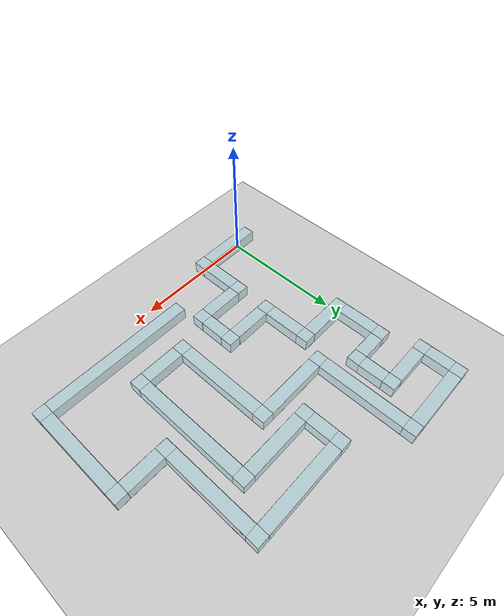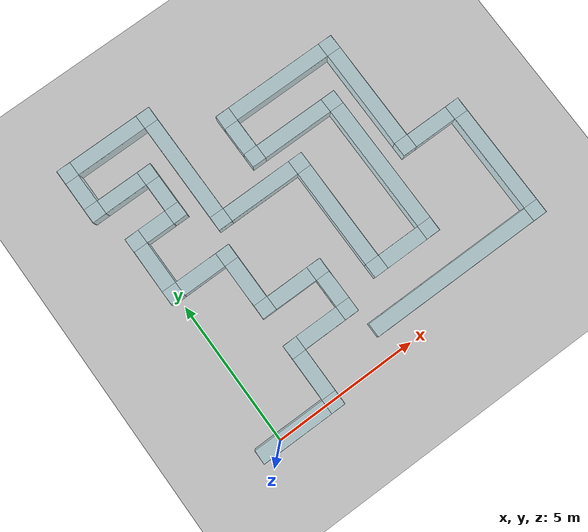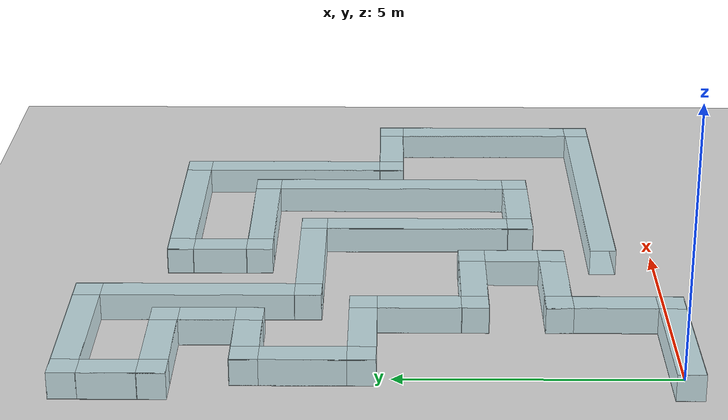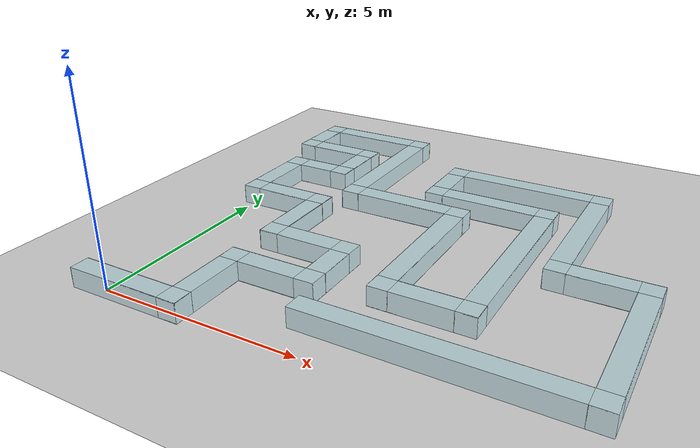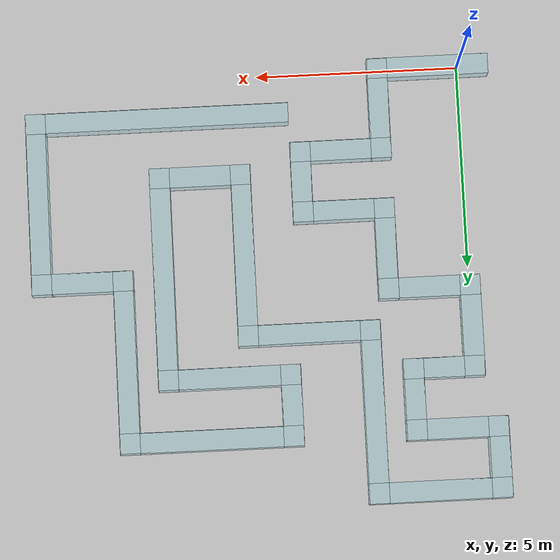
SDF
<sdf version="1.8">
 <world name="demo">
  <plugin filename="gz-sim-physics-system" name="gz::sim::systems::Physics"/>
  <plugin filename="gz-sim-sensors-system" name="gz::sim::systems::Sensors">
   <render_engine>ogre2</render_engine>
  </plugin>
  <plugin filename="gz-sim-scene-broadcaster-system" name="gz::sim::systems::SceneBroadcaster"/>
  <plugin filename="gz-sim-user-commands-system" name="gz::sim::systems::UserCommands"/>
  <light name="sun" type="directional">
   <pose>0 0 10 0 0 0</pose>
   <diffuse>0.8 0.8 0.8 1</diffuse>
   <specular>0.2 0.2 0.2 1</specular>
   <attenuation>
    <range>1000</range>
    <constant>0.9</constant>
    <linear>0.01</linear>
    <quadratic>0.001</quadratic>
   </attenuation>
   <direction>-0.5 0.1 -0.9</direction>
  </light>
  <model name="ground_plane">
   <static>true</static>
   <link name="link">
    <collision name="collision">
     <geometry><plane><normal>0 0 1</normal><size>100 100</size></plane></geometry>
    </collision>
    <visual name="visual">
     <geometry><plane><normal>0 0 1</normal><size>100 100</size></plane></geometry>
     <material>
      <ambient>0.8 0.8 0.8 1</ambient>
      <diffuse>0.8 0.8 0.8 1</diffuse>
      <specular>0.8 0.8 0.8 1</specular>
     </material>
    </visual>
   </link>
  </model>
  <model name="ground_plane">
   <static>true</static>
   <link name="link">
    <collision name="collision">
     <geometry><plane><normal>0 0 1</normal><size>100 100</size></plane></geometry>
    </collision>
    <visual name="visual">
     <geometry><plane><normal>0 0 1</normal><size>100 100</size></plane></geometry>
     <material>
      <ambient>0.6 0.85 0.9 0.4</ambient>
      <diffuse>0.6 0.85 0.9 0.4</diffuse>
      <specular>0.1 0.1 0.1 1</specular>
      <emissive>0 0 0 1</emissive>
     </material>
    </visual>
   </link>
  </model>
  <model name="T1">
   <pose>0.500000 0.000000 0.250000 0.000000 0.000000 0.000000</pose>
   <static>true</static>
   <link name="link">
    <collision name="col_side_posY">
     <pose>0.000000 0.245000 0.000000 0.000000 0.000000 0.000000</pose>
     <geometry><box><size>2.500000 0.010000 0.500000</size></box></geometry>
    </collision>
    <visual name="vis_col_side_posY">
     <pose>0.000000 0.245000 0.000000 0.000000 0.000000 0.000000</pose>
     <geometry><box><size>2.500000 0.010000 0.500000</size></box></geometry>
     <material>
      <ambient>0.6 0.85 0.9 0.4</ambient>
      <diffuse>0.6 0.85 0.9 0.4</diffuse>
      <specular>0.1 0.1 0.1 1</specular>
      <emissive>0 0 0 1</emissive>
     </material>
    </visual>
    <collision name="col_side_negY">
     <pose>0.000000 -0.245000 0.000000 0.000000 0.000000 0.000000</pose>
     <geometry><box><size>2.500000 0.010000 0.500000</size></box></geometry>
    </collision>
    <visual name="vis_col_side_negY">
     <pose>0.000000 -0.245000 0.000000 0.000000 0.000000 0.000000</pose>
     <geometry><box><size>2.500000 0.010000 0.500000</size></box></geometry>
     <material>
      <ambient>0.6 0.85 0.9 0.4</ambient>
      <diffuse>0.6 0.85 0.9 0.4</diffuse>
      <specular>0.1 0.1 0.1 1</specular>
      <emissive>0 0 0 1</emissive>
     </material>
    </visual>
    <collision name="col_top">
     <pose>0.000000 0.000000 0.245000 0.000000 0.000000 0.000000</pose>
     <geometry><box><size>2.500000 0.500000 0.010000</size></box></geometry>
    </collision>
    <visual name="vis_col_top">
     <pose>0.000000 0.000000 0.245000 0.000000 0.000000 0.000000</pose>
     <geometry><box><size>2.500000 0.500000 0.010000</size></box></geometry>
     <material>
      <ambient>0.6 0.85 0.9 0.4</ambient>
      <diffuse>0.6 0.85 0.9 0.4</diffuse>
      <specular>0.1 0.1 0.1 1</specular>
      <emissive>0 0 0 1</emissive>
     </material>
    </visual>
    <collision name="col_bottom">
     <pose>0.000000 0.000000 -0.245000 0.000000 0.000000 0.000000</pose>
     <geometry><box><size>2.500000 0.500000 0.010000</size></box></geometry>
    </collision>
    <visual name="vis_col_bottom">
     <pose>0.000000 0.000000 -0.245000 0.000000 0.000000 0.000000</pose>
     <geometry><box><size>2.500000 0.500000 0.010000</size></box></geometry>
     <material>
      <ambient>0.6 0.85 0.9 0.4</ambient>
      <diffuse>0.6 0.85 0.9 0.4</diffuse>
      <specular>0.1 0.1 0.1 1</specular>
      <emissive>0 0 0 1</emissive>
     </material>
    </visual>
    <collision name="col_end_negX">
     <pose>-1.245000 0.000000 0.000000 0.000000 0.000000 0.000000</pose>
     <geometry><box><size>0.010000 0.500000 0.500000</size></box></geometry>
    </collision>
    <visual name="vis_col_end_negX">
     <pose>-1.245000 0.000000 0.000000 0.000000 0.000000 0.000000</pose>
     <geometry><box><size>0.010000 0.500000 0.500000</size></box></geometry>
     <material>
      <ambient>0.6 0.85 0.9 0.4</ambient>
      <diffuse>0.6 0.85 0.9 0.4</diffuse>
      <specular>0.1 0.1 0.1 1</specular>
      <emissive>0 0 0 1</emissive>
     </material>
    </visual>
   </link>
  </model>
  <model name="T2">
   <pose>2.000000 1.000000 0.250000 0.000000 0.000000 0.000000</pose>
   <static>true</static>
   <link name="link">
    <collision name="col_side_posX">
     <pose>0.245000 0.000000 0.000000 0.000000 0.000000 0.000000</pose>
     <geometry><box><size>0.010000 1.500000 0.500000</size></box></geometry>
    </collision>
    <visual name="vis_col_side_posX">
     <pose>0.245000 0.000000 0.000000 0.000000 0.000000 0.000000</pose>
     <geometry><box><size>0.010000 1.500000 0.500000</size></box></geometry>
     <material>
      <ambient>0.6 0.85 0.9 0.4</ambient>
      <diffuse>0.6 0.85 0.9 0.4</diffuse>
      <specular>0.1 0.1 0.1 1</specular>
      <emissive>0 0 0 1</emissive>
     </material>
    </visual>
    <collision name="col_side_negX">
     <pose>-0.245000 0.000000 0.000000 0.000000 0.000000 0.000000</pose>
     <geometry><box><size>0.010000 1.500000 0.500000</size></box></geometry>
    </collision>
    <visual name="vis_col_side_negX">
     <pose>-0.245000 0.000000 0.000000 0.000000 0.000000 0.000000</pose>
     <geometry><box><size>0.010000 1.500000 0.500000</size></box></geometry>
     <material>
      <ambient>0.6 0.85 0.9 0.4</ambient>
      <diffuse>0.6 0.85 0.9 0.4</diffuse>
      <specular>0.1 0.1 0.1 1</specular>
      <emissive>0 0 0 1</emissive>
     </material>
    </visual>
    <collision name="col_top">
     <pose>0.000000 0.000000 0.245000 0.000000 0.000000 0.000000</pose>
     <geometry><box><size>0.500000 1.500000 0.010000</size></box></geometry>
    </collision>
    <visual name="vis_col_top">
     <pose>0.000000 0.000000 0.245000 0.000000 0.000000 0.000000</pose>
     <geometry><box><size>0.500000 1.500000 0.010000</size></box></geometry>
     <material>
      <ambient>0.6 0.85 0.9 0.4</ambient>
      <diffuse>0.6 0.85 0.9 0.4</diffuse>
      <specular>0.1 0.1 0.1 1</specular>
      <emissive>0 0 0 1</emissive>
     </material>
    </visual>
    <collision name="col_bottom">
     <pose>0.000000 0.000000 -0.245000 0.000000 0.000000 0.000000</pose>
     <geometry><box><size>0.500000 1.500000 0.010000</size></box></geometry>
    </collision>
    <visual name="vis_col_bottom">
     <pose>0.000000 0.000000 -0.245000 0.000000 0.000000 0.000000</pose>
     <geometry><box><size>0.500000 1.500000 0.010000</size></box></geometry>
     <material>
      <ambient>0.6 0.85 0.9 0.4</ambient>
      <diffuse>0.6 0.85 0.9 0.4</diffuse>
      <specular>0.1 0.1 0.1 1</specular>
      <emissive>0 0 0 1</emissive>
     </material>
    </visual>
   </link>
  </model>
  <model name="T3">
   <pose>3.000000 2.000000 0.250000 0.000000 0.000000 0.000000</pose>
   <static>true</static>
   <link name="link">
    <collision name="col_side_posY">
     <pose>0.000000 0.245000 0.000000 0.000000 0.000000 0.000000</pose>
     <geometry><box><size>1.500000 0.010000 0.500000</size></box></geometry>
    </collision>
    <visual name="vis_col_side_posY">
     <pose>0.000000 0.245000 0.000000 0.000000 0.000000 0.000000</pose>
     <geometry><box><size>1.500000 0.010000 0.500000</size></box></geometry>
     <material>
      <ambient>0.6 0.85 0.9 0.4</ambient>
      <diffuse>0.6 0.85 0.9 0.4</diffuse>
      <specular>0.1 0.1 0.1 1</specular>
      <emissive>0 0 0 1</emissive>
     </material>
    </visual>
    <collision name="col_side_negY">
     <pose>0.000000 -0.245000 0.000000 0.000000 0.000000 0.000000</pose>
     <geometry><box><size>1.500000 0.010000 0.500000</size></box></geometry>
    </collision>
    <visual name="vis_col_side_negY">
     <pose>0.000000 -0.245000 0.000000 0.000000 0.000000 0.000000</pose>
     <geometry><box><size>1.500000 0.010000 0.500000</size></box></geometry>
     <material>
      <ambient>0.6 0.85 0.9 0.4</ambient>
      <diffuse>0.6 0.85 0.9 0.4</diffuse>
      <specular>0.1 0.1 0.1 1</specular>
      <emissive>0 0 0 1</emissive>
     </material>
    </visual>
    <collision name="col_top">
     <pose>0.000000 0.000000 0.245000 0.000000 0.000000 0.000000</pose>
     <geometry><box><size>1.500000 0.500000 0.010000</size></box></geometry>
    </collision>
    <visual name="vis_col_top">
     <pose>0.000000 0.000000 0.245000 0.000000 0.000000 0.000000</pose>
     <geometry><box><size>1.500000 0.500000 0.010000</size></box></geometry>
     <material>
      <ambient>0.6 0.85 0.9 0.4</ambient>
      <diffuse>0.6 0.85 0.9 0.4</diffuse>
      <specular>0.1 0.1 0.1 1</specular>
      <emissive>0 0 0 1</emissive>
     </material>
    </visual>
    <collision name="col_bottom">
     <pose>0.000000 0.000000 -0.245000 0.000000 0.000000 0.000000</pose>
     <geometry><box><size>1.500000 0.500000 0.010000</size></box></geometry>
    </collision>
    <visual name="vis_col_bottom">
     <pose>0.000000 0.000000 -0.245000 0.000000 0.000000 0.000000</pose>
     <geometry><box><size>1.500000 0.500000 0.010000</size></box></geometry>
     <material>
      <ambient>0.6 0.85 0.9 0.4</ambient>
      <diffuse>0.6 0.85 0.9 0.4</diffuse>
      <specular>0.1 0.1 0.1 1</specular>
      <emissive>0 0 0 1</emissive>
     </material>
    </visual>
   </link>
  </model>
  <model name="T4">
   <pose>4.000000 2.750000 0.250000 0.000000 0.000000 0.000000</pose>
   <static>true</static>
   <link name="link">
    <collision name="col_side_posX">
     <pose>0.245000 0.000000 0.000000 0.000000 0.000000 0.000000</pose>
     <geometry><box><size>0.010000 1.000000 0.500000</size></box></geometry>
    </collision>
    <visual name="vis_col_side_posX">
     <pose>0.245000 0.000000 0.000000 0.000000 0.000000 0.000000</pose>
     <geometry><box><size>0.010000 1.000000 0.500000</size></box></geometry>
     <material>
      <ambient>0.6 0.85 0.9 0.4</ambient>
      <diffuse>0.6 0.85 0.9 0.4</diffuse>
      <specular>0.1 0.1 0.1 1</specular>
      <emissive>0 0 0 1</emissive>
     </material>
    </visual>
    <collision name="col_side_negX">
     <pose>-0.245000 0.000000 0.000000 0.000000 0.000000 0.000000</pose>
     <geometry><box><size>0.010000 1.000000 0.500000</size></box></geometry>
    </collision>
    <visual name="vis_col_side_negX">
     <pose>-0.245000 0.000000 0.000000 0.000000 0.000000 0.000000</pose>
     <geometry><box><size>0.010000 1.000000 0.500000</size></box></geometry>
     <material>
      <ambient>0.6 0.85 0.9 0.4</ambient>
      <diffuse>0.6 0.85 0.9 0.4</diffuse>
      <specular>0.1 0.1 0.1 1</specular>
      <emissive>0 0 0 1</emissive>
     </material>
    </visual>
    <collision name="col_top">
     <pose>0.000000 0.000000 0.245000 0.000000 0.000000 0.000000</pose>
     <geometry><box><size>0.500000 1.000000 0.010000</size></box></geometry>
    </collision>
    <visual name="vis_col_top">
     <pose>0.000000 0.000000 0.245000 0.000000 0.000000 0.000000</pose>
     <geometry><box><size>0.500000 1.000000 0.010000</size></box></geometry>
     <material>
      <ambient>0.6 0.85 0.9 0.4</ambient>
      <diffuse>0.6 0.85 0.9 0.4</diffuse>
      <specular>0.1 0.1 0.1 1</specular>
      <emissive>0 0 0 1</emissive>
     </material>
    </visual>
    <collision name="col_bottom">
     <pose>0.000000 0.000000 -0.245000 0.000000 0.000000 0.000000</pose>
     <geometry><box><size>0.500000 1.000000 0.010000</size></box></geometry>
    </collision>
    <visual name="vis_col_bottom">
     <pose>0.000000 0.000000 -0.245000 0.000000 0.000000 0.000000</pose>
     <geometry><box><size>0.500000 1.000000 0.010000</size></box></geometry>
     <material>
      <ambient>0.6 0.85 0.9 0.4</ambient>
      <diffuse>0.6 0.85 0.9 0.4</diffuse>
      <specular>0.1 0.1 0.1 1</specular>
      <emissive>0 0 0 1</emissive>
     </material>
    </visual>
   </link>
  </model>
  <model name="T5">
   <pose>3.000000 3.500000 0.250000 0.000000 0.000000 0.000000</pose>
   <static>true</static>
   <link name="link">
    <collision name="col_side_posY">
     <pose>0.000000 0.245000 0.000000 0.000000 0.000000 0.000000</pose>
     <geometry><box><size>1.500000 0.010000 0.500000</size></box></geometry>
    </collision>
    <visual name="vis_col_side_posY">
     <pose>0.000000 0.245000 0.000000 0.000000 0.000000 0.000000</pose>
     <geometry><box><size>1.500000 0.010000 0.500000</size></box></geometry>
     <material>
      <ambient>0.6 0.85 0.9 0.4</ambient>
      <diffuse>0.6 0.85 0.9 0.4</diffuse>
      <specular>0.1 0.1 0.1 1</specular>
      <emissive>0 0 0 1</emissive>
     </material>
    </visual>
    <collision name="col_side_negY">
     <pose>0.000000 -0.245000 0.000000 0.000000 0.000000 0.000000</pose>
     <geometry><box><size>1.500000 0.010000 0.500000</size></box></geometry>
    </collision>
    <visual name="vis_col_side_negY">
     <pose>0.000000 -0.245000 0.000000 0.000000 0.000000 0.000000</pose>
     <geometry><box><size>1.500000 0.010000 0.500000</size></box></geometry>
     <material>
      <ambient>0.6 0.85 0.9 0.4</ambient>
      <diffuse>0.6 0.85 0.9 0.4</diffuse>
      <specular>0.1 0.1 0.1 1</specular>
      <emissive>0 0 0 1</emissive>
     </material>
    </visual>
    <collision name="col_top">
     <pose>0.000000 0.000000 0.245000 0.000000 0.000000 0.000000</pose>
     <geometry><box><size>1.500000 0.500000 0.010000</size></box></geometry>
    </collision>
    <visual name="vis_col_top">
     <pose>0.000000 0.000000 0.245000 0.000000 0.000000 0.000000</pose>
     <geometry><box><size>1.500000 0.500000 0.010000</size></box></geometry>
     <material>
      <ambient>0.6 0.85 0.9 0.4</ambient>
      <diffuse>0.6 0.85 0.9 0.4</diffuse>
      <specular>0.1 0.1 0.1 1</specular>
      <emissive>0 0 0 1</emissive>
     </material>
    </visual>
    <collision name="col_bottom">
     <pose>0.000000 0.000000 -0.245000 0.000000 0.000000 0.000000</pose>
     <geometry><box><size>1.500000 0.500000 0.010000</size></box></geometry>
    </collision>
    <visual name="vis_col_bottom">
     <pose>0.000000 0.000000 -0.245000 0.000000 0.000000 0.000000</pose>
     <geometry><box><size>1.500000 0.500000 0.010000</size></box></geometry>
     <material>
      <ambient>0.6 0.85 0.9 0.4</ambient>
      <diffuse>0.6 0.85 0.9 0.4</diffuse>
      <specular>0.1 0.1 0.1 1</specular>
      <emissive>0 0 0 1</emissive>
     </material>
    </visual>
   </link>
  </model>
  <model name="T6">
   <pose>2.000000 4.500000 0.250000 0.000000 0.000000 0.000000</pose>
   <static>true</static>
   <link name="link">
    <collision name="col_side_posX">
     <pose>0.245000 0.000000 0.000000 0.000000 0.000000 0.000000</pose>
     <geometry><box><size>0.010000 1.500000 0.500000</size></box></geometry>
    </collision>
    <visual name="vis_col_side_posX">
     <pose>0.245000 0.000000 0.000000 0.000000 0.000000 0.000000</pose>
     <geometry><box><size>0.010000 1.500000 0.500000</size></box></geometry>
     <material>
      <ambient>0.6 0.85 0.9 0.4</ambient>
      <diffuse>0.6 0.85 0.9 0.4</diffuse>
      <specular>0.1 0.1 0.1 1</specular>
      <emissive>0 0 0 1</emissive>
     </material>
    </visual>
    <collision name="col_side_negX">
     <pose>-0.245000 0.000000 0.000000 0.000000 0.000000 0.000000</pose>
     <geometry><box><size>0.010000 1.500000 0.500000</size></box></geometry>
    </collision>
    <visual name="vis_col_side_negX">
     <pose>-0.245000 0.000000 0.000000 0.000000 0.000000 0.000000</pose>
     <geometry><box><size>0.010000 1.500000 0.500000</size></box></geometry>
     <material>
      <ambient>0.6 0.85 0.9 0.4</ambient>
      <diffuse>0.6 0.85 0.9 0.4</diffuse>
      <specular>0.1 0.1 0.1 1</specular>
      <emissive>0 0 0 1</emissive>
     </material>
    </visual>
    <collision name="col_top">
     <pose>0.000000 0.000000 0.245000 0.000000 0.000000 0.000000</pose>
     <geometry><box><size>0.500000 1.500000 0.010000</size></box></geometry>
    </collision>
    <visual name="vis_col_top">
     <pose>0.000000 0.000000 0.245000 0.000000 0.000000 0.000000</pose>
     <geometry><box><size>0.500000 1.500000 0.010000</size></box></geometry>
     <material>
      <ambient>0.6 0.85 0.9 0.4</ambient>
      <diffuse>0.6 0.85 0.9 0.4</diffuse>
      <specular>0.1 0.1 0.1 1</specular>
      <emissive>0 0 0 1</emissive>
     </material>
    </visual>
    <collision name="col_bottom">
     <pose>0.000000 0.000000 -0.245000 0.000000 0.000000 0.000000</pose>
     <geometry><box><size>0.500000 1.500000 0.010000</size></box></geometry>
    </collision>
    <visual name="vis_col_bottom">
     <pose>0.000000 0.000000 -0.245000 0.000000 0.000000 0.000000</pose>
     <geometry><box><size>0.500000 1.500000 0.010000</size></box></geometry>
     <material>
      <ambient>0.6 0.85 0.9 0.4</ambient>
      <diffuse>0.6 0.85 0.9 0.4</diffuse>
      <specular>0.1 0.1 0.1 1</specular>
      <emissive>0 0 0 1</emissive>
     </material>
    </visual>
   </link>
  </model>
  <model name="T7">
   <pose>1.000000 5.500000 0.250000 0.000000 0.000000 0.000000</pose>
   <static>true</static>
   <link name="link">
    <collision name="col_side_posY">
     <pose>0.000000 0.245000 0.000000 0.000000 0.000000 0.000000</pose>
     <geometry><box><size>1.500000 0.010000 0.500000</size></box></geometry>
    </collision>
    <visual name="vis_col_side_posY">
     <pose>0.000000 0.245000 0.000000 0.000000 0.000000 0.000000</pose>
     <geometry><box><size>1.500000 0.010000 0.500000</size></box></geometry>
     <material>
      <ambient>0.6 0.85 0.9 0.4</ambient>
      <diffuse>0.6 0.85 0.9 0.4</diffuse>
      <specular>0.1 0.1 0.1 1</specular>
      <emissive>0 0 0 1</emissive>
     </material>
    </visual>
    <collision name="col_side_negY">
     <pose>0.000000 -0.245000 0.000000 0.000000 0.000000 0.000000</pose>
     <geometry><box><size>1.500000 0.010000 0.500000</size></box></geometry>
    </collision>
    <visual name="vis_col_side_negY">
     <pose>0.000000 -0.245000 0.000000 0.000000 0.000000 0.000000</pose>
     <geometry><box><size>1.500000 0.010000 0.500000</size></box></geometry>
     <material>
      <ambient>0.6 0.85 0.9 0.4</ambient>
      <diffuse>0.6 0.85 0.9 0.4</diffuse>
      <specular>0.1 0.1 0.1 1</specular>
      <emissive>0 0 0 1</emissive>
     </material>
    </visual>
    <collision name="col_top">
     <pose>0.000000 0.000000 0.245000 0.000000 0.000000 0.000000</pose>
     <geometry><box><size>1.500000 0.500000 0.010000</size></box></geometry>
    </collision>
    <visual name="vis_col_top">
     <pose>0.000000 0.000000 0.245000 0.000000 0.000000 0.000000</pose>
     <geometry><box><size>1.500000 0.500000 0.010000</size></box></geometry>
     <material>
      <ambient>0.6 0.85 0.9 0.4</ambient>
      <diffuse>0.6 0.85 0.9 0.4</diffuse>
      <specular>0.1 0.1 0.1 1</specular>
      <emissive>0 0 0 1</emissive>
     </material>
    </visual>
    <collision name="col_bottom">
     <pose>0.000000 0.000000 -0.245000 0.000000 0.000000 0.000000</pose>
     <geometry><box><size>1.500000 0.500000 0.010000</size></box></geometry>
    </collision>
    <visual name="vis_col_bottom">
     <pose>0.000000 0.000000 -0.245000 0.000000 0.000000 0.000000</pose>
     <geometry><box><size>1.500000 0.500000 0.010000</size></box></geometry>
     <material>
      <ambient>0.6 0.85 0.9 0.4</ambient>
      <diffuse>0.6 0.85 0.9 0.4</diffuse>
      <specular>0.1 0.1 0.1 1</specular>
      <emissive>0 0 0 1</emissive>
     </material>
    </visual>
   </link>
  </model>
  <model name="T8">
   <pose>0.000000 6.500000 0.250000 0.000000 0.000000 0.000000</pose>
   <static>true</static>
   <link name="link">
    <collision name="col_side_posX">
     <pose>0.245000 0.000000 0.000000 0.000000 0.000000 0.000000</pose>
     <geometry><box><size>0.010000 1.500000 0.500000</size></box></geometry>
    </collision>
    <visual name="vis_col_side_posX">
     <pose>0.245000 0.000000 0.000000 0.000000 0.000000 0.000000</pose>
     <geometry><box><size>0.010000 1.500000 0.500000</size></box></geometry>
     <material>
      <ambient>0.6 0.85 0.9 0.4</ambient>
      <diffuse>0.6 0.85 0.9 0.4</diffuse>
      <specular>0.1 0.1 0.1 1</specular>
      <emissive>0 0 0 1</emissive>
     </material>
    </visual>
    <collision name="col_side_negX">
     <pose>-0.245000 0.000000 0.000000 0.000000 0.000000 0.000000</pose>
     <geometry><box><size>0.010000 1.500000 0.500000</size></box></geometry>
    </collision>
    <visual name="vis_col_side_negX">
     <pose>-0.245000 0.000000 0.000000 0.000000 0.000000 0.000000</pose>
     <geometry><box><size>0.010000 1.500000 0.500000</size></box></geometry>
     <material>
      <ambient>0.6 0.85 0.9 0.4</ambient>
      <diffuse>0.6 0.85 0.9 0.4</diffuse>
      <specular>0.1 0.1 0.1 1</specular>
      <emissive>0 0 0 1</emissive>
     </material>
    </visual>
    <collision name="col_top">
     <pose>0.000000 0.000000 0.245000 0.000000 0.000000 0.000000</pose>
     <geometry><box><size>0.500000 1.500000 0.010000</size></box></geometry>
    </collision>
    <visual name="vis_col_top">
     <pose>0.000000 0.000000 0.245000 0.000000 0.000000 0.000000</pose>
     <geometry><box><size>0.500000 1.500000 0.010000</size></box></geometry>
     <material>
      <ambient>0.6 0.85 0.9 0.4</ambient>
      <diffuse>0.6 0.85 0.9 0.4</diffuse>
      <specular>0.1 0.1 0.1 1</specular>
      <emissive>0 0 0 1</emissive>
     </material>
    </visual>
    <collision name="col_bottom">
     <pose>0.000000 0.000000 -0.245000 0.000000 0.000000 0.000000</pose>
     <geometry><box><size>0.500000 1.500000 0.010000</size></box></geometry>
    </collision>
    <visual name="vis_col_bottom">
     <pose>0.000000 0.000000 -0.245000 0.000000 0.000000 0.000000</pose>
     <geometry><box><size>0.500000 1.500000 0.010000</size></box></geometry>
     <material>
      <ambient>0.6 0.85 0.9 0.4</ambient>
      <diffuse>0.6 0.85 0.9 0.4</diffuse>
      <specular>0.1 0.1 0.1 1</specular>
      <emissive>0 0 0 1</emissive>
     </material>
    </visual>
   </link>
  </model>
  <model name="T9">
   <pose>0.750000 7.500000 0.250000 0.000000 0.000000 0.000000</pose>
   <static>true</static>
   <link name="link">
    <collision name="col_side_posY">
     <pose>0.000000 0.245000 0.000000 0.000000 0.000000 0.000000</pose>
     <geometry><box><size>1.000000 0.010000 0.500000</size></box></geometry>
    </collision>
    <visual name="vis_col_side_posY">
     <pose>0.000000 0.245000 0.000000 0.000000 0.000000 0.000000</pose>
     <geometry><box><size>1.000000 0.010000 0.500000</size></box></geometry>
     <material>
      <ambient>0.6 0.85 0.9 0.4</ambient>
      <diffuse>0.6 0.85 0.9 0.4</diffuse>
      <specular>0.1 0.1 0.1 1</specular>
      <emissive>0 0 0 1</emissive>
     </material>
    </visual>
    <collision name="col_side_negY">
     <pose>0.000000 -0.245000 0.000000 0.000000 0.000000 0.000000</pose>
     <geometry><box><size>1.000000 0.010000 0.500000</size></box></geometry>
    </collision>
    <visual name="vis_col_side_negY">
     <pose>0.000000 -0.245000 0.000000 0.000000 0.000000 0.000000</pose>
     <geometry><box><size>1.000000 0.010000 0.500000</size></box></geometry>
     <material>
      <ambient>0.6 0.85 0.9 0.4</ambient>
      <diffuse>0.6 0.85 0.9 0.4</diffuse>
      <specular>0.1 0.1 0.1 1</specular>
      <emissive>0 0 0 1</emissive>
     </material>
    </visual>
    <collision name="col_top">
     <pose>0.000000 0.000000 0.245000 0.000000 0.000000 0.000000</pose>
     <geometry><box><size>1.000000 0.500000 0.010000</size></box></geometry>
    </collision>
    <visual name="vis_col_top">
     <pose>0.000000 0.000000 0.245000 0.000000 0.000000 0.000000</pose>
     <geometry><box><size>1.000000 0.500000 0.010000</size></box></geometry>
     <material>
      <ambient>0.6 0.85 0.9 0.4</ambient>
      <diffuse>0.6 0.85 0.9 0.4</diffuse>
      <specular>0.1 0.1 0.1 1</specular>
      <emissive>0 0 0 1</emissive>
     </material>
    </visual>
    <collision name="col_bottom">
     <pose>0.000000 0.000000 -0.245000 0.000000 0.000000 0.000000</pose>
     <geometry><box><size>1.000000 0.500000 0.010000</size></box></geometry>
    </collision>
    <visual name="vis_col_bottom">
     <pose>0.000000 0.000000 -0.245000 0.000000 0.000000 0.000000</pose>
     <geometry><box><size>1.000000 0.500000 0.010000</size></box></geometry>
     <material>
      <ambient>0.6 0.85 0.9 0.4</ambient>
      <diffuse>0.6 0.85 0.9 0.4</diffuse>
      <specular>0.1 0.1 0.1 1</specular>
      <emissive>0 0 0 1</emissive>
     </material>
    </visual>
   </link>
  </model>
  <model name="T10">
   <pose>1.500000 8.250000 0.250000 0.000000 0.000000 0.000000</pose>
   <static>true</static>
   <link name="link">
    <collision name="col_side_posX">
     <pose>0.245000 0.000000 0.000000 0.000000 0.000000 0.000000</pose>
     <geometry><box><size>0.010000 1.000000 0.500000</size></box></geometry>
    </collision>
    <visual name="vis_col_side_posX">
     <pose>0.245000 0.000000 0.000000 0.000000 0.000000 0.000000</pose>
     <geometry><box><size>0.010000 1.000000 0.500000</size></box></geometry>
     <material>
      <ambient>0.6 0.85 0.9 0.4</ambient>
      <diffuse>0.6 0.85 0.9 0.4</diffuse>
      <specular>0.1 0.1 0.1 1</specular>
      <emissive>0 0 0 1</emissive>
     </material>
    </visual>
    <collision name="col_side_negX">
     <pose>-0.245000 0.000000 0.000000 0.000000 0.000000 0.000000</pose>
     <geometry><box><size>0.010000 1.000000 0.500000</size></box></geometry>
    </collision>
    <visual name="vis_col_side_negX">
     <pose>-0.245000 0.000000 0.000000 0.000000 0.000000 0.000000</pose>
     <geometry><box><size>0.010000 1.000000 0.500000</size></box></geometry>
     <material>
      <ambient>0.6 0.85 0.9 0.4</ambient>
      <diffuse>0.6 0.85 0.9 0.4</diffuse>
      <specular>0.1 0.1 0.1 1</specular>
      <emissive>0 0 0 1</emissive>
     </material>
    </visual>
    <collision name="col_top">
     <pose>0.000000 0.000000 0.245000 0.000000 0.000000 0.000000</pose>
     <geometry><box><size>0.500000 1.000000 0.010000</size></box></geometry>
    </collision>
    <visual name="vis_col_top">
     <pose>0.000000 0.000000 0.245000 0.000000 0.000000 0.000000</pose>
     <geometry><box><size>0.500000 1.000000 0.010000</size></box></geometry>
     <material>
      <ambient>0.6 0.85 0.9 0.4</ambient>
      <diffuse>0.6 0.85 0.9 0.4</diffuse>
      <specular>0.1 0.1 0.1 1</specular>
      <emissive>0 0 0 1</emissive>
     </material>
    </visual>
    <collision name="col_bottom">
     <pose>0.000000 0.000000 -0.245000 0.000000 0.000000 0.000000</pose>
     <geometry><box><size>0.500000 1.000000 0.010000</size></box></geometry>
    </collision>
    <visual name="vis_col_bottom">
     <pose>0.000000 0.000000 -0.245000 0.000000 0.000000 0.000000</pose>
     <geometry><box><size>0.500000 1.000000 0.010000</size></box></geometry>
     <material>
      <ambient>0.6 0.85 0.9 0.4</ambient>
      <diffuse>0.6 0.85 0.9 0.4</diffuse>
      <specular>0.1 0.1 0.1 1</specular>
      <emissive>0 0 0 1</emissive>
     </material>
    </visual>
   </link>
  </model>
  <model name="T11">
   <pose>0.500000 9.000000 0.250000 0.000000 0.000000 0.000000</pose>
   <static>true</static>
   <link name="link">
    <collision name="col_side_posY">
     <pose>0.000000 0.245000 0.000000 0.000000 0.000000 0.000000</pose>
     <geometry><box><size>1.500000 0.010000 0.500000</size></box></geometry>
    </collision>
    <visual name="vis_col_side_posY">
     <pose>0.000000 0.245000 0.000000 0.000000 0.000000 0.000000</pose>
     <geometry><box><size>1.500000 0.010000 0.500000</size></box></geometry>
     <material>
      <ambient>0.6 0.85 0.9 0.4</ambient>
      <diffuse>0.6 0.85 0.9 0.4</diffuse>
      <specular>0.1 0.1 0.1 1</specular>
      <emissive>0 0 0 1</emissive>
     </material>
    </visual>
    <collision name="col_side_negY">
     <pose>0.000000 -0.245000 0.000000 0.000000 0.000000 0.000000</pose>
     <geometry><box><size>1.500000 0.010000 0.500000</size></box></geometry>
    </collision>
    <visual name="vis_col_side_negY">
     <pose>0.000000 -0.245000 0.000000 0.000000 0.000000 0.000000</pose>
     <geometry><box><size>1.500000 0.010000 0.500000</size></box></geometry>
     <material>
      <ambient>0.6 0.85 0.9 0.4</ambient>
      <diffuse>0.6 0.85 0.9 0.4</diffuse>
      <specular>0.1 0.1 0.1 1</specular>
      <emissive>0 0 0 1</emissive>
     </material>
    </visual>
    <collision name="col_top">
     <pose>0.000000 0.000000 0.245000 0.000000 0.000000 0.000000</pose>
     <geometry><box><size>1.500000 0.500000 0.010000</size></box></geometry>
    </collision>
    <visual name="vis_col_top">
     <pose>0.000000 0.000000 0.245000 0.000000 0.000000 0.000000</pose>
     <geometry><box><size>1.500000 0.500000 0.010000</size></box></geometry>
     <material>
      <ambient>0.6 0.85 0.9 0.4</ambient>
      <diffuse>0.6 0.85 0.9 0.4</diffuse>
      <specular>0.1 0.1 0.1 1</specular>
      <emissive>0 0 0 1</emissive>
     </material>
    </visual>
    <collision name="col_bottom">
     <pose>0.000000 0.000000 -0.245000 0.000000 0.000000 0.000000</pose>
     <geometry><box><size>1.500000 0.500000 0.010000</size></box></geometry>
    </collision>
    <visual name="vis_col_bottom">
     <pose>0.000000 0.000000 -0.245000 0.000000 0.000000 0.000000</pose>
     <geometry><box><size>1.500000 0.500000 0.010000</size></box></geometry>
     <material>
      <ambient>0.6 0.85 0.9 0.4</ambient>
      <diffuse>0.6 0.85 0.9 0.4</diffuse>
      <specular>0.1 0.1 0.1 1</specular>
      <emissive>0 0 0 1</emissive>
     </material>
    </visual>
   </link>
  </model>
  <model name="T12">
   <pose>-0.500000 9.750000 0.250000 0.000000 0.000000 0.000000</pose>
   <static>true</static>
   <link name="link">
    <collision name="col_side_posX">
     <pose>0.245000 0.000000 0.000000 0.000000 0.000000 0.000000</pose>
     <geometry><box><size>0.010000 1.000000 0.500000</size></box></geometry>
    </collision>
    <visual name="vis_col_side_posX">
     <pose>0.245000 0.000000 0.000000 0.000000 0.000000 0.000000</pose>
     <geometry><box><size>0.010000 1.000000 0.500000</size></box></geometry>
     <material>
      <ambient>0.6 0.85 0.9 0.4</ambient>
      <diffuse>0.6 0.85 0.9 0.4</diffuse>
      <specular>0.1 0.1 0.1 1</specular>
      <emissive>0 0 0 1</emissive>
     </material>
    </visual>
    <collision name="col_side_negX">
     <pose>-0.245000 0.000000 0.000000 0.000000 0.000000 0.000000</pose>
     <geometry><box><size>0.010000 1.000000 0.500000</size></box></geometry>
    </collision>
    <visual name="vis_col_side_negX">
     <pose>-0.245000 0.000000 0.000000 0.000000 0.000000 0.000000</pose>
     <geometry><box><size>0.010000 1.000000 0.500000</size></box></geometry>
     <material>
      <ambient>0.6 0.85 0.9 0.4</ambient>
      <diffuse>0.6 0.85 0.9 0.4</diffuse>
      <specular>0.1 0.1 0.1 1</specular>
      <emissive>0 0 0 1</emissive>
     </material>
    </visual>
    <collision name="col_top">
     <pose>0.000000 0.000000 0.245000 0.000000 0.000000 0.000000</pose>
     <geometry><box><size>0.500000 1.000000 0.010000</size></box></geometry>
    </collision>
    <visual name="vis_col_top">
     <pose>0.000000 0.000000 0.245000 0.000000 0.000000 0.000000</pose>
     <geometry><box><size>0.500000 1.000000 0.010000</size></box></geometry>
     <material>
      <ambient>0.6 0.85 0.9 0.4</ambient>
      <diffuse>0.6 0.85 0.9 0.4</diffuse>
      <specular>0.1 0.1 0.1 1</specular>
      <emissive>0 0 0 1</emissive>
     </material>
    </visual>
    <collision name="col_bottom">
     <pose>0.000000 0.000000 -0.245000 0.000000 0.000000 0.000000</pose>
     <geometry><box><size>0.500000 1.000000 0.010000</size></box></geometry>
    </collision>
    <visual name="vis_col_bottom">
     <pose>0.000000 0.000000 -0.245000 0.000000 0.000000 0.000000</pose>
     <geometry><box><size>0.500000 1.000000 0.010000</size></box></geometry>
     <material>
      <ambient>0.6 0.85 0.9 0.4</ambient>
      <diffuse>0.6 0.85 0.9 0.4</diffuse>
      <specular>0.1 0.1 0.1 1</specular>
      <emissive>0 0 0 1</emissive>
     </material>
    </visual>
   </link>
  </model>
  <model name="T13">
   <pose>1.000000 10.500000 0.250000 0.000000 0.000000 0.000000</pose>
   <static>true</static>
   <link name="link">
    <collision name="col_side_posY">
     <pose>0.000000 0.245000 0.000000 0.000000 0.000000 0.000000</pose>
     <geometry><box><size>2.500000 0.010000 0.500000</size></box></geometry>
    </collision>
    <visual name="vis_col_side_posY">
     <pose>0.000000 0.245000 0.000000 0.000000 0.000000 0.000000</pose>
     <geometry><box><size>2.500000 0.010000 0.500000</size></box></geometry>
     <material>
      <ambient>0.6 0.85 0.9 0.4</ambient>
      <diffuse>0.6 0.85 0.9 0.4</diffuse>
      <specular>0.1 0.1 0.1 1</specular>
      <emissive>0 0 0 1</emissive>
     </material>
    </visual>
    <collision name="col_side_negY">
     <pose>0.000000 -0.245000 0.000000 0.000000 0.000000 0.000000</pose>
     <geometry><box><size>2.500000 0.010000 0.500000</size></box></geometry>
    </collision>
    <visual name="vis_col_side_negY">
     <pose>0.000000 -0.245000 0.000000 0.000000 0.000000 0.000000</pose>
     <geometry><box><size>2.500000 0.010000 0.500000</size></box></geometry>
     <material>
      <ambient>0.6 0.85 0.9 0.4</ambient>
      <diffuse>0.6 0.85 0.9 0.4</diffuse>
      <specular>0.1 0.1 0.1 1</specular>
      <emissive>0 0 0 1</emissive>
     </material>
    </visual>
    <collision name="col_top">
     <pose>0.000000 0.000000 0.245000 0.000000 0.000000 0.000000</pose>
     <geometry><box><size>2.500000 0.500000 0.010000</size></box></geometry>
    </collision>
    <visual name="vis_col_top">
     <pose>0.000000 0.000000 0.245000 0.000000 0.000000 0.000000</pose>
     <geometry><box><size>2.500000 0.500000 0.010000</size></box></geometry>
     <material>
      <ambient>0.6 0.85 0.9 0.4</ambient>
      <diffuse>0.6 0.85 0.9 0.4</diffuse>
      <specular>0.1 0.1 0.1 1</specular>
      <emissive>0 0 0 1</emissive>
     </material>
    </visual>
    <collision name="col_bottom">
     <pose>0.000000 0.000000 -0.245000 0.000000 0.000000 0.000000</pose>
     <geometry><box><size>2.500000 0.500000 0.010000</size></box></geometry>
    </collision>
    <visual name="vis_col_bottom">
     <pose>0.000000 0.000000 -0.245000 0.000000 0.000000 0.000000</pose>
     <geometry><box><size>2.500000 0.500000 0.010000</size></box></geometry>
     <material>
      <ambient>0.6 0.85 0.9 0.4</ambient>
      <diffuse>0.6 0.85 0.9 0.4</diffuse>
      <specular>0.1 0.1 0.1 1</specular>
      <emissive>0 0 0 1</emissive>
     </material>
    </visual>
   </link>
  </model>
  <model name="T14">
   <pose>2.500000 8.500000 0.250000 0.000000 0.000000 0.000000</pose>
   <static>true</static>
   <link name="link">
    <collision name="col_side_posX">
     <pose>0.245000 0.000000 0.000000 0.000000 0.000000 0.000000</pose>
     <geometry><box><size>0.010000 3.500000 0.500000</size></box></geometry>
    </collision>
    <visual name="vis_col_side_posX">
     <pose>0.245000 0.000000 0.000000 0.000000 0.000000 0.000000</pose>
     <geometry><box><size>0.010000 3.500000 0.500000</size></box></geometry>
     <material>
      <ambient>0.6 0.85 0.9 0.4</ambient>
      <diffuse>0.6 0.85 0.9 0.4</diffuse>
      <specular>0.1 0.1 0.1 1</specular>
      <emissive>0 0 0 1</emissive>
     </material>
    </visual>
    <collision name="col_side_negX">
     <pose>-0.245000 0.000000 0.000000 0.000000 0.000000 0.000000</pose>
     <geometry><box><size>0.010000 3.500000 0.500000</size></box></geometry>
    </collision>
    <visual name="vis_col_side_negX">
     <pose>-0.245000 0.000000 0.000000 0.000000 0.000000 0.000000</pose>
     <geometry><box><size>0.010000 3.500000 0.500000</size></box></geometry>
     <material>
      <ambient>0.6 0.85 0.9 0.4</ambient>
      <diffuse>0.6 0.85 0.9 0.4</diffuse>
      <specular>0.1 0.1 0.1 1</specular>
      <emissive>0 0 0 1</emissive>
     </material>
    </visual>
    <collision name="col_top">
     <pose>0.000000 0.000000 0.245000 0.000000 0.000000 0.000000</pose>
     <geometry><box><size>0.500000 3.500000 0.010000</size></box></geometry>
    </collision>
    <visual name="vis_col_top">
     <pose>0.000000 0.000000 0.245000 0.000000 0.000000 0.000000</pose>
     <geometry><box><size>0.500000 3.500000 0.010000</size></box></geometry>
     <material>
      <ambient>0.6 0.85 0.9 0.4</ambient>
      <diffuse>0.6 0.85 0.9 0.4</diffuse>
      <specular>0.1 0.1 0.1 1</specular>
      <emissive>0 0 0 1</emissive>
     </material>
    </visual>
    <collision name="col_bottom">
     <pose>0.000000 0.000000 -0.245000 0.000000 0.000000 0.000000</pose>
     <geometry><box><size>0.500000 3.500000 0.010000</size></box></geometry>
    </collision>
    <visual name="vis_col_bottom">
     <pose>0.000000 0.000000 -0.245000 0.000000 0.000000 0.000000</pose>
     <geometry><box><size>0.500000 3.500000 0.010000</size></box></geometry>
     <material>
      <ambient>0.6 0.85 0.9 0.4</ambient>
      <diffuse>0.6 0.85 0.9 0.4</diffuse>
      <specular>0.1 0.1 0.1 1</specular>
      <emissive>0 0 0 1</emissive>
     </material>
    </visual>
   </link>
  </model>
  <model name="T15">
   <pose>4.000000 6.500000 0.250000 0.000000 0.000000 0.000000</pose>
   <static>true</static>
   <link name="link">
    <collision name="col_side_posY">
     <pose>0.000000 0.245000 0.000000 0.000000 0.000000 0.000000</pose>
     <geometry><box><size>2.500000 0.010000 0.500000</size></box></geometry>
    </collision>
    <visual name="vis_col_side_posY">
     <pose>0.000000 0.245000 0.000000 0.000000 0.000000 0.000000</pose>
     <geometry><box><size>2.500000 0.010000 0.500000</size></box></geometry>
     <material>
      <ambient>0.6 0.85 0.9 0.4</ambient>
      <diffuse>0.6 0.85 0.9 0.4</diffuse>
      <specular>0.1 0.1 0.1 1</specular>
      <emissive>0 0 0 1</emissive>
     </material>
    </visual>
    <collision name="col_side_negY">
     <pose>0.000000 -0.245000 0.000000 0.000000 0.000000 0.000000</pose>
     <geometry><box><size>2.500000 0.010000 0.500000</size></box></geometry>
    </collision>
    <visual name="vis_col_side_negY">
     <pose>0.000000 -0.245000 0.000000 0.000000 0.000000 0.000000</pose>
     <geometry><box><size>2.500000 0.010000 0.500000</size></box></geometry>
     <material>
      <ambient>0.6 0.85 0.9 0.4</ambient>
      <diffuse>0.6 0.85 0.9 0.4</diffuse>
      <specular>0.1 0.1 0.1 1</specular>
      <emissive>0 0 0 1</emissive>
     </material>
    </visual>
    <collision name="col_top">
     <pose>0.000000 0.000000 0.245000 0.000000 0.000000 0.000000</pose>
     <geometry><box><size>2.500000 0.500000 0.010000</size></box></geometry>
    </collision>
    <visual name="vis_col_top">
     <pose>0.000000 0.000000 0.245000 0.000000 0.000000 0.000000</pose>
     <geometry><box><size>2.500000 0.500000 0.010000</size></box></geometry>
     <material>
      <ambient>0.6 0.85 0.9 0.4</ambient>
      <diffuse>0.6 0.85 0.9 0.4</diffuse>
      <specular>0.1 0.1 0.1 1</specular>
      <emissive>0 0 0 1</emissive>
     </material>
    </visual>
    <collision name="col_bottom">
     <pose>0.000000 0.000000 -0.245000 0.000000 0.000000 0.000000</pose>
     <geometry><box><size>2.500000 0.500000 0.010000</size></box></geometry>
    </collision>
    <visual name="vis_col_bottom">
     <pose>0.000000 0.000000 -0.245000 0.000000 0.000000 0.000000</pose>
     <geometry><box><size>2.500000 0.500000 0.010000</size></box></geometry>
     <material>
      <ambient>0.6 0.85 0.9 0.4</ambient>
      <diffuse>0.6 0.85 0.9 0.4</diffuse>
      <specular>0.1 0.1 0.1 1</specular>
      <emissive>0 0 0 1</emissive>
     </material>
    </visual>
   </link>
  </model>
  <model name="T16">
   <pose>5.500000 4.500000 0.250000 0.000000 0.000000 0.000000</pose>
   <static>true</static>
   <link name="link">
    <collision name="col_side_posX">
     <pose>0.245000 0.000000 0.000000 0.000000 0.000000 0.000000</pose>
     <geometry><box><size>0.010000 3.500000 0.500000</size></box></geometry>
    </collision>
    <visual name="vis_col_side_posX">
     <pose>0.245000 0.000000 0.000000 0.000000 0.000000 0.000000</pose>
     <geometry><box><size>0.010000 3.500000 0.500000</size></box></geometry>
     <material>
      <ambient>0.6 0.85 0.9 0.4</ambient>
      <diffuse>0.6 0.85 0.9 0.4</diffuse>
      <specular>0.1 0.1 0.1 1</specular>
      <emissive>0 0 0 1</emissive>
     </material>
    </visual>
    <collision name="col_side_negX">
     <pose>-0.245000 0.000000 0.000000 0.000000 0.000000 0.000000</pose>
     <geometry><box><size>0.010000 3.500000 0.500000</size></box></geometry>
    </collision>
    <visual name="vis_col_side_negX">
     <pose>-0.245000 0.000000 0.000000 0.000000 0.000000 0.000000</pose>
     <geometry><box><size>0.010000 3.500000 0.500000</size></box></geometry>
     <material>
      <ambient>0.6 0.85 0.9 0.4</ambient>
      <diffuse>0.6 0.85 0.9 0.4</diffuse>
      <specular>0.1 0.1 0.1 1</specular>
      <emissive>0 0 0 1</emissive>
     </material>
    </visual>
    <collision name="col_top">
     <pose>0.000000 0.000000 0.245000 0.000000 0.000000 0.000000</pose>
     <geometry><box><size>0.500000 3.500000 0.010000</size></box></geometry>
    </collision>
    <visual name="vis_col_top">
     <pose>0.000000 0.000000 0.245000 0.000000 0.000000 0.000000</pose>
     <geometry><box><size>0.500000 3.500000 0.010000</size></box></geometry>
     <material>
      <ambient>0.6 0.85 0.9 0.4</ambient>
      <diffuse>0.6 0.85 0.9 0.4</diffuse>
      <specular>0.1 0.1 0.1 1</specular>
      <emissive>0 0 0 1</emissive>
     </material>
    </visual>
    <collision name="col_bottom">
     <pose>0.000000 0.000000 -0.245000 0.000000 0.000000 0.000000</pose>
     <geometry><box><size>0.500000 3.500000 0.010000</size></box></geometry>
    </collision>
    <visual name="vis_col_bottom">
     <pose>0.000000 0.000000 -0.245000 0.000000 0.000000 0.000000</pose>
     <geometry><box><size>0.500000 3.500000 0.010000</size></box></geometry>
     <material>
      <ambient>0.6 0.85 0.9 0.4</ambient>
      <diffuse>0.6 0.85 0.9 0.4</diffuse>
      <specular>0.1 0.1 0.1 1</specular>
      <emissive>0 0 0 1</emissive>
     </material>
    </visual>
   </link>
  </model>
  <model name="T17">
   <pose>6.500000 2.500000 0.250000 0.000000 0.000000 0.000000</pose>
   <static>true</static>
   <link name="link">
    <collision name="col_side_posY">
     <pose>0.000000 0.245000 0.000000 0.000000 0.000000 0.000000</pose>
     <geometry><box><size>1.500000 0.010000 0.500000</size></box></geometry>
    </collision>
    <visual name="vis_col_side_posY">
     <pose>0.000000 0.245000 0.000000 0.000000 0.000000 0.000000</pose>
     <geometry><box><size>1.500000 0.010000 0.500000</size></box></geometry>
     <material>
      <ambient>0.6 0.85 0.9 0.4</ambient>
      <diffuse>0.6 0.85 0.9 0.4</diffuse>
      <specular>0.1 0.1 0.1 1</specular>
      <emissive>0 0 0 1</emissive>
     </material>
    </visual>
    <collision name="col_side_negY">
     <pose>0.000000 -0.245000 0.000000 0.000000 0.000000 0.000000</pose>
     <geometry><box><size>1.500000 0.010000 0.500000</size></box></geometry>
    </collision>
    <visual name="vis_col_side_negY">
     <pose>0.000000 -0.245000 0.000000 0.000000 0.000000 0.000000</pose>
     <geometry><box><size>1.500000 0.010000 0.500000</size></box></geometry>
     <material>
      <ambient>0.6 0.85 0.9 0.4</ambient>
      <diffuse>0.6 0.85 0.9 0.4</diffuse>
      <specular>0.1 0.1 0.1 1</specular>
      <emissive>0 0 0 1</emissive>
     </material>
    </visual>
    <collision name="col_top">
     <pose>0.000000 0.000000 0.245000 0.000000 0.000000 0.000000</pose>
     <geometry><box><size>1.500000 0.500000 0.010000</size></box></geometry>
    </collision>
    <visual name="vis_col_top">
     <pose>0.000000 0.000000 0.245000 0.000000 0.000000 0.000000</pose>
     <geometry><box><size>1.500000 0.500000 0.010000</size></box></geometry>
     <material>
      <ambient>0.6 0.85 0.9 0.4</ambient>
      <diffuse>0.6 0.85 0.9 0.4</diffuse>
      <specular>0.1 0.1 0.1 1</specular>
      <emissive>0 0 0 1</emissive>
     </material>
    </visual>
    <collision name="col_bottom">
     <pose>0.000000 0.000000 -0.245000 0.000000 0.000000 0.000000</pose>
     <geometry><box><size>1.500000 0.500000 0.010000</size></box></geometry>
    </collision>
    <visual name="vis_col_bottom">
     <pose>0.000000 0.000000 -0.245000 0.000000 0.000000 0.000000</pose>
     <geometry><box><size>1.500000 0.500000 0.010000</size></box></geometry>
     <material>
      <ambient>0.6 0.85 0.9 0.4</ambient>
      <diffuse>0.6 0.85 0.9 0.4</diffuse>
      <specular>0.1 0.1 0.1 1</specular>
      <emissive>0 0 0 1</emissive>
     </material>
    </visual>
   </link>
  </model>
  <model name="T18">
   <pose>7.500000 5.000000 0.250000 0.000000 0.000000 0.000000</pose>
   <static>true</static>
   <link name="link">
    <collision name="col_side_posX">
     <pose>0.245000 0.000000 0.000000 0.000000 0.000000 0.000000</pose>
     <geometry><box><size>0.010000 4.500000 0.500000</size></box></geometry>
    </collision>
    <visual name="vis_col_side_posX">
     <pose>0.245000 0.000000 0.000000 0.000000 0.000000 0.000000</pose>
     <geometry><box><size>0.010000 4.500000 0.500000</size></box></geometry>
     <material>
      <ambient>0.6 0.85 0.9 0.4</ambient>
      <diffuse>0.6 0.85 0.9 0.4</diffuse>
      <specular>0.1 0.1 0.1 1</specular>
      <emissive>0 0 0 1</emissive>
     </material>
    </visual>
    <collision name="col_side_negX">
     <pose>-0.245000 0.000000 0.000000 0.000000 0.000000 0.000000</pose>
     <geometry><box><size>0.010000 4.500000 0.500000</size></box></geometry>
    </collision>
    <visual name="vis_col_side_negX">
     <pose>-0.245000 0.000000 0.000000 0.000000 0.000000 0.000000</pose>
     <geometry><box><size>0.010000 4.500000 0.500000</size></box></geometry>
     <material>
      <ambient>0.6 0.85 0.9 0.4</ambient>
      <diffuse>0.6 0.85 0.9 0.4</diffuse>
      <specular>0.1 0.1 0.1 1</specular>
      <emissive>0 0 0 1</emissive>
     </material>
    </visual>
    <collision name="col_top">
     <pose>0.000000 0.000000 0.245000 0.000000 0.000000 0.000000</pose>
     <geometry><box><size>0.500000 4.500000 0.010000</size></box></geometry>
    </collision>
    <visual name="vis_col_top">
     <pose>0.000000 0.000000 0.245000 0.000000 0.000000 0.000000</pose>
     <geometry><box><size>0.500000 4.500000 0.010000</size></box></geometry>
     <material>
      <ambient>0.6 0.85 0.9 0.4</ambient>
      <diffuse>0.6 0.85 0.9 0.4</diffuse>
      <specular>0.1 0.1 0.1 1</specular>
      <emissive>0 0 0 1</emissive>
     </material>
    </visual>
    <collision name="col_bottom">
     <pose>0.000000 0.000000 -0.245000 0.000000 0.000000 0.000000</pose>
     <geometry><box><size>0.500000 4.500000 0.010000</size></box></geometry>
    </collision>
    <visual name="vis_col_bottom">
     <pose>0.000000 0.000000 -0.245000 0.000000 0.000000 0.000000</pose>
     <geometry><box><size>0.500000 4.500000 0.010000</size></box></geometry>
     <material>
      <ambient>0.6 0.85 0.9 0.4</ambient>
      <diffuse>0.6 0.85 0.9 0.4</diffuse>
      <specular>0.1 0.1 0.1 1</specular>
      <emissive>0 0 0 1</emissive>
     </material>
    </visual>
   </link>
  </model>
  <model name="T19">
   <pose>6.000000 7.500000 0.250000 0.000000 0.000000 0.000000</pose>
   <static>true</static>
   <link name="link">
    <collision name="col_side_posY">
     <pose>0.000000 0.245000 0.000000 0.000000 0.000000 0.000000</pose>
     <geometry><box><size>2.500000 0.010000 0.500000</size></box></geometry>
    </collision>
    <visual name="vis_col_side_posY">
     <pose>0.000000 0.245000 0.000000 0.000000 0.000000 0.000000</pose>
     <geometry><box><size>2.500000 0.010000 0.500000</size></box></geometry>
     <material>
      <ambient>0.6 0.85 0.9 0.4</ambient>
      <diffuse>0.6 0.85 0.9 0.4</diffuse>
      <specular>0.1 0.1 0.1 1</specular>
      <emissive>0 0 0 1</emissive>
     </material>
    </visual>
    <collision name="col_side_negY">
     <pose>0.000000 -0.245000 0.000000 0.000000 0.000000 0.000000</pose>
     <geometry><box><size>2.500000 0.010000 0.500000</size></box></geometry>
    </collision>
    <visual name="vis_col_side_negY">
     <pose>0.000000 -0.245000 0.000000 0.000000 0.000000 0.000000</pose>
     <geometry><box><size>2.500000 0.010000 0.500000</size></box></geometry>
     <material>
      <ambient>0.6 0.85 0.9 0.4</ambient>
      <diffuse>0.6 0.85 0.9 0.4</diffuse>
      <specular>0.1 0.1 0.1 1</specular>
      <emissive>0 0 0 1</emissive>
     </material>
    </visual>
    <collision name="col_top">
     <pose>0.000000 0.000000 0.245000 0.000000 0.000000 0.000000</pose>
     <geometry><box><size>2.500000 0.500000 0.010000</size></box></geometry>
    </collision>
    <visual name="vis_col_top">
     <pose>0.000000 0.000000 0.245000 0.000000 0.000000 0.000000</pose>
     <geometry><box><size>2.500000 0.500000 0.010000</size></box></geometry>
     <material>
      <ambient>0.6 0.85 0.9 0.4</ambient>
      <diffuse>0.6 0.85 0.9 0.4</diffuse>
      <specular>0.1 0.1 0.1 1</specular>
      <emissive>0 0 0 1</emissive>
     </material>
    </visual>
    <collision name="col_bottom">
     <pose>0.000000 0.000000 -0.245000 0.000000 0.000000 0.000000</pose>
     <geometry><box><size>2.500000 0.500000 0.010000</size></box></geometry>
    </collision>
    <visual name="vis_col_bottom">
     <pose>0.000000 0.000000 -0.245000 0.000000 0.000000 0.000000</pose>
     <geometry><box><size>2.500000 0.500000 0.010000</size></box></geometry>
     <material>
      <ambient>0.6 0.85 0.9 0.4</ambient>
      <diffuse>0.6 0.85 0.9 0.4</diffuse>
      <specular>0.1 0.1 0.1 1</specular>
      <emissive>0 0 0 1</emissive>
     </material>
    </visual>
   </link>
  </model>
  <model name="T20">
   <pose>4.500000 8.250000 0.250000 0.000000 0.000000 0.000000</pose>
   <static>true</static>
   <link name="link">
    <collision name="col_side_posX">
     <pose>0.245000 0.000000 0.000000 0.000000 0.000000 0.000000</pose>
     <geometry><box><size>0.010000 1.000000 0.500000</size></box></geometry>
    </collision>
    <visual name="vis_col_side_posX">
     <pose>0.245000 0.000000 0.000000 0.000000 0.000000 0.000000</pose>
     <geometry><box><size>0.010000 1.000000 0.500000</size></box></geometry>
     <material>
      <ambient>0.6 0.85 0.9 0.4</ambient>
      <diffuse>0.6 0.85 0.9 0.4</diffuse>
      <specular>0.1 0.1 0.1 1</specular>
      <emissive>0 0 0 1</emissive>
     </material>
    </visual>
    <collision name="col_side_negX">
     <pose>-0.245000 0.000000 0.000000 0.000000 0.000000 0.000000</pose>
     <geometry><box><size>0.010000 1.000000 0.500000</size></box></geometry>
    </collision>
    <visual name="vis_col_side_negX">
     <pose>-0.245000 0.000000 0.000000 0.000000 0.000000 0.000000</pose>
     <geometry><box><size>0.010000 1.000000 0.500000</size></box></geometry>
     <material>
      <ambient>0.6 0.85 0.9 0.4</ambient>
      <diffuse>0.6 0.85 0.9 0.4</diffuse>
      <specular>0.1 0.1 0.1 1</specular>
      <emissive>0 0 0 1</emissive>
     </material>
    </visual>
    <collision name="col_top">
     <pose>0.000000 0.000000 0.245000 0.000000 0.000000 0.000000</pose>
     <geometry><box><size>0.500000 1.000000 0.010000</size></box></geometry>
    </collision>
    <visual name="vis_col_top">
     <pose>0.000000 0.000000 0.245000 0.000000 0.000000 0.000000</pose>
     <geometry><box><size>0.500000 1.000000 0.010000</size></box></geometry>
     <material>
      <ambient>0.6 0.85 0.9 0.4</ambient>
      <diffuse>0.6 0.85 0.9 0.4</diffuse>
      <specular>0.1 0.1 0.1 1</specular>
      <emissive>0 0 0 1</emissive>
     </material>
    </visual>
    <collision name="col_bottom">
     <pose>0.000000 0.000000 -0.245000 0.000000 0.000000 0.000000</pose>
     <geometry><box><size>0.500000 1.000000 0.010000</size></box></geometry>
    </collision>
    <visual name="vis_col_bottom">
     <pose>0.000000 0.000000 -0.245000 0.000000 0.000000 0.000000</pose>
     <geometry><box><size>0.500000 1.000000 0.010000</size></box></geometry>
     <material>
      <ambient>0.6 0.85 0.9 0.4</ambient>
      <diffuse>0.6 0.85 0.9 0.4</diffuse>
      <specular>0.1 0.1 0.1 1</specular>
      <emissive>0 0 0 1</emissive>
     </material>
    </visual>
   </link>
  </model>
  <model name="T21">
   <pose>6.500000 9.000000 0.250000 0.000000 0.000000 0.000000</pose>
   <static>true</static>
   <link name="link">
    <collision name="col_side_posY">
     <pose>0.000000 0.245000 0.000000 0.000000 0.000000 0.000000</pose>
     <geometry><box><size>3.500000 0.010000 0.500000</size></box></geometry>
    </collision>
    <visual name="vis_col_side_posY">
     <pose>0.000000 0.245000 0.000000 0.000000 0.000000 0.000000</pose>
     <geometry><box><size>3.500000 0.010000 0.500000</size></box></geometry>
     <material>
      <ambient>0.6 0.85 0.9 0.4</ambient>
      <diffuse>0.6 0.85 0.9 0.4</diffuse>
      <specular>0.1 0.1 0.1 1</specular>
      <emissive>0 0 0 1</emissive>
     </material>
    </visual>
    <collision name="col_side_negY">
     <pose>0.000000 -0.245000 0.000000 0.000000 0.000000 0.000000</pose>
     <geometry><box><size>3.500000 0.010000 0.500000</size></box></geometry>
    </collision>
    <visual name="vis_col_side_negY">
     <pose>0.000000 -0.245000 0.000000 0.000000 0.000000 0.000000</pose>
     <geometry><box><size>3.500000 0.010000 0.500000</size></box></geometry>
     <material>
      <ambient>0.6 0.85 0.9 0.4</ambient>
      <diffuse>0.6 0.85 0.9 0.4</diffuse>
      <specular>0.1 0.1 0.1 1</specular>
      <emissive>0 0 0 1</emissive>
     </material>
    </visual>
    <collision name="col_top">
     <pose>0.000000 0.000000 0.245000 0.000000 0.000000 0.000000</pose>
     <geometry><box><size>3.500000 0.500000 0.010000</size></box></geometry>
    </collision>
    <visual name="vis_col_top">
     <pose>0.000000 0.000000 0.245000 0.000000 0.000000 0.000000</pose>
     <geometry><box><size>3.500000 0.500000 0.010000</size></box></geometry>
     <material>
      <ambient>0.6 0.85 0.9 0.4</ambient>
      <diffuse>0.6 0.85 0.9 0.4</diffuse>
      <specular>0.1 0.1 0.1 1</specular>
      <emissive>0 0 0 1</emissive>
     </material>
    </visual>
    <collision name="col_bottom">
     <pose>0.000000 0.000000 -0.245000 0.000000 0.000000 0.000000</pose>
     <geometry><box><size>3.500000 0.500000 0.010000</size></box></geometry>
    </collision>
    <visual name="vis_col_bottom">
     <pose>0.000000 0.000000 -0.245000 0.000000 0.000000 0.000000</pose>
     <geometry><box><size>3.500000 0.500000 0.010000</size></box></geometry>
     <material>
      <ambient>0.6 0.85 0.9 0.4</ambient>
      <diffuse>0.6 0.85 0.9 0.4</diffuse>
      <specular>0.1 0.1 0.1 1</specular>
      <emissive>0 0 0 1</emissive>
     </material>
    </visual>
   </link>
  </model>
  <model name="T22">
   <pose>8.500000 7.000000 0.250000 0.000000 0.000000 0.000000</pose>
   <static>true</static>
   <link name="link">
    <collision name="col_side_posX">
     <pose>0.245000 0.000000 0.000000 0.000000 0.000000 0.000000</pose>
     <geometry><box><size>0.010000 3.500000 0.500000</size></box></geometry>
    </collision>
    <visual name="vis_col_side_posX">
     <pose>0.245000 0.000000 0.000000 0.000000 0.000000 0.000000</pose>
     <geometry><box><size>0.010000 3.500000 0.500000</size></box></geometry>
     <material>
      <ambient>0.6 0.85 0.9 0.4</ambient>
      <diffuse>0.6 0.85 0.9 0.4</diffuse>
      <specular>0.1 0.1 0.1 1</specular>
      <emissive>0 0 0 1</emissive>
     </material>
    </visual>
    <collision name="col_side_negX">
     <pose>-0.245000 0.000000 0.000000 0.000000 0.000000 0.000000</pose>
     <geometry><box><size>0.010000 3.500000 0.500000</size></box></geometry>
    </collision>
    <visual name="vis_col_side_negX">
     <pose>-0.245000 0.000000 0.000000 0.000000 0.000000 0.000000</pose>
     <geometry><box><size>0.010000 3.500000 0.500000</size></box></geometry>
     <material>
      <ambient>0.6 0.85 0.9 0.4</ambient>
      <diffuse>0.6 0.85 0.9 0.4</diffuse>
      <specular>0.1 0.1 0.1 1</specular>
      <emissive>0 0 0 1</emissive>
     </material>
    </visual>
    <collision name="col_top">
     <pose>0.000000 0.000000 0.245000 0.000000 0.000000 0.000000</pose>
     <geometry><box><size>0.500000 3.500000 0.010000</size></box></geometry>
    </collision>
    <visual name="vis_col_top">
     <pose>0.000000 0.000000 0.245000 0.000000 0.000000 0.000000</pose>
     <geometry><box><size>0.500000 3.500000 0.010000</size></box></geometry>
     <material>
      <ambient>0.6 0.85 0.9 0.4</ambient>
      <diffuse>0.6 0.85 0.9 0.4</diffuse>
      <specular>0.1 0.1 0.1 1</specular>
      <emissive>0 0 0 1</emissive>
     </material>
    </visual>
    <collision name="col_bottom">
     <pose>0.000000 0.000000 -0.245000 0.000000 0.000000 0.000000</pose>
     <geometry><box><size>0.500000 3.500000 0.010000</size></box></geometry>
    </collision>
    <visual name="vis_col_bottom">
     <pose>0.000000 0.000000 -0.245000 0.000000 0.000000 0.000000</pose>
     <geometry><box><size>0.500000 3.500000 0.010000</size></box></geometry>
     <material>
      <ambient>0.6 0.85 0.9 0.4</ambient>
      <diffuse>0.6 0.85 0.9 0.4</diffuse>
      <specular>0.1 0.1 0.1 1</specular>
      <emissive>0 0 0 1</emissive>
     </material>
    </visual>
   </link>
  </model>
  <model name="T23">
   <pose>9.500000 5.000000 0.250000 0.000000 0.000000 0.000000</pose>
   <static>true</static>
   <link name="link">
    <collision name="col_side_posY">
     <pose>0.000000 0.245000 0.000000 0.000000 0.000000 0.000000</pose>
     <geometry><box><size>1.500000 0.010000 0.500000</size></box></geometry>
    </collision>
    <visual name="vis_col_side_posY">
     <pose>0.000000 0.245000 0.000000 0.000000 0.000000 0.000000</pose>
     <geometry><box><size>1.500000 0.010000 0.500000</size></box></geometry>
     <material>
      <ambient>0.6 0.85 0.9 0.4</ambient>
      <diffuse>0.6 0.85 0.9 0.4</diffuse>
      <specular>0.1 0.1 0.1 1</specular>
      <emissive>0 0 0 1</emissive>
     </material>
    </visual>
    <collision name="col_side_negY">
     <pose>0.000000 -0.245000 0.000000 0.000000 0.000000 0.000000</pose>
     <geometry><box><size>1.500000 0.010000 0.500000</size></box></geometry>
    </collision>
    <visual name="vis_col_side_negY">
     <pose>0.000000 -0.245000 0.000000 0.000000 0.000000 0.000000</pose>
     <geometry><box><size>1.500000 0.010000 0.500000</size></box></geometry>
     <material>
      <ambient>0.6 0.85 0.9 0.4</ambient>
      <diffuse>0.6 0.85 0.9 0.4</diffuse>
      <specular>0.1 0.1 0.1 1</specular>
      <emissive>0 0 0 1</emissive>
     </material>
    </visual>
    <collision name="col_top">
     <pose>0.000000 0.000000 0.245000 0.000000 0.000000 0.000000</pose>
     <geometry><box><size>1.500000 0.500000 0.010000</size></box></geometry>
    </collision>
    <visual name="vis_col_top">
     <pose>0.000000 0.000000 0.245000 0.000000 0.000000 0.000000</pose>
     <geometry><box><size>1.500000 0.500000 0.010000</size></box></geometry>
     <material>
      <ambient>0.6 0.85 0.9 0.4</ambient>
      <diffuse>0.6 0.85 0.9 0.4</diffuse>
      <specular>0.1 0.1 0.1 1</specular>
      <emissive>0 0 0 1</emissive>
     </material>
    </visual>
    <collision name="col_bottom">
     <pose>0.000000 0.000000 -0.245000 0.000000 0.000000 0.000000</pose>
     <geometry><box><size>1.500000 0.500000 0.010000</size></box></geometry>
    </collision>
    <visual name="vis_col_bottom">
     <pose>0.000000 0.000000 -0.245000 0.000000 0.000000 0.000000</pose>
     <geometry><box><size>1.500000 0.500000 0.010000</size></box></geometry>
     <material>
      <ambient>0.6 0.85 0.9 0.4</ambient>
      <diffuse>0.6 0.85 0.9 0.4</diffuse>
      <specular>0.1 0.1 0.1 1</specular>
      <emissive>0 0 0 1</emissive>
     </material>
    </visual>
   </link>
  </model>
  <model name="T24">
   <pose>10.500000 3.000000 0.250000 0.000000 0.000000 0.000000</pose>
   <static>true</static>
   <link name="link">
    <collision name="col_side_posX">
     <pose>0.245000 0.000000 0.000000 0.000000 0.000000 0.000000</pose>
     <geometry><box><size>0.010000 3.500000 0.500000</size></box></geometry>
    </collision>
    <visual name="vis_col_side_posX">
     <pose>0.245000 0.000000 0.000000 0.000000 0.000000 0.000000</pose>
     <geometry><box><size>0.010000 3.500000 0.500000</size></box></geometry>
     <material>
      <ambient>0.6 0.85 0.9 0.4</ambient>
      <diffuse>0.6 0.85 0.9 0.4</diffuse>
      <specular>0.1 0.1 0.1 1</specular>
      <emissive>0 0 0 1</emissive>
     </material>
    </visual>
    <collision name="col_side_negX">
     <pose>-0.245000 0.000000 0.000000 0.000000 0.000000 0.000000</pose>
     <geometry><box><size>0.010000 3.500000 0.500000</size></box></geometry>
    </collision>
    <visual name="vis_col_side_negX">
     <pose>-0.245000 0.000000 0.000000 0.000000 0.000000 0.000000</pose>
     <geometry><box><size>0.010000 3.500000 0.500000</size></box></geometry>
     <material>
      <ambient>0.6 0.85 0.9 0.4</ambient>
      <diffuse>0.6 0.85 0.9 0.4</diffuse>
      <specular>0.1 0.1 0.1 1</specular>
      <emissive>0 0 0 1</emissive>
     </material>
    </visual>
    <collision name="col_top">
     <pose>0.000000 0.000000 0.245000 0.000000 0.000000 0.000000</pose>
     <geometry><box><size>0.500000 3.500000 0.010000</size></box></geometry>
    </collision>
    <visual name="vis_col_top">
     <pose>0.000000 0.000000 0.245000 0.000000 0.000000 0.000000</pose>
     <geometry><box><size>0.500000 3.500000 0.010000</size></box></geometry>
     <material>
      <ambient>0.6 0.85 0.9 0.4</ambient>
      <diffuse>0.6 0.85 0.9 0.4</diffuse>
      <specular>0.1 0.1 0.1 1</specular>
      <emissive>0 0 0 1</emissive>
     </material>
    </visual>
    <collision name="col_bottom">
     <pose>0.000000 0.000000 -0.245000 0.000000 0.000000 0.000000</pose>
     <geometry><box><size>0.500000 3.500000 0.010000</size></box></geometry>
    </collision>
    <visual name="vis_col_bottom">
     <pose>0.000000 0.000000 -0.245000 0.000000 0.000000 0.000000</pose>
     <geometry><box><size>0.500000 3.500000 0.010000</size></box></geometry>
     <material>
      <ambient>0.6 0.85 0.9 0.4</ambient>
      <diffuse>0.6 0.85 0.9 0.4</diffuse>
      <specular>0.1 0.1 0.1 1</specular>
      <emissive>0 0 0 1</emissive>
     </material>
    </visual>
   </link>
  </model>
  <model name="T25">
   <pose>7.250000 1.000000 0.250000 0.000000 0.000000 0.000000</pose>
   <static>true</static>
   <link name="link">
    <collision name="col_side_posY">
     <pose>0.000000 0.245000 0.000000 0.000000 0.000000 0.000000</pose>
     <geometry><box><size>6.000000 0.010000 0.500000</size></box></geometry>
    </collision>
    <visual name="vis_col_side_posY">
     <pose>0.000000 0.245000 0.000000 0.000000 0.000000 0.000000</pose>
     <geometry><box><size>6.000000 0.010000 0.500000</size></box></geometry>
     <material>
      <ambient>0.6 0.85 0.9 0.4</ambient>
      <diffuse>0.6 0.85 0.9 0.4</diffuse>
      <specular>0.1 0.1 0.1 1</specular>
      <emissive>0 0 0 1</emissive>
     </material>
    </visual>
    <collision name="col_side_negY">
     <pose>0.000000 -0.245000 0.000000 0.000000 0.000000 0.000000</pose>
     <geometry><box><size>6.000000 0.010000 0.500000</size></box></geometry>
    </collision>
    <visual name="vis_col_side_negY">
     <pose>0.000000 -0.245000 0.000000 0.000000 0.000000 0.000000</pose>
     <geometry><box><size>6.000000 0.010000 0.500000</size></box></geometry>
     <material>
      <ambient>0.6 0.85 0.9 0.4</ambient>
      <diffuse>0.6 0.85 0.9 0.4</diffuse>
      <specular>0.1 0.1 0.1 1</specular>
      <emissive>0 0 0 1</emissive>
     </material>
    </visual>
    <collision name="col_top">
     <pose>0.000000 0.000000 0.245000 0.000000 0.000000 0.000000</pose>
     <geometry><box><size>6.000000 0.500000 0.010000</size></box></geometry>
    </collision>
    <visual name="vis_col_top">
     <pose>0.000000 0.000000 0.245000 0.000000 0.000000 0.000000</pose>
     <geometry><box><size>6.000000 0.500000 0.010000</size></box></geometry>
     <material>
      <ambient>0.6 0.85 0.9 0.4</ambient>
      <diffuse>0.6 0.85 0.9 0.4</diffuse>
      <specular>0.1 0.1 0.1 1</specular>
      <emissive>0 0 0 1</emissive>
     </material>
    </visual>
    <collision name="col_bottom">
     <pose>0.000000 0.000000 -0.245000 0.000000 0.000000 0.000000</pose>
     <geometry><box><size>6.000000 0.500000 0.010000</size></box></geometry>
    </collision>
    <visual name="vis_col_bottom">
     <pose>0.000000 0.000000 -0.245000 0.000000 0.000000 0.000000</pose>
     <geometry><box><size>6.000000 0.500000 0.010000</size></box></geometry>
     <material>
      <ambient>0.6 0.85 0.9 0.4</ambient>
      <diffuse>0.6 0.85 0.9 0.4</diffuse>
      <specular>0.1 0.1 0.1 1</specular>
      <emissive>0 0 0 1</emissive>
     </material>
    </visual>
   </link>
  </model>
  <model name="C1">
   <pose>2.000000 0.000000 0.250000 0.000000 0.000000 0.000000</pose>
   <static>true</static>
   <link name="link">
    <collision name="wall_posX">
     <pose>0.245000 0.000000 0.000000 0.000000 0.000000 0.000000</pose>
     <geometry><box><size>0.010000 0.500000 0.500000</size></box></geometry>
    </collision>
    <visual name="vis_wall_posX">
     <pose>0.245000 0.000000 0.000000 0.000000 0.000000 0.000000</pose>
     <geometry><box><size>0.010000 0.500000 0.500000</size></box></geometry>
     <material>
      <ambient>0.6 0.85 0.9 0.4</ambient>
      <diffuse>0.6 0.85 0.9 0.4</diffuse>
      <specular>0.1 0.1 0.1 1</specular>
      <emissive>0 0 0 1</emissive>
     </material>
    </visual>
    <collision name="wall_negY">
     <pose>0.000000 -0.245000 0.000000 0.000000 0.000000 0.000000</pose>
     <geometry><box><size>0.500000 0.010000 0.500000</size></box></geometry>
    </collision>
    <visual name="vis_wall_negY">
     <pose>0.000000 -0.245000 0.000000 0.000000 0.000000 0.000000</pose>
     <geometry><box><size>0.500000 0.010000 0.500000</size></box></geometry>
     <material>
      <ambient>0.6 0.85 0.9 0.4</ambient>
      <diffuse>0.6 0.85 0.9 0.4</diffuse>
      <specular>0.1 0.1 0.1 1</specular>
      <emissive>0 0 0 1</emissive>
     </material>
    </visual>
    <collision name="wall_posZ">
     <pose>0.000000 0.000000 0.245000 0.000000 0.000000 0.000000</pose>
     <geometry><box><size>0.500000 0.500000 0.010000</size></box></geometry>
    </collision>
    <visual name="vis_wall_posZ">
     <pose>0.000000 0.000000 0.245000 0.000000 0.000000 0.000000</pose>
     <geometry><box><size>0.500000 0.500000 0.010000</size></box></geometry>
     <material>
      <ambient>0.6 0.85 0.9 0.4</ambient>
      <diffuse>0.6 0.85 0.9 0.4</diffuse>
      <specular>0.1 0.1 0.1 1</specular>
      <emissive>0 0 0 1</emissive>
     </material>
    </visual>
    <collision name="wall_negZ">
     <pose>0.000000 0.000000 -0.245000 0.000000 0.000000 0.000000</pose>
     <geometry><box><size>0.500000 0.500000 0.010000</size></box></geometry>
    </collision>
    <visual name="vis_wall_negZ">
     <pose>0.000000 0.000000 -0.245000 0.000000 0.000000 0.000000</pose>
     <geometry><box><size>0.500000 0.500000 0.010000</size></box></geometry>
     <material>
      <ambient>0.6 0.85 0.9 0.4</ambient>
      <diffuse>0.6 0.85 0.9 0.4</diffuse>
      <specular>0.1 0.1 0.1 1</specular>
      <emissive>0 0 0 1</emissive>
     </material>
    </visual>
    <collision name="corner_pXpY">
     <pose>0.245000 0.245000 0.000000 0.000000 0.000000 0.000000</pose>
     <geometry><box><size>0.010000 0.010000 0.500000</size></box></geometry>
    </collision>
    <visual name="vis_corner_pXpY">
     <pose>0.245000 0.245000 0.000000 0.000000 0.000000 0.000000</pose>
     <geometry><box><size>0.010000 0.010000 0.500000</size></box></geometry>
     <material>
      <ambient>0.6 0.85 0.9 0.4</ambient>
      <diffuse>0.6 0.85 0.9 0.4</diffuse>
      <specular>0.1 0.1 0.1 1</specular>
      <emissive>0 0 0 1</emissive>
     </material>
    </visual>
    <collision name="corner_mXpY">
     <pose>-0.245000 0.245000 0.000000 0.000000 0.000000 0.000000</pose>
     <geometry><box><size>0.010000 0.010000 0.500000</size></box></geometry>
    </collision>
    <visual name="vis_corner_mXpY">
     <pose>-0.245000 0.245000 0.000000 0.000000 0.000000 0.000000</pose>
     <geometry><box><size>0.010000 0.010000 0.500000</size></box></geometry>
     <material>
      <ambient>0.6 0.85 0.9 0.4</ambient>
      <diffuse>0.6 0.85 0.9 0.4</diffuse>
      <specular>0.1 0.1 0.1 1</specular>
      <emissive>0 0 0 1</emissive>
     </material>
    </visual>
    <collision name="corner_mXmY">
     <pose>-0.245000 -0.245000 0.000000 0.000000 0.000000 0.000000</pose>
     <geometry><box><size>0.010000 0.010000 0.500000</size></box></geometry>
    </collision>
    <visual name="vis_corner_mXmY">
     <pose>-0.245000 -0.245000 0.000000 0.000000 0.000000 0.000000</pose>
     <geometry><box><size>0.010000 0.010000 0.500000</size></box></geometry>
     <material>
      <ambient>0.6 0.85 0.9 0.4</ambient>
      <diffuse>0.6 0.85 0.9 0.4</diffuse>
      <specular>0.1 0.1 0.1 1</specular>
      <emissive>0 0 0 1</emissive>
     </material>
    </visual>
   </link>
  </model>
  <model name="C2">
   <pose>2.000000 2.000000 0.250000 0.000000 0.000000 0.000000</pose>
   <static>true</static>
   <link name="link">
    <collision name="wall_negX">
     <pose>-0.245000 0.000000 0.000000 0.000000 0.000000 0.000000</pose>
     <geometry><box><size>0.010000 0.500000 0.500000</size></box></geometry>
    </collision>
    <visual name="vis_wall_negX">
     <pose>-0.245000 0.000000 0.000000 0.000000 0.000000 0.000000</pose>
     <geometry><box><size>0.010000 0.500000 0.500000</size></box></geometry>
     <material>
      <ambient>0.6 0.85 0.9 0.4</ambient>
      <diffuse>0.6 0.85 0.9 0.4</diffuse>
      <specular>0.1 0.1 0.1 1</specular>
      <emissive>0 0 0 1</emissive>
     </material>
    </visual>
    <collision name="wall_posY">
     <pose>0.000000 0.245000 0.000000 0.000000 0.000000 0.000000</pose>
     <geometry><box><size>0.500000 0.010000 0.500000</size></box></geometry>
    </collision>
    <visual name="vis_wall_posY">
     <pose>0.000000 0.245000 0.000000 0.000000 0.000000 0.000000</pose>
     <geometry><box><size>0.500000 0.010000 0.500000</size></box></geometry>
     <material>
      <ambient>0.6 0.85 0.9 0.4</ambient>
      <diffuse>0.6 0.85 0.9 0.4</diffuse>
      <specular>0.1 0.1 0.1 1</specular>
      <emissive>0 0 0 1</emissive>
     </material>
    </visual>
    <collision name="wall_posZ">
     <pose>0.000000 0.000000 0.245000 0.000000 0.000000 0.000000</pose>
     <geometry><box><size>0.500000 0.500000 0.010000</size></box></geometry>
    </collision>
    <visual name="vis_wall_posZ">
     <pose>0.000000 0.000000 0.245000 0.000000 0.000000 0.000000</pose>
     <geometry><box><size>0.500000 0.500000 0.010000</size></box></geometry>
     <material>
      <ambient>0.6 0.85 0.9 0.4</ambient>
      <diffuse>0.6 0.85 0.9 0.4</diffuse>
      <specular>0.1 0.1 0.1 1</specular>
      <emissive>0 0 0 1</emissive>
     </material>
    </visual>
    <collision name="wall_negZ">
     <pose>0.000000 0.000000 -0.245000 0.000000 0.000000 0.000000</pose>
     <geometry><box><size>0.500000 0.500000 0.010000</size></box></geometry>
    </collision>
    <visual name="vis_wall_negZ">
     <pose>0.000000 0.000000 -0.245000 0.000000 0.000000 0.000000</pose>
     <geometry><box><size>0.500000 0.500000 0.010000</size></box></geometry>
     <material>
      <ambient>0.6 0.85 0.9 0.4</ambient>
      <diffuse>0.6 0.85 0.9 0.4</diffuse>
      <specular>0.1 0.1 0.1 1</specular>
      <emissive>0 0 0 1</emissive>
     </material>
    </visual>
    <collision name="corner_pXpY">
     <pose>0.245000 0.245000 0.000000 0.000000 0.000000 0.000000</pose>
     <geometry><box><size>0.010000 0.010000 0.500000</size></box></geometry>
    </collision>
    <visual name="vis_corner_pXpY">
     <pose>0.245000 0.245000 0.000000 0.000000 0.000000 0.000000</pose>
     <geometry><box><size>0.010000 0.010000 0.500000</size></box></geometry>
     <material>
      <ambient>0.6 0.85 0.9 0.4</ambient>
      <diffuse>0.6 0.85 0.9 0.4</diffuse>
      <specular>0.1 0.1 0.1 1</specular>
      <emissive>0 0 0 1</emissive>
     </material>
    </visual>
    <collision name="corner_pXmY">
     <pose>0.245000 -0.245000 0.000000 0.000000 0.000000 0.000000</pose>
     <geometry><box><size>0.010000 0.010000 0.500000</size></box></geometry>
    </collision>
    <visual name="vis_corner_pXmY">
     <pose>0.245000 -0.245000 0.000000 0.000000 0.000000 0.000000</pose>
     <geometry><box><size>0.010000 0.010000 0.500000</size></box></geometry>
     <material>
      <ambient>0.6 0.85 0.9 0.4</ambient>
      <diffuse>0.6 0.85 0.9 0.4</diffuse>
      <specular>0.1 0.1 0.1 1</specular>
      <emissive>0 0 0 1</emissive>
     </material>
    </visual>
    <collision name="corner_mXmY">
     <pose>-0.245000 -0.245000 0.000000 0.000000 0.000000 0.000000</pose>
     <geometry><box><size>0.010000 0.010000 0.500000</size></box></geometry>
    </collision>
    <visual name="vis_corner_mXmY">
     <pose>-0.245000 -0.245000 0.000000 0.000000 0.000000 0.000000</pose>
     <geometry><box><size>0.010000 0.010000 0.500000</size></box></geometry>
     <material>
      <ambient>0.6 0.85 0.9 0.4</ambient>
      <diffuse>0.6 0.85 0.9 0.4</diffuse>
      <specular>0.1 0.1 0.1 1</specular>
      <emissive>0 0 0 1</emissive>
     </material>
    </visual>
   </link>
  </model>
  <model name="C3">
   <pose>4.000000 2.000000 0.250000 0.000000 0.000000 0.000000</pose>
   <static>true</static>
   <link name="link">
    <collision name="wall_posX">
     <pose>0.245000 0.000000 0.000000 0.000000 0.000000 0.000000</pose>
     <geometry><box><size>0.010000 0.500000 0.500000</size></box></geometry>
    </collision>
    <visual name="vis_wall_posX">
     <pose>0.245000 0.000000 0.000000 0.000000 0.000000 0.000000</pose>
     <geometry><box><size>0.010000 0.500000 0.500000</size></box></geometry>
     <material>
      <ambient>0.6 0.85 0.9 0.4</ambient>
      <diffuse>0.6 0.85 0.9 0.4</diffuse>
      <specular>0.1 0.1 0.1 1</specular>
      <emissive>0 0 0 1</emissive>
     </material>
    </visual>
    <collision name="wall_negY">
     <pose>0.000000 -0.245000 0.000000 0.000000 0.000000 0.000000</pose>
     <geometry><box><size>0.500000 0.010000 0.500000</size></box></geometry>
    </collision>
    <visual name="vis_wall_negY">
     <pose>0.000000 -0.245000 0.000000 0.000000 0.000000 0.000000</pose>
     <geometry><box><size>0.500000 0.010000 0.500000</size></box></geometry>
     <material>
      <ambient>0.6 0.85 0.9 0.4</ambient>
      <diffuse>0.6 0.85 0.9 0.4</diffuse>
      <specular>0.1 0.1 0.1 1</specular>
      <emissive>0 0 0 1</emissive>
     </material>
    </visual>
    <collision name="wall_posZ">
     <pose>0.000000 0.000000 0.245000 0.000000 0.000000 0.000000</pose>
     <geometry><box><size>0.500000 0.500000 0.010000</size></box></geometry>
    </collision>
    <visual name="vis_wall_posZ">
     <pose>0.000000 0.000000 0.245000 0.000000 0.000000 0.000000</pose>
     <geometry><box><size>0.500000 0.500000 0.010000</size></box></geometry>
     <material>
      <ambient>0.6 0.85 0.9 0.4</ambient>
      <diffuse>0.6 0.85 0.9 0.4</diffuse>
      <specular>0.1 0.1 0.1 1</specular>
      <emissive>0 0 0 1</emissive>
     </material>
    </visual>
    <collision name="wall_negZ">
     <pose>0.000000 0.000000 -0.245000 0.000000 0.000000 0.000000</pose>
     <geometry><box><size>0.500000 0.500000 0.010000</size></box></geometry>
    </collision>
    <visual name="vis_wall_negZ">
     <pose>0.000000 0.000000 -0.245000 0.000000 0.000000 0.000000</pose>
     <geometry><box><size>0.500000 0.500000 0.010000</size></box></geometry>
     <material>
      <ambient>0.6 0.85 0.9 0.4</ambient>
      <diffuse>0.6 0.85 0.9 0.4</diffuse>
      <specular>0.1 0.1 0.1 1</specular>
      <emissive>0 0 0 1</emissive>
     </material>
    </visual>
    <collision name="corner_pXpY">
     <pose>0.245000 0.245000 0.000000 0.000000 0.000000 0.000000</pose>
     <geometry><box><size>0.010000 0.010000 0.500000</size></box></geometry>
    </collision>
    <visual name="vis_corner_pXpY">
     <pose>0.245000 0.245000 0.000000 0.000000 0.000000 0.000000</pose>
     <geometry><box><size>0.010000 0.010000 0.500000</size></box></geometry>
     <material>
      <ambient>0.6 0.85 0.9 0.4</ambient>
      <diffuse>0.6 0.85 0.9 0.4</diffuse>
      <specular>0.1 0.1 0.1 1</specular>
      <emissive>0 0 0 1</emissive>
     </material>
    </visual>
    <collision name="corner_mXpY">
     <pose>-0.245000 0.245000 0.000000 0.000000 0.000000 0.000000</pose>
     <geometry><box><size>0.010000 0.010000 0.500000</size></box></geometry>
    </collision>
    <visual name="vis_corner_mXpY">
     <pose>-0.245000 0.245000 0.000000 0.000000 0.000000 0.000000</pose>
     <geometry><box><size>0.010000 0.010000 0.500000</size></box></geometry>
     <material>
      <ambient>0.6 0.85 0.9 0.4</ambient>
      <diffuse>0.6 0.85 0.9 0.4</diffuse>
      <specular>0.1 0.1 0.1 1</specular>
      <emissive>0 0 0 1</emissive>
     </material>
    </visual>
    <collision name="corner_mXmY">
     <pose>-0.245000 -0.245000 0.000000 0.000000 0.000000 0.000000</pose>
     <geometry><box><size>0.010000 0.010000 0.500000</size></box></geometry>
    </collision>
    <visual name="vis_corner_mXmY">
     <pose>-0.245000 -0.245000 0.000000 0.000000 0.000000 0.000000</pose>
     <geometry><box><size>0.010000 0.010000 0.500000</size></box></geometry>
     <material>
      <ambient>0.6 0.85 0.9 0.4</ambient>
      <diffuse>0.6 0.85 0.9 0.4</diffuse>
      <specular>0.1 0.1 0.1 1</specular>
      <emissive>0 0 0 1</emissive>
     </material>
    </visual>
   </link>
  </model>
  <model name="C4">
   <pose>4.000000 3.500000 0.250000 0.000000 0.000000 0.000000</pose>
   <static>true</static>
   <link name="link">
    <collision name="wall_posX">
     <pose>0.245000 0.000000 0.000000 0.000000 0.000000 0.000000</pose>
     <geometry><box><size>0.010000 0.500000 0.500000</size></box></geometry>
    </collision>
    <visual name="vis_wall_posX">
     <pose>0.245000 0.000000 0.000000 0.000000 0.000000 0.000000</pose>
     <geometry><box><size>0.010000 0.500000 0.500000</size></box></geometry>
     <material>
      <ambient>0.6 0.85 0.9 0.4</ambient>
      <diffuse>0.6 0.85 0.9 0.4</diffuse>
      <specular>0.1 0.1 0.1 1</specular>
      <emissive>0 0 0 1</emissive>
     </material>
    </visual>
    <collision name="wall_posY">
     <pose>0.000000 0.245000 0.000000 0.000000 0.000000 0.000000</pose>
     <geometry><box><size>0.500000 0.010000 0.500000</size></box></geometry>
    </collision>
    <visual name="vis_wall_posY">
     <pose>0.000000 0.245000 0.000000 0.000000 0.000000 0.000000</pose>
     <geometry><box><size>0.500000 0.010000 0.500000</size></box></geometry>
     <material>
      <ambient>0.6 0.85 0.9 0.4</ambient>
      <diffuse>0.6 0.85 0.9 0.4</diffuse>
      <specular>0.1 0.1 0.1 1</specular>
      <emissive>0 0 0 1</emissive>
     </material>
    </visual>
    <collision name="wall_posZ">
     <pose>0.000000 0.000000 0.245000 0.000000 0.000000 0.000000</pose>
     <geometry><box><size>0.500000 0.500000 0.010000</size></box></geometry>
    </collision>
    <visual name="vis_wall_posZ">
     <pose>0.000000 0.000000 0.245000 0.000000 0.000000 0.000000</pose>
     <geometry><box><size>0.500000 0.500000 0.010000</size></box></geometry>
     <material>
      <ambient>0.6 0.85 0.9 0.4</ambient>
      <diffuse>0.6 0.85 0.9 0.4</diffuse>
      <specular>0.1 0.1 0.1 1</specular>
      <emissive>0 0 0 1</emissive>
     </material>
    </visual>
    <collision name="wall_negZ">
     <pose>0.000000 0.000000 -0.245000 0.000000 0.000000 0.000000</pose>
     <geometry><box><size>0.500000 0.500000 0.010000</size></box></geometry>
    </collision>
    <visual name="vis_wall_negZ">
     <pose>0.000000 0.000000 -0.245000 0.000000 0.000000 0.000000</pose>
     <geometry><box><size>0.500000 0.500000 0.010000</size></box></geometry>
     <material>
      <ambient>0.6 0.85 0.9 0.4</ambient>
      <diffuse>0.6 0.85 0.9 0.4</diffuse>
      <specular>0.1 0.1 0.1 1</specular>
      <emissive>0 0 0 1</emissive>
     </material>
    </visual>
    <collision name="corner_pXmY">
     <pose>0.245000 -0.245000 0.000000 0.000000 0.000000 0.000000</pose>
     <geometry><box><size>0.010000 0.010000 0.500000</size></box></geometry>
    </collision>
    <visual name="vis_corner_pXmY">
     <pose>0.245000 -0.245000 0.000000 0.000000 0.000000 0.000000</pose>
     <geometry><box><size>0.010000 0.010000 0.500000</size></box></geometry>
     <material>
      <ambient>0.6 0.85 0.9 0.4</ambient>
      <diffuse>0.6 0.85 0.9 0.4</diffuse>
      <specular>0.1 0.1 0.1 1</specular>
      <emissive>0 0 0 1</emissive>
     </material>
    </visual>
    <collision name="corner_mXpY">
     <pose>-0.245000 0.245000 0.000000 0.000000 0.000000 0.000000</pose>
     <geometry><box><size>0.010000 0.010000 0.500000</size></box></geometry>
    </collision>
    <visual name="vis_corner_mXpY">
     <pose>-0.245000 0.245000 0.000000 0.000000 0.000000 0.000000</pose>
     <geometry><box><size>0.010000 0.010000 0.500000</size></box></geometry>
     <material>
      <ambient>0.6 0.85 0.9 0.4</ambient>
      <diffuse>0.6 0.85 0.9 0.4</diffuse>
      <specular>0.1 0.1 0.1 1</specular>
      <emissive>0 0 0 1</emissive>
     </material>
    </visual>
    <collision name="corner_mXmY">
     <pose>-0.245000 -0.245000 0.000000 0.000000 0.000000 0.000000</pose>
     <geometry><box><size>0.010000 0.010000 0.500000</size></box></geometry>
    </collision>
    <visual name="vis_corner_mXmY">
     <pose>-0.245000 -0.245000 0.000000 0.000000 0.000000 0.000000</pose>
     <geometry><box><size>0.010000 0.010000 0.500000</size></box></geometry>
     <material>
      <ambient>0.6 0.85 0.9 0.4</ambient>
      <diffuse>0.6 0.85 0.9 0.4</diffuse>
      <specular>0.1 0.1 0.1 1</specular>
      <emissive>0 0 0 1</emissive>
     </material>
    </visual>
   </link>
  </model>
  <model name="C5">
   <pose>2.000000 3.500000 0.250000 0.000000 0.000000 0.000000</pose>
   <static>true</static>
   <link name="link">
    <collision name="wall_negX">
     <pose>-0.245000 0.000000 0.000000 0.000000 0.000000 0.000000</pose>
     <geometry><box><size>0.010000 0.500000 0.500000</size></box></geometry>
    </collision>
    <visual name="vis_wall_negX">
     <pose>-0.245000 0.000000 0.000000 0.000000 0.000000 0.000000</pose>
     <geometry><box><size>0.010000 0.500000 0.500000</size></box></geometry>
     <material>
      <ambient>0.6 0.85 0.9 0.4</ambient>
      <diffuse>0.6 0.85 0.9 0.4</diffuse>
      <specular>0.1 0.1 0.1 1</specular>
      <emissive>0 0 0 1</emissive>
     </material>
    </visual>
    <collision name="wall_negY">
     <pose>0.000000 -0.245000 0.000000 0.000000 0.000000 0.000000</pose>
     <geometry><box><size>0.500000 0.010000 0.500000</size></box></geometry>
    </collision>
    <visual name="vis_wall_negY">
     <pose>0.000000 -0.245000 0.000000 0.000000 0.000000 0.000000</pose>
     <geometry><box><size>0.500000 0.010000 0.500000</size></box></geometry>
     <material>
      <ambient>0.6 0.85 0.9 0.4</ambient>
      <diffuse>0.6 0.85 0.9 0.4</diffuse>
      <specular>0.1 0.1 0.1 1</specular>
      <emissive>0 0 0 1</emissive>
     </material>
    </visual>
    <collision name="wall_posZ">
     <pose>0.000000 0.000000 0.245000 0.000000 0.000000 0.000000</pose>
     <geometry><box><size>0.500000 0.500000 0.010000</size></box></geometry>
    </collision>
    <visual name="vis_wall_posZ">
     <pose>0.000000 0.000000 0.245000 0.000000 0.000000 0.000000</pose>
     <geometry><box><size>0.500000 0.500000 0.010000</size></box></geometry>
     <material>
      <ambient>0.6 0.85 0.9 0.4</ambient>
      <diffuse>0.6 0.85 0.9 0.4</diffuse>
      <specular>0.1 0.1 0.1 1</specular>
      <emissive>0 0 0 1</emissive>
     </material>
    </visual>
    <collision name="wall_negZ">
     <pose>0.000000 0.000000 -0.245000 0.000000 0.000000 0.000000</pose>
     <geometry><box><size>0.500000 0.500000 0.010000</size></box></geometry>
    </collision>
    <visual name="vis_wall_negZ">
     <pose>0.000000 0.000000 -0.245000 0.000000 0.000000 0.000000</pose>
     <geometry><box><size>0.500000 0.500000 0.010000</size></box></geometry>
     <material>
      <ambient>0.6 0.85 0.9 0.4</ambient>
      <diffuse>0.6 0.85 0.9 0.4</diffuse>
      <specular>0.1 0.1 0.1 1</specular>
      <emissive>0 0 0 1</emissive>
     </material>
    </visual>
    <collision name="corner_pXpY">
     <pose>0.245000 0.245000 0.000000 0.000000 0.000000 0.000000</pose>
     <geometry><box><size>0.010000 0.010000 0.500000</size></box></geometry>
    </collision>
    <visual name="vis_corner_pXpY">
     <pose>0.245000 0.245000 0.000000 0.000000 0.000000 0.000000</pose>
     <geometry><box><size>0.010000 0.010000 0.500000</size></box></geometry>
     <material>
      <ambient>0.6 0.85 0.9 0.4</ambient>
      <diffuse>0.6 0.85 0.9 0.4</diffuse>
      <specular>0.1 0.1 0.1 1</specular>
      <emissive>0 0 0 1</emissive>
     </material>
    </visual>
    <collision name="corner_pXmY">
     <pose>0.245000 -0.245000 0.000000 0.000000 0.000000 0.000000</pose>
     <geometry><box><size>0.010000 0.010000 0.500000</size></box></geometry>
    </collision>
    <visual name="vis_corner_pXmY">
     <pose>0.245000 -0.245000 0.000000 0.000000 0.000000 0.000000</pose>
     <geometry><box><size>0.010000 0.010000 0.500000</size></box></geometry>
     <material>
      <ambient>0.6 0.85 0.9 0.4</ambient>
      <diffuse>0.6 0.85 0.9 0.4</diffuse>
      <specular>0.1 0.1 0.1 1</specular>
      <emissive>0 0 0 1</emissive>
     </material>
    </visual>
    <collision name="corner_mXpY">
     <pose>-0.245000 0.245000 0.000000 0.000000 0.000000 0.000000</pose>
     <geometry><box><size>0.010000 0.010000 0.500000</size></box></geometry>
    </collision>
    <visual name="vis_corner_mXpY">
     <pose>-0.245000 0.245000 0.000000 0.000000 0.000000 0.000000</pose>
     <geometry><box><size>0.010000 0.010000 0.500000</size></box></geometry>
     <material>
      <ambient>0.6 0.85 0.9 0.4</ambient>
      <diffuse>0.6 0.85 0.9 0.4</diffuse>
      <specular>0.1 0.1 0.1 1</specular>
      <emissive>0 0 0 1</emissive>
     </material>
    </visual>
   </link>
  </model>
  <model name="C6">
   <pose>2.000000 5.500000 0.250000 0.000000 0.000000 0.000000</pose>
   <static>true</static>
   <link name="link">
    <collision name="wall_posX">
     <pose>0.245000 0.000000 0.000000 0.000000 0.000000 0.000000</pose>
     <geometry><box><size>0.010000 0.500000 0.500000</size></box></geometry>
    </collision>
    <visual name="vis_wall_posX">
     <pose>0.245000 0.000000 0.000000 0.000000 0.000000 0.000000</pose>
     <geometry><box><size>0.010000 0.500000 0.500000</size></box></geometry>
     <material>
      <ambient>0.6 0.85 0.9 0.4</ambient>
      <diffuse>0.6 0.85 0.9 0.4</diffuse>
      <specular>0.1 0.1 0.1 1</specular>
      <emissive>0 0 0 1</emissive>
     </material>
    </visual>
    <collision name="wall_posY">
     <pose>0.000000 0.245000 0.000000 0.000000 0.000000 0.000000</pose>
     <geometry><box><size>0.500000 0.010000 0.500000</size></box></geometry>
    </collision>
    <visual name="vis_wall_posY">
     <pose>0.000000 0.245000 0.000000 0.000000 0.000000 0.000000</pose>
     <geometry><box><size>0.500000 0.010000 0.500000</size></box></geometry>
     <material>
      <ambient>0.6 0.85 0.9 0.4</ambient>
      <diffuse>0.6 0.85 0.9 0.4</diffuse>
      <specular>0.1 0.1 0.1 1</specular>
      <emissive>0 0 0 1</emissive>
     </material>
    </visual>
    <collision name="wall_posZ">
     <pose>0.000000 0.000000 0.245000 0.000000 0.000000 0.000000</pose>
     <geometry><box><size>0.500000 0.500000 0.010000</size></box></geometry>
    </collision>
    <visual name="vis_wall_posZ">
     <pose>0.000000 0.000000 0.245000 0.000000 0.000000 0.000000</pose>
     <geometry><box><size>0.500000 0.500000 0.010000</size></box></geometry>
     <material>
      <ambient>0.6 0.85 0.9 0.4</ambient>
      <diffuse>0.6 0.85 0.9 0.4</diffuse>
      <specular>0.1 0.1 0.1 1</specular>
      <emissive>0 0 0 1</emissive>
     </material>
    </visual>
    <collision name="wall_negZ">
     <pose>0.000000 0.000000 -0.245000 0.000000 0.000000 0.000000</pose>
     <geometry><box><size>0.500000 0.500000 0.010000</size></box></geometry>
    </collision>
    <visual name="vis_wall_negZ">
     <pose>0.000000 0.000000 -0.245000 0.000000 0.000000 0.000000</pose>
     <geometry><box><size>0.500000 0.500000 0.010000</size></box></geometry>
     <material>
      <ambient>0.6 0.85 0.9 0.4</ambient>
      <diffuse>0.6 0.85 0.9 0.4</diffuse>
      <specular>0.1 0.1 0.1 1</specular>
      <emissive>0 0 0 1</emissive>
     </material>
    </visual>
    <collision name="corner_pXmY">
     <pose>0.245000 -0.245000 0.000000 0.000000 0.000000 0.000000</pose>
     <geometry><box><size>0.010000 0.010000 0.500000</size></box></geometry>
    </collision>
    <visual name="vis_corner_pXmY">
     <pose>0.245000 -0.245000 0.000000 0.000000 0.000000 0.000000</pose>
     <geometry><box><size>0.010000 0.010000 0.500000</size></box></geometry>
     <material>
      <ambient>0.6 0.85 0.9 0.4</ambient>
      <diffuse>0.6 0.85 0.9 0.4</diffuse>
      <specular>0.1 0.1 0.1 1</specular>
      <emissive>0 0 0 1</emissive>
     </material>
    </visual>
    <collision name="corner_mXpY">
     <pose>-0.245000 0.245000 0.000000 0.000000 0.000000 0.000000</pose>
     <geometry><box><size>0.010000 0.010000 0.500000</size></box></geometry>
    </collision>
    <visual name="vis_corner_mXpY">
     <pose>-0.245000 0.245000 0.000000 0.000000 0.000000 0.000000</pose>
     <geometry><box><size>0.010000 0.010000 0.500000</size></box></geometry>
     <material>
      <ambient>0.6 0.85 0.9 0.4</ambient>
      <diffuse>0.6 0.85 0.9 0.4</diffuse>
      <specular>0.1 0.1 0.1 1</specular>
      <emissive>0 0 0 1</emissive>
     </material>
    </visual>
    <collision name="corner_mXmY">
     <pose>-0.245000 -0.245000 0.000000 0.000000 0.000000 0.000000</pose>
     <geometry><box><size>0.010000 0.010000 0.500000</size></box></geometry>
    </collision>
    <visual name="vis_corner_mXmY">
     <pose>-0.245000 -0.245000 0.000000 0.000000 0.000000 0.000000</pose>
     <geometry><box><size>0.010000 0.010000 0.500000</size></box></geometry>
     <material>
      <ambient>0.6 0.85 0.9 0.4</ambient>
      <diffuse>0.6 0.85 0.9 0.4</diffuse>
      <specular>0.1 0.1 0.1 1</specular>
      <emissive>0 0 0 1</emissive>
     </material>
    </visual>
   </link>
  </model>
  <model name="C7">
   <pose>0.000000 5.500000 0.250000 0.000000 0.000000 0.000000</pose>
   <static>true</static>
   <link name="link">
    <collision name="wall_negX">
     <pose>-0.245000 0.000000 0.000000 0.000000 0.000000 0.000000</pose>
     <geometry><box><size>0.010000 0.500000 0.500000</size></box></geometry>
    </collision>
    <visual name="vis_wall_negX">
     <pose>-0.245000 0.000000 0.000000 0.000000 0.000000 0.000000</pose>
     <geometry><box><size>0.010000 0.500000 0.500000</size></box></geometry>
     <material>
      <ambient>0.6 0.85 0.9 0.4</ambient>
      <diffuse>0.6 0.85 0.9 0.4</diffuse>
      <specular>0.1 0.1 0.1 1</specular>
      <emissive>0 0 0 1</emissive>
     </material>
    </visual>
    <collision name="wall_negY">
     <pose>0.000000 -0.245000 0.000000 0.000000 0.000000 0.000000</pose>
     <geometry><box><size>0.500000 0.010000 0.500000</size></box></geometry>
    </collision>
    <visual name="vis_wall_negY">
     <pose>0.000000 -0.245000 0.000000 0.000000 0.000000 0.000000</pose>
     <geometry><box><size>0.500000 0.010000 0.500000</size></box></geometry>
     <material>
      <ambient>0.6 0.85 0.9 0.4</ambient>
      <diffuse>0.6 0.85 0.9 0.4</diffuse>
      <specular>0.1 0.1 0.1 1</specular>
      <emissive>0 0 0 1</emissive>
     </material>
    </visual>
    <collision name="wall_posZ">
     <pose>0.000000 0.000000 0.245000 0.000000 0.000000 0.000000</pose>
     <geometry><box><size>0.500000 0.500000 0.010000</size></box></geometry>
    </collision>
    <visual name="vis_wall_posZ">
     <pose>0.000000 0.000000 0.245000 0.000000 0.000000 0.000000</pose>
     <geometry><box><size>0.500000 0.500000 0.010000</size></box></geometry>
     <material>
      <ambient>0.6 0.85 0.9 0.4</ambient>
      <diffuse>0.6 0.85 0.9 0.4</diffuse>
      <specular>0.1 0.1 0.1 1</specular>
      <emissive>0 0 0 1</emissive>
     </material>
    </visual>
    <collision name="wall_negZ">
     <pose>0.000000 0.000000 -0.245000 0.000000 0.000000 0.000000</pose>
     <geometry><box><size>0.500000 0.500000 0.010000</size></box></geometry>
    </collision>
    <visual name="vis_wall_negZ">
     <pose>0.000000 0.000000 -0.245000 0.000000 0.000000 0.000000</pose>
     <geometry><box><size>0.500000 0.500000 0.010000</size></box></geometry>
     <material>
      <ambient>0.6 0.85 0.9 0.4</ambient>
      <diffuse>0.6 0.85 0.9 0.4</diffuse>
      <specular>0.1 0.1 0.1 1</specular>
      <emissive>0 0 0 1</emissive>
     </material>
    </visual>
    <collision name="corner_pXpY">
     <pose>0.245000 0.245000 0.000000 0.000000 0.000000 0.000000</pose>
     <geometry><box><size>0.010000 0.010000 0.500000</size></box></geometry>
    </collision>
    <visual name="vis_corner_pXpY">
     <pose>0.245000 0.245000 0.000000 0.000000 0.000000 0.000000</pose>
     <geometry><box><size>0.010000 0.010000 0.500000</size></box></geometry>
     <material>
      <ambient>0.6 0.85 0.9 0.4</ambient>
      <diffuse>0.6 0.85 0.9 0.4</diffuse>
      <specular>0.1 0.1 0.1 1</specular>
      <emissive>0 0 0 1</emissive>
     </material>
    </visual>
    <collision name="corner_pXmY">
     <pose>0.245000 -0.245000 0.000000 0.000000 0.000000 0.000000</pose>
     <geometry><box><size>0.010000 0.010000 0.500000</size></box></geometry>
    </collision>
    <visual name="vis_corner_pXmY">
     <pose>0.245000 -0.245000 0.000000 0.000000 0.000000 0.000000</pose>
     <geometry><box><size>0.010000 0.010000 0.500000</size></box></geometry>
     <material>
      <ambient>0.6 0.85 0.9 0.4</ambient>
      <diffuse>0.6 0.85 0.9 0.4</diffuse>
      <specular>0.1 0.1 0.1 1</specular>
      <emissive>0 0 0 1</emissive>
     </material>
    </visual>
    <collision name="corner_mXpY">
     <pose>-0.245000 0.245000 0.000000 0.000000 0.000000 0.000000</pose>
     <geometry><box><size>0.010000 0.010000 0.500000</size></box></geometry>
    </collision>
    <visual name="vis_corner_mXpY">
     <pose>-0.245000 0.245000 0.000000 0.000000 0.000000 0.000000</pose>
     <geometry><box><size>0.010000 0.010000 0.500000</size></box></geometry>
     <material>
      <ambient>0.6 0.85 0.9 0.4</ambient>
      <diffuse>0.6 0.85 0.9 0.4</diffuse>
      <specular>0.1 0.1 0.1 1</specular>
      <emissive>0 0 0 1</emissive>
     </material>
    </visual>
   </link>
  </model>
  <model name="C8">
   <pose>0.000000 7.500000 0.250000 0.000000 0.000000 0.000000</pose>
   <static>true</static>
   <link name="link">
    <collision name="wall_negX">
     <pose>-0.245000 0.000000 0.000000 0.000000 0.000000 0.000000</pose>
     <geometry><box><size>0.010000 0.500000 0.500000</size></box></geometry>
    </collision>
    <visual name="vis_wall_negX">
     <pose>-0.245000 0.000000 0.000000 0.000000 0.000000 0.000000</pose>
     <geometry><box><size>0.010000 0.500000 0.500000</size></box></geometry>
     <material>
      <ambient>0.6 0.85 0.9 0.4</ambient>
      <diffuse>0.6 0.85 0.9 0.4</diffuse>
      <specular>0.1 0.1 0.1 1</specular>
      <emissive>0 0 0 1</emissive>
     </material>
    </visual>
    <collision name="wall_posY">
     <pose>0.000000 0.245000 0.000000 0.000000 0.000000 0.000000</pose>
     <geometry><box><size>0.500000 0.010000 0.500000</size></box></geometry>
    </collision>
    <visual name="vis_wall_posY">
     <pose>0.000000 0.245000 0.000000 0.000000 0.000000 0.000000</pose>
     <geometry><box><size>0.500000 0.010000 0.500000</size></box></geometry>
     <material>
      <ambient>0.6 0.85 0.9 0.4</ambient>
      <diffuse>0.6 0.85 0.9 0.4</diffuse>
      <specular>0.1 0.1 0.1 1</specular>
      <emissive>0 0 0 1</emissive>
     </material>
    </visual>
    <collision name="wall_posZ">
     <pose>0.000000 0.000000 0.245000 0.000000 0.000000 0.000000</pose>
     <geometry><box><size>0.500000 0.500000 0.010000</size></box></geometry>
    </collision>
    <visual name="vis_wall_posZ">
     <pose>0.000000 0.000000 0.245000 0.000000 0.000000 0.000000</pose>
     <geometry><box><size>0.500000 0.500000 0.010000</size></box></geometry>
     <material>
      <ambient>0.6 0.85 0.9 0.4</ambient>
      <diffuse>0.6 0.85 0.9 0.4</diffuse>
      <specular>0.1 0.1 0.1 1</specular>
      <emissive>0 0 0 1</emissive>
     </material>
    </visual>
    <collision name="wall_negZ">
     <pose>0.000000 0.000000 -0.245000 0.000000 0.000000 0.000000</pose>
     <geometry><box><size>0.500000 0.500000 0.010000</size></box></geometry>
    </collision>
    <visual name="vis_wall_negZ">
     <pose>0.000000 0.000000 -0.245000 0.000000 0.000000 0.000000</pose>
     <geometry><box><size>0.500000 0.500000 0.010000</size></box></geometry>
     <material>
      <ambient>0.6 0.85 0.9 0.4</ambient>
      <diffuse>0.6 0.85 0.9 0.4</diffuse>
      <specular>0.1 0.1 0.1 1</specular>
      <emissive>0 0 0 1</emissive>
     </material>
    </visual>
    <collision name="corner_pXpY">
     <pose>0.245000 0.245000 0.000000 0.000000 0.000000 0.000000</pose>
     <geometry><box><size>0.010000 0.010000 0.500000</size></box></geometry>
    </collision>
    <visual name="vis_corner_pXpY">
     <pose>0.245000 0.245000 0.000000 0.000000 0.000000 0.000000</pose>
     <geometry><box><size>0.010000 0.010000 0.500000</size></box></geometry>
     <material>
      <ambient>0.6 0.85 0.9 0.4</ambient>
      <diffuse>0.6 0.85 0.9 0.4</diffuse>
      <specular>0.1 0.1 0.1 1</specular>
      <emissive>0 0 0 1</emissive>
     </material>
    </visual>
    <collision name="corner_pXmY">
     <pose>0.245000 -0.245000 0.000000 0.000000 0.000000 0.000000</pose>
     <geometry><box><size>0.010000 0.010000 0.500000</size></box></geometry>
    </collision>
    <visual name="vis_corner_pXmY">
     <pose>0.245000 -0.245000 0.000000 0.000000 0.000000 0.000000</pose>
     <geometry><box><size>0.010000 0.010000 0.500000</size></box></geometry>
     <material>
      <ambient>0.6 0.85 0.9 0.4</ambient>
      <diffuse>0.6 0.85 0.9 0.4</diffuse>
      <specular>0.1 0.1 0.1 1</specular>
      <emissive>0 0 0 1</emissive>
     </material>
    </visual>
    <collision name="corner_mXmY">
     <pose>-0.245000 -0.245000 0.000000 0.000000 0.000000 0.000000</pose>
     <geometry><box><size>0.010000 0.010000 0.500000</size></box></geometry>
    </collision>
    <visual name="vis_corner_mXmY">
     <pose>-0.245000 -0.245000 0.000000 0.000000 0.000000 0.000000</pose>
     <geometry><box><size>0.010000 0.010000 0.500000</size></box></geometry>
     <material>
      <ambient>0.6 0.85 0.9 0.4</ambient>
      <diffuse>0.6 0.85 0.9 0.4</diffuse>
      <specular>0.1 0.1 0.1 1</specular>
      <emissive>0 0 0 1</emissive>
     </material>
    </visual>
   </link>
  </model>
  <model name="C9">
   <pose>1.500000 7.500000 0.250000 0.000000 0.000000 0.000000</pose>
   <static>true</static>
   <link name="link">
    <collision name="wall_posX">
     <pose>0.245000 0.000000 0.000000 0.000000 0.000000 0.000000</pose>
     <geometry><box><size>0.010000 0.500000 0.500000</size></box></geometry>
    </collision>
    <visual name="vis_wall_posX">
     <pose>0.245000 0.000000 0.000000 0.000000 0.000000 0.000000</pose>
     <geometry><box><size>0.010000 0.500000 0.500000</size></box></geometry>
     <material>
      <ambient>0.6 0.85 0.9 0.4</ambient>
      <diffuse>0.6 0.85 0.9 0.4</diffuse>
      <specular>0.1 0.1 0.1 1</specular>
      <emissive>0 0 0 1</emissive>
     </material>
    </visual>
    <collision name="wall_negY">
     <pose>0.000000 -0.245000 0.000000 0.000000 0.000000 0.000000</pose>
     <geometry><box><size>0.500000 0.010000 0.500000</size></box></geometry>
    </collision>
    <visual name="vis_wall_negY">
     <pose>0.000000 -0.245000 0.000000 0.000000 0.000000 0.000000</pose>
     <geometry><box><size>0.500000 0.010000 0.500000</size></box></geometry>
     <material>
      <ambient>0.6 0.85 0.9 0.4</ambient>
      <diffuse>0.6 0.85 0.9 0.4</diffuse>
      <specular>0.1 0.1 0.1 1</specular>
      <emissive>0 0 0 1</emissive>
     </material>
    </visual>
    <collision name="wall_posZ">
     <pose>0.000000 0.000000 0.245000 0.000000 0.000000 0.000000</pose>
     <geometry><box><size>0.500000 0.500000 0.010000</size></box></geometry>
    </collision>
    <visual name="vis_wall_posZ">
     <pose>0.000000 0.000000 0.245000 0.000000 0.000000 0.000000</pose>
     <geometry><box><size>0.500000 0.500000 0.010000</size></box></geometry>
     <material>
      <ambient>0.6 0.85 0.9 0.4</ambient>
      <diffuse>0.6 0.85 0.9 0.4</diffuse>
      <specular>0.1 0.1 0.1 1</specular>
      <emissive>0 0 0 1</emissive>
     </material>
    </visual>
    <collision name="wall_negZ">
     <pose>0.000000 0.000000 -0.245000 0.000000 0.000000 0.000000</pose>
     <geometry><box><size>0.500000 0.500000 0.010000</size></box></geometry>
    </collision>
    <visual name="vis_wall_negZ">
     <pose>0.000000 0.000000 -0.245000 0.000000 0.000000 0.000000</pose>
     <geometry><box><size>0.500000 0.500000 0.010000</size></box></geometry>
     <material>
      <ambient>0.6 0.85 0.9 0.4</ambient>
      <diffuse>0.6 0.85 0.9 0.4</diffuse>
      <specular>0.1 0.1 0.1 1</specular>
      <emissive>0 0 0 1</emissive>
     </material>
    </visual>
    <collision name="corner_pXpY">
     <pose>0.245000 0.245000 0.000000 0.000000 0.000000 0.000000</pose>
     <geometry><box><size>0.010000 0.010000 0.500000</size></box></geometry>
    </collision>
    <visual name="vis_corner_pXpY">
     <pose>0.245000 0.245000 0.000000 0.000000 0.000000 0.000000</pose>
     <geometry><box><size>0.010000 0.010000 0.500000</size></box></geometry>
     <material>
      <ambient>0.6 0.85 0.9 0.4</ambient>
      <diffuse>0.6 0.85 0.9 0.4</diffuse>
      <specular>0.1 0.1 0.1 1</specular>
      <emissive>0 0 0 1</emissive>
     </material>
    </visual>
    <collision name="corner_mXpY">
     <pose>-0.245000 0.245000 0.000000 0.000000 0.000000 0.000000</pose>
     <geometry><box><size>0.010000 0.010000 0.500000</size></box></geometry>
    </collision>
    <visual name="vis_corner_mXpY">
     <pose>-0.245000 0.245000 0.000000 0.000000 0.000000 0.000000</pose>
     <geometry><box><size>0.010000 0.010000 0.500000</size></box></geometry>
     <material>
      <ambient>0.6 0.85 0.9 0.4</ambient>
      <diffuse>0.6 0.85 0.9 0.4</diffuse>
      <specular>0.1 0.1 0.1 1</specular>
      <emissive>0 0 0 1</emissive>
     </material>
    </visual>
    <collision name="corner_mXmY">
     <pose>-0.245000 -0.245000 0.000000 0.000000 0.000000 0.000000</pose>
     <geometry><box><size>0.010000 0.010000 0.500000</size></box></geometry>
    </collision>
    <visual name="vis_corner_mXmY">
     <pose>-0.245000 -0.245000 0.000000 0.000000 0.000000 0.000000</pose>
     <geometry><box><size>0.010000 0.010000 0.500000</size></box></geometry>
     <material>
      <ambient>0.6 0.85 0.9 0.4</ambient>
      <diffuse>0.6 0.85 0.9 0.4</diffuse>
      <specular>0.1 0.1 0.1 1</specular>
      <emissive>0 0 0 1</emissive>
     </material>
    </visual>
   </link>
  </model>
  <model name="C10">
   <pose>1.500000 9.000000 0.250000 0.000000 0.000000 0.000000</pose>
   <static>true</static>
   <link name="link">
    <collision name="wall_posX">
     <pose>0.245000 0.000000 0.000000 0.000000 0.000000 0.000000</pose>
     <geometry><box><size>0.010000 0.500000 0.500000</size></box></geometry>
    </collision>
    <visual name="vis_wall_posX">
     <pose>0.245000 0.000000 0.000000 0.000000 0.000000 0.000000</pose>
     <geometry><box><size>0.010000 0.500000 0.500000</size></box></geometry>
     <material>
      <ambient>0.6 0.85 0.9 0.4</ambient>
      <diffuse>0.6 0.85 0.9 0.4</diffuse>
      <specular>0.1 0.1 0.1 1</specular>
      <emissive>0 0 0 1</emissive>
     </material>
    </visual>
    <collision name="wall_posY">
     <pose>0.000000 0.245000 0.000000 0.000000 0.000000 0.000000</pose>
     <geometry><box><size>0.500000 0.010000 0.500000</size></box></geometry>
    </collision>
    <visual name="vis_wall_posY">
     <pose>0.000000 0.245000 0.000000 0.000000 0.000000 0.000000</pose>
     <geometry><box><size>0.500000 0.010000 0.500000</size></box></geometry>
     <material>
      <ambient>0.6 0.85 0.9 0.4</ambient>
      <diffuse>0.6 0.85 0.9 0.4</diffuse>
      <specular>0.1 0.1 0.1 1</specular>
      <emissive>0 0 0 1</emissive>
     </material>
    </visual>
    <collision name="wall_posZ">
     <pose>0.000000 0.000000 0.245000 0.000000 0.000000 0.000000</pose>
     <geometry><box><size>0.500000 0.500000 0.010000</size></box></geometry>
    </collision>
    <visual name="vis_wall_posZ">
     <pose>0.000000 0.000000 0.245000 0.000000 0.000000 0.000000</pose>
     <geometry><box><size>0.500000 0.500000 0.010000</size></box></geometry>
     <material>
      <ambient>0.6 0.85 0.9 0.4</ambient>
      <diffuse>0.6 0.85 0.9 0.4</diffuse>
      <specular>0.1 0.1 0.1 1</specular>
      <emissive>0 0 0 1</emissive>
     </material>
    </visual>
    <collision name="wall_negZ">
     <pose>0.000000 0.000000 -0.245000 0.000000 0.000000 0.000000</pose>
     <geometry><box><size>0.500000 0.500000 0.010000</size></box></geometry>
    </collision>
    <visual name="vis_wall_negZ">
     <pose>0.000000 0.000000 -0.245000 0.000000 0.000000 0.000000</pose>
     <geometry><box><size>0.500000 0.500000 0.010000</size></box></geometry>
     <material>
      <ambient>0.6 0.85 0.9 0.4</ambient>
      <diffuse>0.6 0.85 0.9 0.4</diffuse>
      <specular>0.1 0.1 0.1 1</specular>
      <emissive>0 0 0 1</emissive>
     </material>
    </visual>
    <collision name="corner_pXmY">
     <pose>0.245000 -0.245000 0.000000 0.000000 0.000000 0.000000</pose>
     <geometry><box><size>0.010000 0.010000 0.500000</size></box></geometry>
    </collision>
    <visual name="vis_corner_pXmY">
     <pose>0.245000 -0.245000 0.000000 0.000000 0.000000 0.000000</pose>
     <geometry><box><size>0.010000 0.010000 0.500000</size></box></geometry>
     <material>
      <ambient>0.6 0.85 0.9 0.4</ambient>
      <diffuse>0.6 0.85 0.9 0.4</diffuse>
      <specular>0.1 0.1 0.1 1</specular>
      <emissive>0 0 0 1</emissive>
     </material>
    </visual>
    <collision name="corner_mXpY">
     <pose>-0.245000 0.245000 0.000000 0.000000 0.000000 0.000000</pose>
     <geometry><box><size>0.010000 0.010000 0.500000</size></box></geometry>
    </collision>
    <visual name="vis_corner_mXpY">
     <pose>-0.245000 0.245000 0.000000 0.000000 0.000000 0.000000</pose>
     <geometry><box><size>0.010000 0.010000 0.500000</size></box></geometry>
     <material>
      <ambient>0.6 0.85 0.9 0.4</ambient>
      <diffuse>0.6 0.85 0.9 0.4</diffuse>
      <specular>0.1 0.1 0.1 1</specular>
      <emissive>0 0 0 1</emissive>
     </material>
    </visual>
    <collision name="corner_mXmY">
     <pose>-0.245000 -0.245000 0.000000 0.000000 0.000000 0.000000</pose>
     <geometry><box><size>0.010000 0.010000 0.500000</size></box></geometry>
    </collision>
    <visual name="vis_corner_mXmY">
     <pose>-0.245000 -0.245000 0.000000 0.000000 0.000000 0.000000</pose>
     <geometry><box><size>0.010000 0.010000 0.500000</size></box></geometry>
     <material>
      <ambient>0.6 0.85 0.9 0.4</ambient>
      <diffuse>0.6 0.85 0.9 0.4</diffuse>
      <specular>0.1 0.1 0.1 1</specular>
      <emissive>0 0 0 1</emissive>
     </material>
    </visual>
   </link>
  </model>
  <model name="C11">
   <pose>-0.500000 9.000000 0.250000 0.000000 0.000000 0.000000</pose>
   <static>true</static>
   <link name="link">
    <collision name="wall_negX">
     <pose>-0.245000 0.000000 0.000000 0.000000 0.000000 0.000000</pose>
     <geometry><box><size>0.010000 0.500000 0.500000</size></box></geometry>
    </collision>
    <visual name="vis_wall_negX">
     <pose>-0.245000 0.000000 0.000000 0.000000 0.000000 0.000000</pose>
     <geometry><box><size>0.010000 0.500000 0.500000</size></box></geometry>
     <material>
      <ambient>0.6 0.85 0.9 0.4</ambient>
      <diffuse>0.6 0.85 0.9 0.4</diffuse>
      <specular>0.1 0.1 0.1 1</specular>
      <emissive>0 0 0 1</emissive>
     </material>
    </visual>
    <collision name="wall_negY">
     <pose>0.000000 -0.245000 0.000000 0.000000 0.000000 0.000000</pose>
     <geometry><box><size>0.500000 0.010000 0.500000</size></box></geometry>
    </collision>
    <visual name="vis_wall_negY">
     <pose>0.000000 -0.245000 0.000000 0.000000 0.000000 0.000000</pose>
     <geometry><box><size>0.500000 0.010000 0.500000</size></box></geometry>
     <material>
      <ambient>0.6 0.85 0.9 0.4</ambient>
      <diffuse>0.6 0.85 0.9 0.4</diffuse>
      <specular>0.1 0.1 0.1 1</specular>
      <emissive>0 0 0 1</emissive>
     </material>
    </visual>
    <collision name="wall_posZ">
     <pose>0.000000 0.000000 0.245000 0.000000 0.000000 0.000000</pose>
     <geometry><box><size>0.500000 0.500000 0.010000</size></box></geometry>
    </collision>
    <visual name="vis_wall_posZ">
     <pose>0.000000 0.000000 0.245000 0.000000 0.000000 0.000000</pose>
     <geometry><box><size>0.500000 0.500000 0.010000</size></box></geometry>
     <material>
      <ambient>0.6 0.85 0.9 0.4</ambient>
      <diffuse>0.6 0.85 0.9 0.4</diffuse>
      <specular>0.1 0.1 0.1 1</specular>
      <emissive>0 0 0 1</emissive>
     </material>
    </visual>
    <collision name="wall_negZ">
     <pose>0.000000 0.000000 -0.245000 0.000000 0.000000 0.000000</pose>
     <geometry><box><size>0.500000 0.500000 0.010000</size></box></geometry>
    </collision>
    <visual name="vis_wall_negZ">
     <pose>0.000000 0.000000 -0.245000 0.000000 0.000000 0.000000</pose>
     <geometry><box><size>0.500000 0.500000 0.010000</size></box></geometry>
     <material>
      <ambient>0.6 0.85 0.9 0.4</ambient>
      <diffuse>0.6 0.85 0.9 0.4</diffuse>
      <specular>0.1 0.1 0.1 1</specular>
      <emissive>0 0 0 1</emissive>
     </material>
    </visual>
    <collision name="corner_pXpY">
     <pose>0.245000 0.245000 0.000000 0.000000 0.000000 0.000000</pose>
     <geometry><box><size>0.010000 0.010000 0.500000</size></box></geometry>
    </collision>
    <visual name="vis_corner_pXpY">
     <pose>0.245000 0.245000 0.000000 0.000000 0.000000 0.000000</pose>
     <geometry><box><size>0.010000 0.010000 0.500000</size></box></geometry>
     <material>
      <ambient>0.6 0.85 0.9 0.4</ambient>
      <diffuse>0.6 0.85 0.9 0.4</diffuse>
      <specular>0.1 0.1 0.1 1</specular>
      <emissive>0 0 0 1</emissive>
     </material>
    </visual>
    <collision name="corner_pXmY">
     <pose>0.245000 -0.245000 0.000000 0.000000 0.000000 0.000000</pose>
     <geometry><box><size>0.010000 0.010000 0.500000</size></box></geometry>
    </collision>
    <visual name="vis_corner_pXmY">
     <pose>0.245000 -0.245000 0.000000 0.000000 0.000000 0.000000</pose>
     <geometry><box><size>0.010000 0.010000 0.500000</size></box></geometry>
     <material>
      <ambient>0.6 0.85 0.9 0.4</ambient>
      <diffuse>0.6 0.85 0.9 0.4</diffuse>
      <specular>0.1 0.1 0.1 1</specular>
      <emissive>0 0 0 1</emissive>
     </material>
    </visual>
    <collision name="corner_mXpY">
     <pose>-0.245000 0.245000 0.000000 0.000000 0.000000 0.000000</pose>
     <geometry><box><size>0.010000 0.010000 0.500000</size></box></geometry>
    </collision>
    <visual name="vis_corner_mXpY">
     <pose>-0.245000 0.245000 0.000000 0.000000 0.000000 0.000000</pose>
     <geometry><box><size>0.010000 0.010000 0.500000</size></box></geometry>
     <material>
      <ambient>0.6 0.85 0.9 0.4</ambient>
      <diffuse>0.6 0.85 0.9 0.4</diffuse>
      <specular>0.1 0.1 0.1 1</specular>
      <emissive>0 0 0 1</emissive>
     </material>
    </visual>
   </link>
  </model>
  <model name="C12">
   <pose>-0.500000 10.500000 0.250000 0.000000 0.000000 0.000000</pose>
   <static>true</static>
   <link name="link">
    <collision name="wall_negX">
     <pose>-0.245000 0.000000 0.000000 0.000000 0.000000 0.000000</pose>
     <geometry><box><size>0.010000 0.500000 0.500000</size></box></geometry>
    </collision>
    <visual name="vis_wall_negX">
     <pose>-0.245000 0.000000 0.000000 0.000000 0.000000 0.000000</pose>
     <geometry><box><size>0.010000 0.500000 0.500000</size></box></geometry>
     <material>
      <ambient>0.6 0.85 0.9 0.4</ambient>
      <diffuse>0.6 0.85 0.9 0.4</diffuse>
      <specular>0.1 0.1 0.1 1</specular>
      <emissive>0 0 0 1</emissive>
     </material>
    </visual>
    <collision name="wall_posY">
     <pose>0.000000 0.245000 0.000000 0.000000 0.000000 0.000000</pose>
     <geometry><box><size>0.500000 0.010000 0.500000</size></box></geometry>
    </collision>
    <visual name="vis_wall_posY">
     <pose>0.000000 0.245000 0.000000 0.000000 0.000000 0.000000</pose>
     <geometry><box><size>0.500000 0.010000 0.500000</size></box></geometry>
     <material>
      <ambient>0.6 0.85 0.9 0.4</ambient>
      <diffuse>0.6 0.85 0.9 0.4</diffuse>
      <specular>0.1 0.1 0.1 1</specular>
      <emissive>0 0 0 1</emissive>
     </material>
    </visual>
    <collision name="wall_posZ">
     <pose>0.000000 0.000000 0.245000 0.000000 0.000000 0.000000</pose>
     <geometry><box><size>0.500000 0.500000 0.010000</size></box></geometry>
    </collision>
    <visual name="vis_wall_posZ">
     <pose>0.000000 0.000000 0.245000 0.000000 0.000000 0.000000</pose>
     <geometry><box><size>0.500000 0.500000 0.010000</size></box></geometry>
     <material>
      <ambient>0.6 0.85 0.9 0.4</ambient>
      <diffuse>0.6 0.85 0.9 0.4</diffuse>
      <specular>0.1 0.1 0.1 1</specular>
      <emissive>0 0 0 1</emissive>
     </material>
    </visual>
    <collision name="wall_negZ">
     <pose>0.000000 0.000000 -0.245000 0.000000 0.000000 0.000000</pose>
     <geometry><box><size>0.500000 0.500000 0.010000</size></box></geometry>
    </collision>
    <visual name="vis_wall_negZ">
     <pose>0.000000 0.000000 -0.245000 0.000000 0.000000 0.000000</pose>
     <geometry><box><size>0.500000 0.500000 0.010000</size></box></geometry>
     <material>
      <ambient>0.6 0.85 0.9 0.4</ambient>
      <diffuse>0.6 0.85 0.9 0.4</diffuse>
      <specular>0.1 0.1 0.1 1</specular>
      <emissive>0 0 0 1</emissive>
     </material>
    </visual>
    <collision name="corner_pXpY">
     <pose>0.245000 0.245000 0.000000 0.000000 0.000000 0.000000</pose>
     <geometry><box><size>0.010000 0.010000 0.500000</size></box></geometry>
    </collision>
    <visual name="vis_corner_pXpY">
     <pose>0.245000 0.245000 0.000000 0.000000 0.000000 0.000000</pose>
     <geometry><box><size>0.010000 0.010000 0.500000</size></box></geometry>
     <material>
      <ambient>0.6 0.85 0.9 0.4</ambient>
      <diffuse>0.6 0.85 0.9 0.4</diffuse>
      <specular>0.1 0.1 0.1 1</specular>
      <emissive>0 0 0 1</emissive>
     </material>
    </visual>
    <collision name="corner_pXmY">
     <pose>0.245000 -0.245000 0.000000 0.000000 0.000000 0.000000</pose>
     <geometry><box><size>0.010000 0.010000 0.500000</size></box></geometry>
    </collision>
    <visual name="vis_corner_pXmY">
     <pose>0.245000 -0.245000 0.000000 0.000000 0.000000 0.000000</pose>
     <geometry><box><size>0.010000 0.010000 0.500000</size></box></geometry>
     <material>
      <ambient>0.6 0.85 0.9 0.4</ambient>
      <diffuse>0.6 0.85 0.9 0.4</diffuse>
      <specular>0.1 0.1 0.1 1</specular>
      <emissive>0 0 0 1</emissive>
     </material>
    </visual>
    <collision name="corner_mXmY">
     <pose>-0.245000 -0.245000 0.000000 0.000000 0.000000 0.000000</pose>
     <geometry><box><size>0.010000 0.010000 0.500000</size></box></geometry>
    </collision>
    <visual name="vis_corner_mXmY">
     <pose>-0.245000 -0.245000 0.000000 0.000000 0.000000 0.000000</pose>
     <geometry><box><size>0.010000 0.010000 0.500000</size></box></geometry>
     <material>
      <ambient>0.6 0.85 0.9 0.4</ambient>
      <diffuse>0.6 0.85 0.9 0.4</diffuse>
      <specular>0.1 0.1 0.1 1</specular>
      <emissive>0 0 0 1</emissive>
     </material>
    </visual>
   </link>
  </model>
  <model name="C13">
   <pose>2.500000 10.500000 0.250000 0.000000 0.000000 0.000000</pose>
   <static>true</static>
   <link name="link">
    <collision name="wall_posX">
     <pose>0.245000 0.000000 0.000000 0.000000 0.000000 0.000000</pose>
     <geometry><box><size>0.010000 0.500000 0.500000</size></box></geometry>
    </collision>
    <visual name="vis_wall_posX">
     <pose>0.245000 0.000000 0.000000 0.000000 0.000000 0.000000</pose>
     <geometry><box><size>0.010000 0.500000 0.500000</size></box></geometry>
     <material>
      <ambient>0.6 0.85 0.9 0.4</ambient>
      <diffuse>0.6 0.85 0.9 0.4</diffuse>
      <specular>0.1 0.1 0.1 1</specular>
      <emissive>0 0 0 1</emissive>
     </material>
    </visual>
    <collision name="wall_posY">
     <pose>0.000000 0.245000 0.000000 0.000000 0.000000 0.000000</pose>
     <geometry><box><size>0.500000 0.010000 0.500000</size></box></geometry>
    </collision>
    <visual name="vis_wall_posY">
     <pose>0.000000 0.245000 0.000000 0.000000 0.000000 0.000000</pose>
     <geometry><box><size>0.500000 0.010000 0.500000</size></box></geometry>
     <material>
      <ambient>0.6 0.85 0.9 0.4</ambient>
      <diffuse>0.6 0.85 0.9 0.4</diffuse>
      <specular>0.1 0.1 0.1 1</specular>
      <emissive>0 0 0 1</emissive>
     </material>
    </visual>
    <collision name="wall_posZ">
     <pose>0.000000 0.000000 0.245000 0.000000 0.000000 0.000000</pose>
     <geometry><box><size>0.500000 0.500000 0.010000</size></box></geometry>
    </collision>
    <visual name="vis_wall_posZ">
     <pose>0.000000 0.000000 0.245000 0.000000 0.000000 0.000000</pose>
     <geometry><box><size>0.500000 0.500000 0.010000</size></box></geometry>
     <material>
      <ambient>0.6 0.85 0.9 0.4</ambient>
      <diffuse>0.6 0.85 0.9 0.4</diffuse>
      <specular>0.1 0.1 0.1 1</specular>
      <emissive>0 0 0 1</emissive>
     </material>
    </visual>
    <collision name="wall_negZ">
     <pose>0.000000 0.000000 -0.245000 0.000000 0.000000 0.000000</pose>
     <geometry><box><size>0.500000 0.500000 0.010000</size></box></geometry>
    </collision>
    <visual name="vis_wall_negZ">
     <pose>0.000000 0.000000 -0.245000 0.000000 0.000000 0.000000</pose>
     <geometry><box><size>0.500000 0.500000 0.010000</size></box></geometry>
     <material>
      <ambient>0.6 0.85 0.9 0.4</ambient>
      <diffuse>0.6 0.85 0.9 0.4</diffuse>
      <specular>0.1 0.1 0.1 1</specular>
      <emissive>0 0 0 1</emissive>
     </material>
    </visual>
    <collision name="corner_pXmY">
     <pose>0.245000 -0.245000 0.000000 0.000000 0.000000 0.000000</pose>
     <geometry><box><size>0.010000 0.010000 0.500000</size></box></geometry>
    </collision>
    <visual name="vis_corner_pXmY">
     <pose>0.245000 -0.245000 0.000000 0.000000 0.000000 0.000000</pose>
     <geometry><box><size>0.010000 0.010000 0.500000</size></box></geometry>
     <material>
      <ambient>0.6 0.85 0.9 0.4</ambient>
      <diffuse>0.6 0.85 0.9 0.4</diffuse>
      <specular>0.1 0.1 0.1 1</specular>
      <emissive>0 0 0 1</emissive>
     </material>
    </visual>
    <collision name="corner_mXpY">
     <pose>-0.245000 0.245000 0.000000 0.000000 0.000000 0.000000</pose>
     <geometry><box><size>0.010000 0.010000 0.500000</size></box></geometry>
    </collision>
    <visual name="vis_corner_mXpY">
     <pose>-0.245000 0.245000 0.000000 0.000000 0.000000 0.000000</pose>
     <geometry><box><size>0.010000 0.010000 0.500000</size></box></geometry>
     <material>
      <ambient>0.6 0.85 0.9 0.4</ambient>
      <diffuse>0.6 0.85 0.9 0.4</diffuse>
      <specular>0.1 0.1 0.1 1</specular>
      <emissive>0 0 0 1</emissive>
     </material>
    </visual>
    <collision name="corner_mXmY">
     <pose>-0.245000 -0.245000 0.000000 0.000000 0.000000 0.000000</pose>
     <geometry><box><size>0.010000 0.010000 0.500000</size></box></geometry>
    </collision>
    <visual name="vis_corner_mXmY">
     <pose>-0.245000 -0.245000 0.000000 0.000000 0.000000 0.000000</pose>
     <geometry><box><size>0.010000 0.010000 0.500000</size></box></geometry>
     <material>
      <ambient>0.6 0.85 0.9 0.4</ambient>
      <diffuse>0.6 0.85 0.9 0.4</diffuse>
      <specular>0.1 0.1 0.1 1</specular>
      <emissive>0 0 0 1</emissive>
     </material>
    </visual>
   </link>
  </model>
  <model name="C14">
   <pose>2.500000 6.500000 0.250000 0.000000 0.000000 0.000000</pose>
   <static>true</static>
   <link name="link">
    <collision name="wall_negX">
     <pose>-0.245000 0.000000 0.000000 0.000000 0.000000 0.000000</pose>
     <geometry><box><size>0.010000 0.500000 0.500000</size></box></geometry>
    </collision>
    <visual name="vis_wall_negX">
     <pose>-0.245000 0.000000 0.000000 0.000000 0.000000 0.000000</pose>
     <geometry><box><size>0.010000 0.500000 0.500000</size></box></geometry>
     <material>
      <ambient>0.6 0.85 0.9 0.4</ambient>
      <diffuse>0.6 0.85 0.9 0.4</diffuse>
      <specular>0.1 0.1 0.1 1</specular>
      <emissive>0 0 0 1</emissive>
     </material>
    </visual>
    <collision name="wall_negY">
     <pose>0.000000 -0.245000 0.000000 0.000000 0.000000 0.000000</pose>
     <geometry><box><size>0.500000 0.010000 0.500000</size></box></geometry>
    </collision>
    <visual name="vis_wall_negY">
     <pose>0.000000 -0.245000 0.000000 0.000000 0.000000 0.000000</pose>
     <geometry><box><size>0.500000 0.010000 0.500000</size></box></geometry>
     <material>
      <ambient>0.6 0.85 0.9 0.4</ambient>
      <diffuse>0.6 0.85 0.9 0.4</diffuse>
      <specular>0.1 0.1 0.1 1</specular>
      <emissive>0 0 0 1</emissive>
     </material>
    </visual>
    <collision name="wall_posZ">
     <pose>0.000000 0.000000 0.245000 0.000000 0.000000 0.000000</pose>
     <geometry><box><size>0.500000 0.500000 0.010000</size></box></geometry>
    </collision>
    <visual name="vis_wall_posZ">
     <pose>0.000000 0.000000 0.245000 0.000000 0.000000 0.000000</pose>
     <geometry><box><size>0.500000 0.500000 0.010000</size></box></geometry>
     <material>
      <ambient>0.6 0.85 0.9 0.4</ambient>
      <diffuse>0.6 0.85 0.9 0.4</diffuse>
      <specular>0.1 0.1 0.1 1</specular>
      <emissive>0 0 0 1</emissive>
     </material>
    </visual>
    <collision name="wall_negZ">
     <pose>0.000000 0.000000 -0.245000 0.000000 0.000000 0.000000</pose>
     <geometry><box><size>0.500000 0.500000 0.010000</size></box></geometry>
    </collision>
    <visual name="vis_wall_negZ">
     <pose>0.000000 0.000000 -0.245000 0.000000 0.000000 0.000000</pose>
     <geometry><box><size>0.500000 0.500000 0.010000</size></box></geometry>
     <material>
      <ambient>0.6 0.85 0.9 0.4</ambient>
      <diffuse>0.6 0.85 0.9 0.4</diffuse>
      <specular>0.1 0.1 0.1 1</specular>
      <emissive>0 0 0 1</emissive>
     </material>
    </visual>
    <collision name="corner_pXpY">
     <pose>0.245000 0.245000 0.000000 0.000000 0.000000 0.000000</pose>
     <geometry><box><size>0.010000 0.010000 0.500000</size></box></geometry>
    </collision>
    <visual name="vis_corner_pXpY">
     <pose>0.245000 0.245000 0.000000 0.000000 0.000000 0.000000</pose>
     <geometry><box><size>0.010000 0.010000 0.500000</size></box></geometry>
     <material>
      <ambient>0.6 0.85 0.9 0.4</ambient>
      <diffuse>0.6 0.85 0.9 0.4</diffuse>
      <specular>0.1 0.1 0.1 1</specular>
      <emissive>0 0 0 1</emissive>
     </material>
    </visual>
    <collision name="corner_pXmY">
     <pose>0.245000 -0.245000 0.000000 0.000000 0.000000 0.000000</pose>
     <geometry><box><size>0.010000 0.010000 0.500000</size></box></geometry>
    </collision>
    <visual name="vis_corner_pXmY">
     <pose>0.245000 -0.245000 0.000000 0.000000 0.000000 0.000000</pose>
     <geometry><box><size>0.010000 0.010000 0.500000</size></box></geometry>
     <material>
      <ambient>0.6 0.85 0.9 0.4</ambient>
      <diffuse>0.6 0.85 0.9 0.4</diffuse>
      <specular>0.1 0.1 0.1 1</specular>
      <emissive>0 0 0 1</emissive>
     </material>
    </visual>
    <collision name="corner_mXpY">
     <pose>-0.245000 0.245000 0.000000 0.000000 0.000000 0.000000</pose>
     <geometry><box><size>0.010000 0.010000 0.500000</size></box></geometry>
    </collision>
    <visual name="vis_corner_mXpY">
     <pose>-0.245000 0.245000 0.000000 0.000000 0.000000 0.000000</pose>
     <geometry><box><size>0.010000 0.010000 0.500000</size></box></geometry>
     <material>
      <ambient>0.6 0.85 0.9 0.4</ambient>
      <diffuse>0.6 0.85 0.9 0.4</diffuse>
      <specular>0.1 0.1 0.1 1</specular>
      <emissive>0 0 0 1</emissive>
     </material>
    </visual>
   </link>
  </model>
  <model name="C15">
   <pose>5.500000 6.500000 0.250000 0.000000 0.000000 0.000000</pose>
   <static>true</static>
   <link name="link">
    <collision name="wall_posX">
     <pose>0.245000 0.000000 0.000000 0.000000 0.000000 0.000000</pose>
     <geometry><box><size>0.010000 0.500000 0.500000</size></box></geometry>
    </collision>
    <visual name="vis_wall_posX">
     <pose>0.245000 0.000000 0.000000 0.000000 0.000000 0.000000</pose>
     <geometry><box><size>0.010000 0.500000 0.500000</size></box></geometry>
     <material>
      <ambient>0.6 0.85 0.9 0.4</ambient>
      <diffuse>0.6 0.85 0.9 0.4</diffuse>
      <specular>0.1 0.1 0.1 1</specular>
      <emissive>0 0 0 1</emissive>
     </material>
    </visual>
    <collision name="wall_posY">
     <pose>0.000000 0.245000 0.000000 0.000000 0.000000 0.000000</pose>
     <geometry><box><size>0.500000 0.010000 0.500000</size></box></geometry>
    </collision>
    <visual name="vis_wall_posY">
     <pose>0.000000 0.245000 0.000000 0.000000 0.000000 0.000000</pose>
     <geometry><box><size>0.500000 0.010000 0.500000</size></box></geometry>
     <material>
      <ambient>0.6 0.85 0.9 0.4</ambient>
      <diffuse>0.6 0.85 0.9 0.4</diffuse>
      <specular>0.1 0.1 0.1 1</specular>
      <emissive>0 0 0 1</emissive>
     </material>
    </visual>
    <collision name="wall_posZ">
     <pose>0.000000 0.000000 0.245000 0.000000 0.000000 0.000000</pose>
     <geometry><box><size>0.500000 0.500000 0.010000</size></box></geometry>
    </collision>
    <visual name="vis_wall_posZ">
     <pose>0.000000 0.000000 0.245000 0.000000 0.000000 0.000000</pose>
     <geometry><box><size>0.500000 0.500000 0.010000</size></box></geometry>
     <material>
      <ambient>0.6 0.85 0.9 0.4</ambient>
      <diffuse>0.6 0.85 0.9 0.4</diffuse>
      <specular>0.1 0.1 0.1 1</specular>
      <emissive>0 0 0 1</emissive>
     </material>
    </visual>
    <collision name="wall_negZ">
     <pose>0.000000 0.000000 -0.245000 0.000000 0.000000 0.000000</pose>
     <geometry><box><size>0.500000 0.500000 0.010000</size></box></geometry>
    </collision>
    <visual name="vis_wall_negZ">
     <pose>0.000000 0.000000 -0.245000 0.000000 0.000000 0.000000</pose>
     <geometry><box><size>0.500000 0.500000 0.010000</size></box></geometry>
     <material>
      <ambient>0.6 0.85 0.9 0.4</ambient>
      <diffuse>0.6 0.85 0.9 0.4</diffuse>
      <specular>0.1 0.1 0.1 1</specular>
      <emissive>0 0 0 1</emissive>
     </material>
    </visual>
    <collision name="corner_pXmY">
     <pose>0.245000 -0.245000 0.000000 0.000000 0.000000 0.000000</pose>
     <geometry><box><size>0.010000 0.010000 0.500000</size></box></geometry>
    </collision>
    <visual name="vis_corner_pXmY">
     <pose>0.245000 -0.245000 0.000000 0.000000 0.000000 0.000000</pose>
     <geometry><box><size>0.010000 0.010000 0.500000</size></box></geometry>
     <material>
      <ambient>0.6 0.85 0.9 0.4</ambient>
      <diffuse>0.6 0.85 0.9 0.4</diffuse>
      <specular>0.1 0.1 0.1 1</specular>
      <emissive>0 0 0 1</emissive>
     </material>
    </visual>
    <collision name="corner_mXpY">
     <pose>-0.245000 0.245000 0.000000 0.000000 0.000000 0.000000</pose>
     <geometry><box><size>0.010000 0.010000 0.500000</size></box></geometry>
    </collision>
    <visual name="vis_corner_mXpY">
     <pose>-0.245000 0.245000 0.000000 0.000000 0.000000 0.000000</pose>
     <geometry><box><size>0.010000 0.010000 0.500000</size></box></geometry>
     <material>
      <ambient>0.6 0.85 0.9 0.4</ambient>
      <diffuse>0.6 0.85 0.9 0.4</diffuse>
      <specular>0.1 0.1 0.1 1</specular>
      <emissive>0 0 0 1</emissive>
     </material>
    </visual>
    <collision name="corner_mXmY">
     <pose>-0.245000 -0.245000 0.000000 0.000000 0.000000 0.000000</pose>
     <geometry><box><size>0.010000 0.010000 0.500000</size></box></geometry>
    </collision>
    <visual name="vis_corner_mXmY">
     <pose>-0.245000 -0.245000 0.000000 0.000000 0.000000 0.000000</pose>
     <geometry><box><size>0.010000 0.010000 0.500000</size></box></geometry>
     <material>
      <ambient>0.6 0.85 0.9 0.4</ambient>
      <diffuse>0.6 0.85 0.9 0.4</diffuse>
      <specular>0.1 0.1 0.1 1</specular>
      <emissive>0 0 0 1</emissive>
     </material>
    </visual>
   </link>
  </model>
  <model name="C16">
   <pose>5.500000 2.500000 0.250000 0.000000 0.000000 0.000000</pose>
   <static>true</static>
   <link name="link">
    <collision name="wall_negX">
     <pose>-0.245000 0.000000 0.000000 0.000000 0.000000 0.000000</pose>
     <geometry><box><size>0.010000 0.500000 0.500000</size></box></geometry>
    </collision>
    <visual name="vis_wall_negX">
     <pose>-0.245000 0.000000 0.000000 0.000000 0.000000 0.000000</pose>
     <geometry><box><size>0.010000 0.500000 0.500000</size></box></geometry>
     <material>
      <ambient>0.6 0.85 0.9 0.4</ambient>
      <diffuse>0.6 0.85 0.9 0.4</diffuse>
      <specular>0.1 0.1 0.1 1</specular>
      <emissive>0 0 0 1</emissive>
     </material>
    </visual>
    <collision name="wall_negY">
     <pose>0.000000 -0.245000 0.000000 0.000000 0.000000 0.000000</pose>
     <geometry><box><size>0.500000 0.010000 0.500000</size></box></geometry>
    </collision>
    <visual name="vis_wall_negY">
     <pose>0.000000 -0.245000 0.000000 0.000000 0.000000 0.000000</pose>
     <geometry><box><size>0.500000 0.010000 0.500000</size></box></geometry>
     <material>
      <ambient>0.6 0.85 0.9 0.4</ambient>
      <diffuse>0.6 0.85 0.9 0.4</diffuse>
      <specular>0.1 0.1 0.1 1</specular>
      <emissive>0 0 0 1</emissive>
     </material>
    </visual>
    <collision name="wall_posZ">
     <pose>0.000000 0.000000 0.245000 0.000000 0.000000 0.000000</pose>
     <geometry><box><size>0.500000 0.500000 0.010000</size></box></geometry>
    </collision>
    <visual name="vis_wall_posZ">
     <pose>0.000000 0.000000 0.245000 0.000000 0.000000 0.000000</pose>
     <geometry><box><size>0.500000 0.500000 0.010000</size></box></geometry>
     <material>
      <ambient>0.6 0.85 0.9 0.4</ambient>
      <diffuse>0.6 0.85 0.9 0.4</diffuse>
      <specular>0.1 0.1 0.1 1</specular>
      <emissive>0 0 0 1</emissive>
     </material>
    </visual>
    <collision name="wall_negZ">
     <pose>0.000000 0.000000 -0.245000 0.000000 0.000000 0.000000</pose>
     <geometry><box><size>0.500000 0.500000 0.010000</size></box></geometry>
    </collision>
    <visual name="vis_wall_negZ">
     <pose>0.000000 0.000000 -0.245000 0.000000 0.000000 0.000000</pose>
     <geometry><box><size>0.500000 0.500000 0.010000</size></box></geometry>
     <material>
      <ambient>0.6 0.85 0.9 0.4</ambient>
      <diffuse>0.6 0.85 0.9 0.4</diffuse>
      <specular>0.1 0.1 0.1 1</specular>
      <emissive>0 0 0 1</emissive>
     </material>
    </visual>
    <collision name="corner_pXpY">
     <pose>0.245000 0.245000 0.000000 0.000000 0.000000 0.000000</pose>
     <geometry><box><size>0.010000 0.010000 0.500000</size></box></geometry>
    </collision>
    <visual name="vis_corner_pXpY">
     <pose>0.245000 0.245000 0.000000 0.000000 0.000000 0.000000</pose>
     <geometry><box><size>0.010000 0.010000 0.500000</size></box></geometry>
     <material>
      <ambient>0.6 0.85 0.9 0.4</ambient>
      <diffuse>0.6 0.85 0.9 0.4</diffuse>
      <specular>0.1 0.1 0.1 1</specular>
      <emissive>0 0 0 1</emissive>
     </material>
    </visual>
    <collision name="corner_pXmY">
     <pose>0.245000 -0.245000 0.000000 0.000000 0.000000 0.000000</pose>
     <geometry><box><size>0.010000 0.010000 0.500000</size></box></geometry>
    </collision>
    <visual name="vis_corner_pXmY">
     <pose>0.245000 -0.245000 0.000000 0.000000 0.000000 0.000000</pose>
     <geometry><box><size>0.010000 0.010000 0.500000</size></box></geometry>
     <material>
      <ambient>0.6 0.85 0.9 0.4</ambient>
      <diffuse>0.6 0.85 0.9 0.4</diffuse>
      <specular>0.1 0.1 0.1 1</specular>
      <emissive>0 0 0 1</emissive>
     </material>
    </visual>
    <collision name="corner_mXpY">
     <pose>-0.245000 0.245000 0.000000 0.000000 0.000000 0.000000</pose>
     <geometry><box><size>0.010000 0.010000 0.500000</size></box></geometry>
    </collision>
    <visual name="vis_corner_mXpY">
     <pose>-0.245000 0.245000 0.000000 0.000000 0.000000 0.000000</pose>
     <geometry><box><size>0.010000 0.010000 0.500000</size></box></geometry>
     <material>
      <ambient>0.6 0.85 0.9 0.4</ambient>
      <diffuse>0.6 0.85 0.9 0.4</diffuse>
      <specular>0.1 0.1 0.1 1</specular>
      <emissive>0 0 0 1</emissive>
     </material>
    </visual>
   </link>
  </model>
  <model name="C17">
   <pose>7.500000 2.500000 0.250000 0.000000 0.000000 0.000000</pose>
   <static>true</static>
   <link name="link">
    <collision name="wall_posX">
     <pose>0.245000 0.000000 0.000000 0.000000 0.000000 0.000000</pose>
     <geometry><box><size>0.010000 0.500000 0.500000</size></box></geometry>
    </collision>
    <visual name="vis_wall_posX">
     <pose>0.245000 0.000000 0.000000 0.000000 0.000000 0.000000</pose>
     <geometry><box><size>0.010000 0.500000 0.500000</size></box></geometry>
     <material>
      <ambient>0.6 0.85 0.9 0.4</ambient>
      <diffuse>0.6 0.85 0.9 0.4</diffuse>
      <specular>0.1 0.1 0.1 1</specular>
      <emissive>0 0 0 1</emissive>
     </material>
    </visual>
    <collision name="wall_negY">
     <pose>0.000000 -0.245000 0.000000 0.000000 0.000000 0.000000</pose>
     <geometry><box><size>0.500000 0.010000 0.500000</size></box></geometry>
    </collision>
    <visual name="vis_wall_negY">
     <pose>0.000000 -0.245000 0.000000 0.000000 0.000000 0.000000</pose>
     <geometry><box><size>0.500000 0.010000 0.500000</size></box></geometry>
     <material>
      <ambient>0.6 0.85 0.9 0.4</ambient>
      <diffuse>0.6 0.85 0.9 0.4</diffuse>
      <specular>0.1 0.1 0.1 1</specular>
      <emissive>0 0 0 1</emissive>
     </material>
    </visual>
    <collision name="wall_posZ">
     <pose>0.000000 0.000000 0.245000 0.000000 0.000000 0.000000</pose>
     <geometry><box><size>0.500000 0.500000 0.010000</size></box></geometry>
    </collision>
    <visual name="vis_wall_posZ">
     <pose>0.000000 0.000000 0.245000 0.000000 0.000000 0.000000</pose>
     <geometry><box><size>0.500000 0.500000 0.010000</size></box></geometry>
     <material>
      <ambient>0.6 0.85 0.9 0.4</ambient>
      <diffuse>0.6 0.85 0.9 0.4</diffuse>
      <specular>0.1 0.1 0.1 1</specular>
      <emissive>0 0 0 1</emissive>
     </material>
    </visual>
    <collision name="wall_negZ">
     <pose>0.000000 0.000000 -0.245000 0.000000 0.000000 0.000000</pose>
     <geometry><box><size>0.500000 0.500000 0.010000</size></box></geometry>
    </collision>
    <visual name="vis_wall_negZ">
     <pose>0.000000 0.000000 -0.245000 0.000000 0.000000 0.000000</pose>
     <geometry><box><size>0.500000 0.500000 0.010000</size></box></geometry>
     <material>
      <ambient>0.6 0.85 0.9 0.4</ambient>
      <diffuse>0.6 0.85 0.9 0.4</diffuse>
      <specular>0.1 0.1 0.1 1</specular>
      <emissive>0 0 0 1</emissive>
     </material>
    </visual>
    <collision name="corner_pXpY">
     <pose>0.245000 0.245000 0.000000 0.000000 0.000000 0.000000</pose>
     <geometry><box><size>0.010000 0.010000 0.500000</size></box></geometry>
    </collision>
    <visual name="vis_corner_pXpY">
     <pose>0.245000 0.245000 0.000000 0.000000 0.000000 0.000000</pose>
     <geometry><box><size>0.010000 0.010000 0.500000</size></box></geometry>
     <material>
      <ambient>0.6 0.85 0.9 0.4</ambient>
      <diffuse>0.6 0.85 0.9 0.4</diffuse>
      <specular>0.1 0.1 0.1 1</specular>
      <emissive>0 0 0 1</emissive>
     </material>
    </visual>
    <collision name="corner_mXpY">
     <pose>-0.245000 0.245000 0.000000 0.000000 0.000000 0.000000</pose>
     <geometry><box><size>0.010000 0.010000 0.500000</size></box></geometry>
    </collision>
    <visual name="vis_corner_mXpY">
     <pose>-0.245000 0.245000 0.000000 0.000000 0.000000 0.000000</pose>
     <geometry><box><size>0.010000 0.010000 0.500000</size></box></geometry>
     <material>
      <ambient>0.6 0.85 0.9 0.4</ambient>
      <diffuse>0.6 0.85 0.9 0.4</diffuse>
      <specular>0.1 0.1 0.1 1</specular>
      <emissive>0 0 0 1</emissive>
     </material>
    </visual>
    <collision name="corner_mXmY">
     <pose>-0.245000 -0.245000 0.000000 0.000000 0.000000 0.000000</pose>
     <geometry><box><size>0.010000 0.010000 0.500000</size></box></geometry>
    </collision>
    <visual name="vis_corner_mXmY">
     <pose>-0.245000 -0.245000 0.000000 0.000000 0.000000 0.000000</pose>
     <geometry><box><size>0.010000 0.010000 0.500000</size></box></geometry>
     <material>
      <ambient>0.6 0.85 0.9 0.4</ambient>
      <diffuse>0.6 0.85 0.9 0.4</diffuse>
      <specular>0.1 0.1 0.1 1</specular>
      <emissive>0 0 0 1</emissive>
     </material>
    </visual>
   </link>
  </model>
  <model name="C18">
   <pose>7.500000 7.500000 0.250000 0.000000 0.000000 0.000000</pose>
   <static>true</static>
   <link name="link">
    <collision name="wall_posX">
     <pose>0.245000 0.000000 0.000000 0.000000 0.000000 0.000000</pose>
     <geometry><box><size>0.010000 0.500000 0.500000</size></box></geometry>
    </collision>
    <visual name="vis_wall_posX">
     <pose>0.245000 0.000000 0.000000 0.000000 0.000000 0.000000</pose>
     <geometry><box><size>0.010000 0.500000 0.500000</size></box></geometry>
     <material>
      <ambient>0.6 0.85 0.9 0.4</ambient>
      <diffuse>0.6 0.85 0.9 0.4</diffuse>
      <specular>0.1 0.1 0.1 1</specular>
      <emissive>0 0 0 1</emissive>
     </material>
    </visual>
    <collision name="wall_posY">
     <pose>0.000000 0.245000 0.000000 0.000000 0.000000 0.000000</pose>
     <geometry><box><size>0.500000 0.010000 0.500000</size></box></geometry>
    </collision>
    <visual name="vis_wall_posY">
     <pose>0.000000 0.245000 0.000000 0.000000 0.000000 0.000000</pose>
     <geometry><box><size>0.500000 0.010000 0.500000</size></box></geometry>
     <material>
      <ambient>0.6 0.85 0.9 0.4</ambient>
      <diffuse>0.6 0.85 0.9 0.4</diffuse>
      <specular>0.1 0.1 0.1 1</specular>
      <emissive>0 0 0 1</emissive>
     </material>
    </visual>
    <collision name="wall_posZ">
     <pose>0.000000 0.000000 0.245000 0.000000 0.000000 0.000000</pose>
     <geometry><box><size>0.500000 0.500000 0.010000</size></box></geometry>
    </collision>
    <visual name="vis_wall_posZ">
     <pose>0.000000 0.000000 0.245000 0.000000 0.000000 0.000000</pose>
     <geometry><box><size>0.500000 0.500000 0.010000</size></box></geometry>
     <material>
      <ambient>0.6 0.85 0.9 0.4</ambient>
      <diffuse>0.6 0.85 0.9 0.4</diffuse>
      <specular>0.1 0.1 0.1 1</specular>
      <emissive>0 0 0 1</emissive>
     </material>
    </visual>
    <collision name="wall_negZ">
     <pose>0.000000 0.000000 -0.245000 0.000000 0.000000 0.000000</pose>
     <geometry><box><size>0.500000 0.500000 0.010000</size></box></geometry>
    </collision>
    <visual name="vis_wall_negZ">
     <pose>0.000000 0.000000 -0.245000 0.000000 0.000000 0.000000</pose>
     <geometry><box><size>0.500000 0.500000 0.010000</size></box></geometry>
     <material>
      <ambient>0.6 0.85 0.9 0.4</ambient>
      <diffuse>0.6 0.85 0.9 0.4</diffuse>
      <specular>0.1 0.1 0.1 1</specular>
      <emissive>0 0 0 1</emissive>
     </material>
    </visual>
    <collision name="corner_pXmY">
     <pose>0.245000 -0.245000 0.000000 0.000000 0.000000 0.000000</pose>
     <geometry><box><size>0.010000 0.010000 0.500000</size></box></geometry>
    </collision>
    <visual name="vis_corner_pXmY">
     <pose>0.245000 -0.245000 0.000000 0.000000 0.000000 0.000000</pose>
     <geometry><box><size>0.010000 0.010000 0.500000</size></box></geometry>
     <material>
      <ambient>0.6 0.85 0.9 0.4</ambient>
      <diffuse>0.6 0.85 0.9 0.4</diffuse>
      <specular>0.1 0.1 0.1 1</specular>
      <emissive>0 0 0 1</emissive>
     </material>
    </visual>
    <collision name="corner_mXpY">
     <pose>-0.245000 0.245000 0.000000 0.000000 0.000000 0.000000</pose>
     <geometry><box><size>0.010000 0.010000 0.500000</size></box></geometry>
    </collision>
    <visual name="vis_corner_mXpY">
     <pose>-0.245000 0.245000 0.000000 0.000000 0.000000 0.000000</pose>
     <geometry><box><size>0.010000 0.010000 0.500000</size></box></geometry>
     <material>
      <ambient>0.6 0.85 0.9 0.4</ambient>
      <diffuse>0.6 0.85 0.9 0.4</diffuse>
      <specular>0.1 0.1 0.1 1</specular>
      <emissive>0 0 0 1</emissive>
     </material>
    </visual>
    <collision name="corner_mXmY">
     <pose>-0.245000 -0.245000 0.000000 0.000000 0.000000 0.000000</pose>
     <geometry><box><size>0.010000 0.010000 0.500000</size></box></geometry>
    </collision>
    <visual name="vis_corner_mXmY">
     <pose>-0.245000 -0.245000 0.000000 0.000000 0.000000 0.000000</pose>
     <geometry><box><size>0.010000 0.010000 0.500000</size></box></geometry>
     <material>
      <ambient>0.6 0.85 0.9 0.4</ambient>
      <diffuse>0.6 0.85 0.9 0.4</diffuse>
      <specular>0.1 0.1 0.1 1</specular>
      <emissive>0 0 0 1</emissive>
     </material>
    </visual>
   </link>
  </model>
  <model name="C19">
   <pose>4.500000 7.500000 0.250000 0.000000 0.000000 0.000000</pose>
   <static>true</static>
   <link name="link">
    <collision name="wall_negX">
     <pose>-0.245000 0.000000 0.000000 0.000000 0.000000 0.000000</pose>
     <geometry><box><size>0.010000 0.500000 0.500000</size></box></geometry>
    </collision>
    <visual name="vis_wall_negX">
     <pose>-0.245000 0.000000 0.000000 0.000000 0.000000 0.000000</pose>
     <geometry><box><size>0.010000 0.500000 0.500000</size></box></geometry>
     <material>
      <ambient>0.6 0.85 0.9 0.4</ambient>
      <diffuse>0.6 0.85 0.9 0.4</diffuse>
      <specular>0.1 0.1 0.1 1</specular>
      <emissive>0 0 0 1</emissive>
     </material>
    </visual>
    <collision name="wall_negY">
     <pose>0.000000 -0.245000 0.000000 0.000000 0.000000 0.000000</pose>
     <geometry><box><size>0.500000 0.010000 0.500000</size></box></geometry>
    </collision>
    <visual name="vis_wall_negY">
     <pose>0.000000 -0.245000 0.000000 0.000000 0.000000 0.000000</pose>
     <geometry><box><size>0.500000 0.010000 0.500000</size></box></geometry>
     <material>
      <ambient>0.6 0.85 0.9 0.4</ambient>
      <diffuse>0.6 0.85 0.9 0.4</diffuse>
      <specular>0.1 0.1 0.1 1</specular>
      <emissive>0 0 0 1</emissive>
     </material>
    </visual>
    <collision name="wall_posZ">
     <pose>0.000000 0.000000 0.245000 0.000000 0.000000 0.000000</pose>
     <geometry><box><size>0.500000 0.500000 0.010000</size></box></geometry>
    </collision>
    <visual name="vis_wall_posZ">
     <pose>0.000000 0.000000 0.245000 0.000000 0.000000 0.000000</pose>
     <geometry><box><size>0.500000 0.500000 0.010000</size></box></geometry>
     <material>
      <ambient>0.6 0.85 0.9 0.4</ambient>
      <diffuse>0.6 0.85 0.9 0.4</diffuse>
      <specular>0.1 0.1 0.1 1</specular>
      <emissive>0 0 0 1</emissive>
     </material>
    </visual>
    <collision name="wall_negZ">
     <pose>0.000000 0.000000 -0.245000 0.000000 0.000000 0.000000</pose>
     <geometry><box><size>0.500000 0.500000 0.010000</size></box></geometry>
    </collision>
    <visual name="vis_wall_negZ">
     <pose>0.000000 0.000000 -0.245000 0.000000 0.000000 0.000000</pose>
     <geometry><box><size>0.500000 0.500000 0.010000</size></box></geometry>
     <material>
      <ambient>0.6 0.85 0.9 0.4</ambient>
      <diffuse>0.6 0.85 0.9 0.4</diffuse>
      <specular>0.1 0.1 0.1 1</specular>
      <emissive>0 0 0 1</emissive>
     </material>
    </visual>
    <collision name="corner_pXpY">
     <pose>0.245000 0.245000 0.000000 0.000000 0.000000 0.000000</pose>
     <geometry><box><size>0.010000 0.010000 0.500000</size></box></geometry>
    </collision>
    <visual name="vis_corner_pXpY">
     <pose>0.245000 0.245000 0.000000 0.000000 0.000000 0.000000</pose>
     <geometry><box><size>0.010000 0.010000 0.500000</size></box></geometry>
     <material>
      <ambient>0.6 0.85 0.9 0.4</ambient>
      <diffuse>0.6 0.85 0.9 0.4</diffuse>
      <specular>0.1 0.1 0.1 1</specular>
      <emissive>0 0 0 1</emissive>
     </material>
    </visual>
    <collision name="corner_pXmY">
     <pose>0.245000 -0.245000 0.000000 0.000000 0.000000 0.000000</pose>
     <geometry><box><size>0.010000 0.010000 0.500000</size></box></geometry>
    </collision>
    <visual name="vis_corner_pXmY">
     <pose>0.245000 -0.245000 0.000000 0.000000 0.000000 0.000000</pose>
     <geometry><box><size>0.010000 0.010000 0.500000</size></box></geometry>
     <material>
      <ambient>0.6 0.85 0.9 0.4</ambient>
      <diffuse>0.6 0.85 0.9 0.4</diffuse>
      <specular>0.1 0.1 0.1 1</specular>
      <emissive>0 0 0 1</emissive>
     </material>
    </visual>
    <collision name="corner_mXpY">
     <pose>-0.245000 0.245000 0.000000 0.000000 0.000000 0.000000</pose>
     <geometry><box><size>0.010000 0.010000 0.500000</size></box></geometry>
    </collision>
    <visual name="vis_corner_mXpY">
     <pose>-0.245000 0.245000 0.000000 0.000000 0.000000 0.000000</pose>
     <geometry><box><size>0.010000 0.010000 0.500000</size></box></geometry>
     <material>
      <ambient>0.6 0.85 0.9 0.4</ambient>
      <diffuse>0.6 0.85 0.9 0.4</diffuse>
      <specular>0.1 0.1 0.1 1</specular>
      <emissive>0 0 0 1</emissive>
     </material>
    </visual>
   </link>
  </model>
  <model name="C20">
   <pose>4.500000 9.000000 0.250000 0.000000 0.000000 0.000000</pose>
   <static>true</static>
   <link name="link">
    <collision name="wall_negX">
     <pose>-0.245000 0.000000 0.000000 0.000000 0.000000 0.000000</pose>
     <geometry><box><size>0.010000 0.500000 0.500000</size></box></geometry>
    </collision>
    <visual name="vis_wall_negX">
     <pose>-0.245000 0.000000 0.000000 0.000000 0.000000 0.000000</pose>
     <geometry><box><size>0.010000 0.500000 0.500000</size></box></geometry>
     <material>
      <ambient>0.6 0.85 0.9 0.4</ambient>
      <diffuse>0.6 0.85 0.9 0.4</diffuse>
      <specular>0.1 0.1 0.1 1</specular>
      <emissive>0 0 0 1</emissive>
     </material>
    </visual>
    <collision name="wall_posY">
     <pose>0.000000 0.245000 0.000000 0.000000 0.000000 0.000000</pose>
     <geometry><box><size>0.500000 0.010000 0.500000</size></box></geometry>
    </collision>
    <visual name="vis_wall_posY">
     <pose>0.000000 0.245000 0.000000 0.000000 0.000000 0.000000</pose>
     <geometry><box><size>0.500000 0.010000 0.500000</size></box></geometry>
     <material>
      <ambient>0.6 0.85 0.9 0.4</ambient>
      <diffuse>0.6 0.85 0.9 0.4</diffuse>
      <specular>0.1 0.1 0.1 1</specular>
      <emissive>0 0 0 1</emissive>
     </material>
    </visual>
    <collision name="wall_posZ">
     <pose>0.000000 0.000000 0.245000 0.000000 0.000000 0.000000</pose>
     <geometry><box><size>0.500000 0.500000 0.010000</size></box></geometry>
    </collision>
    <visual name="vis_wall_posZ">
     <pose>0.000000 0.000000 0.245000 0.000000 0.000000 0.000000</pose>
     <geometry><box><size>0.500000 0.500000 0.010000</size></box></geometry>
     <material>
      <ambient>0.6 0.85 0.9 0.4</ambient>
      <diffuse>0.6 0.85 0.9 0.4</diffuse>
      <specular>0.1 0.1 0.1 1</specular>
      <emissive>0 0 0 1</emissive>
     </material>
    </visual>
    <collision name="wall_negZ">
     <pose>0.000000 0.000000 -0.245000 0.000000 0.000000 0.000000</pose>
     <geometry><box><size>0.500000 0.500000 0.010000</size></box></geometry>
    </collision>
    <visual name="vis_wall_negZ">
     <pose>0.000000 0.000000 -0.245000 0.000000 0.000000 0.000000</pose>
     <geometry><box><size>0.500000 0.500000 0.010000</size></box></geometry>
     <material>
      <ambient>0.6 0.85 0.9 0.4</ambient>
      <diffuse>0.6 0.85 0.9 0.4</diffuse>
      <specular>0.1 0.1 0.1 1</specular>
      <emissive>0 0 0 1</emissive>
     </material>
    </visual>
    <collision name="corner_pXpY">
     <pose>0.245000 0.245000 0.000000 0.000000 0.000000 0.000000</pose>
     <geometry><box><size>0.010000 0.010000 0.500000</size></box></geometry>
    </collision>
    <visual name="vis_corner_pXpY">
     <pose>0.245000 0.245000 0.000000 0.000000 0.000000 0.000000</pose>
     <geometry><box><size>0.010000 0.010000 0.500000</size></box></geometry>
     <material>
      <ambient>0.6 0.85 0.9 0.4</ambient>
      <diffuse>0.6 0.85 0.9 0.4</diffuse>
      <specular>0.1 0.1 0.1 1</specular>
      <emissive>0 0 0 1</emissive>
     </material>
    </visual>
    <collision name="corner_pXmY">
     <pose>0.245000 -0.245000 0.000000 0.000000 0.000000 0.000000</pose>
     <geometry><box><size>0.010000 0.010000 0.500000</size></box></geometry>
    </collision>
    <visual name="vis_corner_pXmY">
     <pose>0.245000 -0.245000 0.000000 0.000000 0.000000 0.000000</pose>
     <geometry><box><size>0.010000 0.010000 0.500000</size></box></geometry>
     <material>
      <ambient>0.6 0.85 0.9 0.4</ambient>
      <diffuse>0.6 0.85 0.9 0.4</diffuse>
      <specular>0.1 0.1 0.1 1</specular>
      <emissive>0 0 0 1</emissive>
     </material>
    </visual>
    <collision name="corner_mXmY">
     <pose>-0.245000 -0.245000 0.000000 0.000000 0.000000 0.000000</pose>
     <geometry><box><size>0.010000 0.010000 0.500000</size></box></geometry>
    </collision>
    <visual name="vis_corner_mXmY">
     <pose>-0.245000 -0.245000 0.000000 0.000000 0.000000 0.000000</pose>
     <geometry><box><size>0.010000 0.010000 0.500000</size></box></geometry>
     <material>
      <ambient>0.6 0.85 0.9 0.4</ambient>
      <diffuse>0.6 0.85 0.9 0.4</diffuse>
      <specular>0.1 0.1 0.1 1</specular>
      <emissive>0 0 0 1</emissive>
     </material>
    </visual>
   </link>
  </model>
  <model name="C21">
   <pose>8.500000 9.000000 0.250000 0.000000 0.000000 0.000000</pose>
   <static>true</static>
   <link name="link">
    <collision name="wall_posX">
     <pose>0.245000 0.000000 0.000000 0.000000 0.000000 0.000000</pose>
     <geometry><box><size>0.010000 0.500000 0.500000</size></box></geometry>
    </collision>
    <visual name="vis_wall_posX">
     <pose>0.245000 0.000000 0.000000 0.000000 0.000000 0.000000</pose>
     <geometry><box><size>0.010000 0.500000 0.500000</size></box></geometry>
     <material>
      <ambient>0.6 0.85 0.9 0.4</ambient>
      <diffuse>0.6 0.85 0.9 0.4</diffuse>
      <specular>0.1 0.1 0.1 1</specular>
      <emissive>0 0 0 1</emissive>
     </material>
    </visual>
    <collision name="wall_posY">
     <pose>0.000000 0.245000 0.000000 0.000000 0.000000 0.000000</pose>
     <geometry><box><size>0.500000 0.010000 0.500000</size></box></geometry>
    </collision>
    <visual name="vis_wall_posY">
     <pose>0.000000 0.245000 0.000000 0.000000 0.000000 0.000000</pose>
     <geometry><box><size>0.500000 0.010000 0.500000</size></box></geometry>
     <material>
      <ambient>0.6 0.85 0.9 0.4</ambient>
      <diffuse>0.6 0.85 0.9 0.4</diffuse>
      <specular>0.1 0.1 0.1 1</specular>
      <emissive>0 0 0 1</emissive>
     </material>
    </visual>
    <collision name="wall_posZ">
     <pose>0.000000 0.000000 0.245000 0.000000 0.000000 0.000000</pose>
     <geometry><box><size>0.500000 0.500000 0.010000</size></box></geometry>
    </collision>
    <visual name="vis_wall_posZ">
     <pose>0.000000 0.000000 0.245000 0.000000 0.000000 0.000000</pose>
     <geometry><box><size>0.500000 0.500000 0.010000</size></box></geometry>
     <material>
      <ambient>0.6 0.85 0.9 0.4</ambient>
      <diffuse>0.6 0.85 0.9 0.4</diffuse>
      <specular>0.1 0.1 0.1 1</specular>
      <emissive>0 0 0 1</emissive>
     </material>
    </visual>
    <collision name="wall_negZ">
     <pose>0.000000 0.000000 -0.245000 0.000000 0.000000 0.000000</pose>
     <geometry><box><size>0.500000 0.500000 0.010000</size></box></geometry>
    </collision>
    <visual name="vis_wall_negZ">
     <pose>0.000000 0.000000 -0.245000 0.000000 0.000000 0.000000</pose>
     <geometry><box><size>0.500000 0.500000 0.010000</size></box></geometry>
     <material>
      <ambient>0.6 0.85 0.9 0.4</ambient>
      <diffuse>0.6 0.85 0.9 0.4</diffuse>
      <specular>0.1 0.1 0.1 1</specular>
      <emissive>0 0 0 1</emissive>
     </material>
    </visual>
    <collision name="corner_pXmY">
     <pose>0.245000 -0.245000 0.000000 0.000000 0.000000 0.000000</pose>
     <geometry><box><size>0.010000 0.010000 0.500000</size></box></geometry>
    </collision>
    <visual name="vis_corner_pXmY">
     <pose>0.245000 -0.245000 0.000000 0.000000 0.000000 0.000000</pose>
     <geometry><box><size>0.010000 0.010000 0.500000</size></box></geometry>
     <material>
      <ambient>0.6 0.85 0.9 0.4</ambient>
      <diffuse>0.6 0.85 0.9 0.4</diffuse>
      <specular>0.1 0.1 0.1 1</specular>
      <emissive>0 0 0 1</emissive>
     </material>
    </visual>
    <collision name="corner_mXpY">
     <pose>-0.245000 0.245000 0.000000 0.000000 0.000000 0.000000</pose>
     <geometry><box><size>0.010000 0.010000 0.500000</size></box></geometry>
    </collision>
    <visual name="vis_corner_mXpY">
     <pose>-0.245000 0.245000 0.000000 0.000000 0.000000 0.000000</pose>
     <geometry><box><size>0.010000 0.010000 0.500000</size></box></geometry>
     <material>
      <ambient>0.6 0.85 0.9 0.4</ambient>
      <diffuse>0.6 0.85 0.9 0.4</diffuse>
      <specular>0.1 0.1 0.1 1</specular>
      <emissive>0 0 0 1</emissive>
     </material>
    </visual>
    <collision name="corner_mXmY">
     <pose>-0.245000 -0.245000 0.000000 0.000000 0.000000 0.000000</pose>
     <geometry><box><size>0.010000 0.010000 0.500000</size></box></geometry>
    </collision>
    <visual name="vis_corner_mXmY">
     <pose>-0.245000 -0.245000 0.000000 0.000000 0.000000 0.000000</pose>
     <geometry><box><size>0.010000 0.010000 0.500000</size></box></geometry>
     <material>
      <ambient>0.6 0.85 0.9 0.4</ambient>
      <diffuse>0.6 0.85 0.9 0.4</diffuse>
      <specular>0.1 0.1 0.1 1</specular>
      <emissive>0 0 0 1</emissive>
     </material>
    </visual>
   </link>
  </model>
  <model name="C22">
   <pose>8.500000 5.000000 0.250000 0.000000 0.000000 0.000000</pose>
   <static>true</static>
   <link name="link">
    <collision name="wall_negX">
     <pose>-0.245000 0.000000 0.000000 0.000000 0.000000 0.000000</pose>
     <geometry><box><size>0.010000 0.500000 0.500000</size></box></geometry>
    </collision>
    <visual name="vis_wall_negX">
     <pose>-0.245000 0.000000 0.000000 0.000000 0.000000 0.000000</pose>
     <geometry><box><size>0.010000 0.500000 0.500000</size></box></geometry>
     <material>
      <ambient>0.6 0.85 0.9 0.4</ambient>
      <diffuse>0.6 0.85 0.9 0.4</diffuse>
      <specular>0.1 0.1 0.1 1</specular>
      <emissive>0 0 0 1</emissive>
     </material>
    </visual>
    <collision name="wall_negY">
     <pose>0.000000 -0.245000 0.000000 0.000000 0.000000 0.000000</pose>
     <geometry><box><size>0.500000 0.010000 0.500000</size></box></geometry>
    </collision>
    <visual name="vis_wall_negY">
     <pose>0.000000 -0.245000 0.000000 0.000000 0.000000 0.000000</pose>
     <geometry><box><size>0.500000 0.010000 0.500000</size></box></geometry>
     <material>
      <ambient>0.6 0.85 0.9 0.4</ambient>
      <diffuse>0.6 0.85 0.9 0.4</diffuse>
      <specular>0.1 0.1 0.1 1</specular>
      <emissive>0 0 0 1</emissive>
     </material>
    </visual>
    <collision name="wall_posZ">
     <pose>0.000000 0.000000 0.245000 0.000000 0.000000 0.000000</pose>
     <geometry><box><size>0.500000 0.500000 0.010000</size></box></geometry>
    </collision>
    <visual name="vis_wall_posZ">
     <pose>0.000000 0.000000 0.245000 0.000000 0.000000 0.000000</pose>
     <geometry><box><size>0.500000 0.500000 0.010000</size></box></geometry>
     <material>
      <ambient>0.6 0.85 0.9 0.4</ambient>
      <diffuse>0.6 0.85 0.9 0.4</diffuse>
      <specular>0.1 0.1 0.1 1</specular>
      <emissive>0 0 0 1</emissive>
     </material>
    </visual>
    <collision name="wall_negZ">
     <pose>0.000000 0.000000 -0.245000 0.000000 0.000000 0.000000</pose>
     <geometry><box><size>0.500000 0.500000 0.010000</size></box></geometry>
    </collision>
    <visual name="vis_wall_negZ">
     <pose>0.000000 0.000000 -0.245000 0.000000 0.000000 0.000000</pose>
     <geometry><box><size>0.500000 0.500000 0.010000</size></box></geometry>
     <material>
      <ambient>0.6 0.85 0.9 0.4</ambient>
      <diffuse>0.6 0.85 0.9 0.4</diffuse>
      <specular>0.1 0.1 0.1 1</specular>
      <emissive>0 0 0 1</emissive>
     </material>
    </visual>
    <collision name="corner_pXpY">
     <pose>0.245000 0.245000 0.000000 0.000000 0.000000 0.000000</pose>
     <geometry><box><size>0.010000 0.010000 0.500000</size></box></geometry>
    </collision>
    <visual name="vis_corner_pXpY">
     <pose>0.245000 0.245000 0.000000 0.000000 0.000000 0.000000</pose>
     <geometry><box><size>0.010000 0.010000 0.500000</size></box></geometry>
     <material>
      <ambient>0.6 0.85 0.9 0.4</ambient>
      <diffuse>0.6 0.85 0.9 0.4</diffuse>
      <specular>0.1 0.1 0.1 1</specular>
      <emissive>0 0 0 1</emissive>
     </material>
    </visual>
    <collision name="corner_pXmY">
     <pose>0.245000 -0.245000 0.000000 0.000000 0.000000 0.000000</pose>
     <geometry><box><size>0.010000 0.010000 0.500000</size></box></geometry>
    </collision>
    <visual name="vis_corner_pXmY">
     <pose>0.245000 -0.245000 0.000000 0.000000 0.000000 0.000000</pose>
     <geometry><box><size>0.010000 0.010000 0.500000</size></box></geometry>
     <material>
      <ambient>0.6 0.85 0.9 0.4</ambient>
      <diffuse>0.6 0.85 0.9 0.4</diffuse>
      <specular>0.1 0.1 0.1 1</specular>
      <emissive>0 0 0 1</emissive>
     </material>
    </visual>
    <collision name="corner_mXpY">
     <pose>-0.245000 0.245000 0.000000 0.000000 0.000000 0.000000</pose>
     <geometry><box><size>0.010000 0.010000 0.500000</size></box></geometry>
    </collision>
    <visual name="vis_corner_mXpY">
     <pose>-0.245000 0.245000 0.000000 0.000000 0.000000 0.000000</pose>
     <geometry><box><size>0.010000 0.010000 0.500000</size></box></geometry>
     <material>
      <ambient>0.6 0.85 0.9 0.4</ambient>
      <diffuse>0.6 0.85 0.9 0.4</diffuse>
      <specular>0.1 0.1 0.1 1</specular>
      <emissive>0 0 0 1</emissive>
     </material>
    </visual>
   </link>
  </model>
  <model name="C23">
   <pose>10.500000 5.000000 0.250000 0.000000 0.000000 0.000000</pose>
   <static>true</static>
   <link name="link">
    <collision name="wall_posX">
     <pose>0.245000 0.000000 0.000000 0.000000 0.000000 0.000000</pose>
     <geometry><box><size>0.010000 0.500000 0.500000</size></box></geometry>
    </collision>
    <visual name="vis_wall_posX">
     <pose>0.245000 0.000000 0.000000 0.000000 0.000000 0.000000</pose>
     <geometry><box><size>0.010000 0.500000 0.500000</size></box></geometry>
     <material>
      <ambient>0.6 0.85 0.9 0.4</ambient>
      <diffuse>0.6 0.85 0.9 0.4</diffuse>
      <specular>0.1 0.1 0.1 1</specular>
      <emissive>0 0 0 1</emissive>
     </material>
    </visual>
    <collision name="wall_posY">
     <pose>0.000000 0.245000 0.000000 0.000000 0.000000 0.000000</pose>
     <geometry><box><size>0.500000 0.010000 0.500000</size></box></geometry>
    </collision>
    <visual name="vis_wall_posY">
     <pose>0.000000 0.245000 0.000000 0.000000 0.000000 0.000000</pose>
     <geometry><box><size>0.500000 0.010000 0.500000</size></box></geometry>
     <material>
      <ambient>0.6 0.85 0.9 0.4</ambient>
      <diffuse>0.6 0.85 0.9 0.4</diffuse>
      <specular>0.1 0.1 0.1 1</specular>
      <emissive>0 0 0 1</emissive>
     </material>
    </visual>
    <collision name="wall_posZ">
     <pose>0.000000 0.000000 0.245000 0.000000 0.000000 0.000000</pose>
     <geometry><box><size>0.500000 0.500000 0.010000</size></box></geometry>
    </collision>
    <visual name="vis_wall_posZ">
     <pose>0.000000 0.000000 0.245000 0.000000 0.000000 0.000000</pose>
     <geometry><box><size>0.500000 0.500000 0.010000</size></box></geometry>
     <material>
      <ambient>0.6 0.85 0.9 0.4</ambient>
      <diffuse>0.6 0.85 0.9 0.4</diffuse>
      <specular>0.1 0.1 0.1 1</specular>
      <emissive>0 0 0 1</emissive>
     </material>
    </visual>
    <collision name="wall_negZ">
     <pose>0.000000 0.000000 -0.245000 0.000000 0.000000 0.000000</pose>
     <geometry><box><size>0.500000 0.500000 0.010000</size></box></geometry>
    </collision>
    <visual name="vis_wall_negZ">
     <pose>0.000000 0.000000 -0.245000 0.000000 0.000000 0.000000</pose>
     <geometry><box><size>0.500000 0.500000 0.010000</size></box></geometry>
     <material>
      <ambient>0.6 0.85 0.9 0.4</ambient>
      <diffuse>0.6 0.85 0.9 0.4</diffuse>
      <specular>0.1 0.1 0.1 1</specular>
      <emissive>0 0 0 1</emissive>
     </material>
    </visual>
    <collision name="corner_pXmY">
     <pose>0.245000 -0.245000 0.000000 0.000000 0.000000 0.000000</pose>
     <geometry><box><size>0.010000 0.010000 0.500000</size></box></geometry>
    </collision>
    <visual name="vis_corner_pXmY">
     <pose>0.245000 -0.245000 0.000000 0.000000 0.000000 0.000000</pose>
     <geometry><box><size>0.010000 0.010000 0.500000</size></box></geometry>
     <material>
      <ambient>0.6 0.85 0.9 0.4</ambient>
      <diffuse>0.6 0.85 0.9 0.4</diffuse>
      <specular>0.1 0.1 0.1 1</specular>
      <emissive>0 0 0 1</emissive>
     </material>
    </visual>
    <collision name="corner_mXpY">
     <pose>-0.245000 0.245000 0.000000 0.000000 0.000000 0.000000</pose>
     <geometry><box><size>0.010000 0.010000 0.500000</size></box></geometry>
    </collision>
    <visual name="vis_corner_mXpY">
     <pose>-0.245000 0.245000 0.000000 0.000000 0.000000 0.000000</pose>
     <geometry><box><size>0.010000 0.010000 0.500000</size></box></geometry>
     <material>
      <ambient>0.6 0.85 0.9 0.4</ambient>
      <diffuse>0.6 0.85 0.9 0.4</diffuse>
      <specular>0.1 0.1 0.1 1</specular>
      <emissive>0 0 0 1</emissive>
     </material>
    </visual>
    <collision name="corner_mXmY">
     <pose>-0.245000 -0.245000 0.000000 0.000000 0.000000 0.000000</pose>
     <geometry><box><size>0.010000 0.010000 0.500000</size></box></geometry>
    </collision>
    <visual name="vis_corner_mXmY">
     <pose>-0.245000 -0.245000 0.000000 0.000000 0.000000 0.000000</pose>
     <geometry><box><size>0.010000 0.010000 0.500000</size></box></geometry>
     <material>
      <ambient>0.6 0.85 0.9 0.4</ambient>
      <diffuse>0.6 0.85 0.9 0.4</diffuse>
      <specular>0.1 0.1 0.1 1</specular>
      <emissive>0 0 0 1</emissive>
     </material>
    </visual>
   </link>
  </model>
  <model name="C24">
   <pose>10.500000 1.000000 0.250000 0.000000 0.000000 0.000000</pose>
   <static>true</static>
   <link name="link">
    <collision name="wall_posX">
     <pose>0.245000 0.000000 0.000000 0.000000 0.000000 0.000000</pose>
     <geometry><box><size>0.010000 0.500000 0.500000</size></box></geometry>
    </collision>
    <visual name="vis_wall_posX">
     <pose>0.245000 0.000000 0.000000 0.000000 0.000000 0.000000</pose>
     <geometry><box><size>0.010000 0.500000 0.500000</size></box></geometry>
     <material>
      <ambient>0.6 0.85 0.9 0.4</ambient>
      <diffuse>0.6 0.85 0.9 0.4</diffuse>
      <specular>0.1 0.1 0.1 1</specular>
      <emissive>0 0 0 1</emissive>
     </material>
    </visual>
    <collision name="wall_negY">
     <pose>0.000000 -0.245000 0.000000 0.000000 0.000000 0.000000</pose>
     <geometry><box><size>0.500000 0.010000 0.500000</size></box></geometry>
    </collision>
    <visual name="vis_wall_negY">
     <pose>0.000000 -0.245000 0.000000 0.000000 0.000000 0.000000</pose>
     <geometry><box><size>0.500000 0.010000 0.500000</size></box></geometry>
     <material>
      <ambient>0.6 0.85 0.9 0.4</ambient>
      <diffuse>0.6 0.85 0.9 0.4</diffuse>
      <specular>0.1 0.1 0.1 1</specular>
      <emissive>0 0 0 1</emissive>
     </material>
    </visual>
    <collision name="wall_posZ">
     <pose>0.000000 0.000000 0.245000 0.000000 0.000000 0.000000</pose>
     <geometry><box><size>0.500000 0.500000 0.010000</size></box></geometry>
    </collision>
    <visual name="vis_wall_posZ">
     <pose>0.000000 0.000000 0.245000 0.000000 0.000000 0.000000</pose>
     <geometry><box><size>0.500000 0.500000 0.010000</size></box></geometry>
     <material>
      <ambient>0.6 0.85 0.9 0.4</ambient>
      <diffuse>0.6 0.85 0.9 0.4</diffuse>
      <specular>0.1 0.1 0.1 1</specular>
      <emissive>0 0 0 1</emissive>
     </material>
    </visual>
    <collision name="wall_negZ">
     <pose>0.000000 0.000000 -0.245000 0.000000 0.000000 0.000000</pose>
     <geometry><box><size>0.500000 0.500000 0.010000</size></box></geometry>
    </collision>
    <visual name="vis_wall_negZ">
     <pose>0.000000 0.000000 -0.245000 0.000000 0.000000 0.000000</pose>
     <geometry><box><size>0.500000 0.500000 0.010000</size></box></geometry>
     <material>
      <ambient>0.6 0.85 0.9 0.4</ambient>
      <diffuse>0.6 0.85 0.9 0.4</diffuse>
      <specular>0.1 0.1 0.1 1</specular>
      <emissive>0 0 0 1</emissive>
     </material>
    </visual>
    <collision name="corner_pXpY">
     <pose>0.245000 0.245000 0.000000 0.000000 0.000000 0.000000</pose>
     <geometry><box><size>0.010000 0.010000 0.500000</size></box></geometry>
    </collision>
    <visual name="vis_corner_pXpY">
     <pose>0.245000 0.245000 0.000000 0.000000 0.000000 0.000000</pose>
     <geometry><box><size>0.010000 0.010000 0.500000</size></box></geometry>
     <material>
      <ambient>0.6 0.85 0.9 0.4</ambient>
      <diffuse>0.6 0.85 0.9 0.4</diffuse>
      <specular>0.1 0.1 0.1 1</specular>
      <emissive>0 0 0 1</emissive>
     </material>
    </visual>
    <collision name="corner_mXpY">
     <pose>-0.245000 0.245000 0.000000 0.000000 0.000000 0.000000</pose>
     <geometry><box><size>0.010000 0.010000 0.500000</size></box></geometry>
    </collision>
    <visual name="vis_corner_mXpY">
     <pose>-0.245000 0.245000 0.000000 0.000000 0.000000 0.000000</pose>
     <geometry><box><size>0.010000 0.010000 0.500000</size></box></geometry>
     <material>
      <ambient>0.6 0.85 0.9 0.4</ambient>
      <diffuse>0.6 0.85 0.9 0.4</diffuse>
      <specular>0.1 0.1 0.1 1</specular>
      <emissive>0 0 0 1</emissive>
     </material>
    </visual>
    <collision name="corner_mXmY">
     <pose>-0.245000 -0.245000 0.000000 0.000000 0.000000 0.000000</pose>
     <geometry><box><size>0.010000 0.010000 0.500000</size></box></geometry>
    </collision>
    <visual name="vis_corner_mXmY">
     <pose>-0.245000 -0.245000 0.000000 0.000000 0.000000 0.000000</pose>
     <geometry><box><size>0.010000 0.010000 0.500000</size></box></geometry>
     <material>
      <ambient>0.6 0.85 0.9 0.4</ambient>
      <diffuse>0.6 0.85 0.9 0.4</diffuse>
      <specular>0.1 0.1 0.1 1</specular>
      <emissive>0 0 0 1</emissive>
     </material>
    </visual>
   </link>
  </model>
 </world>
</sdf>
